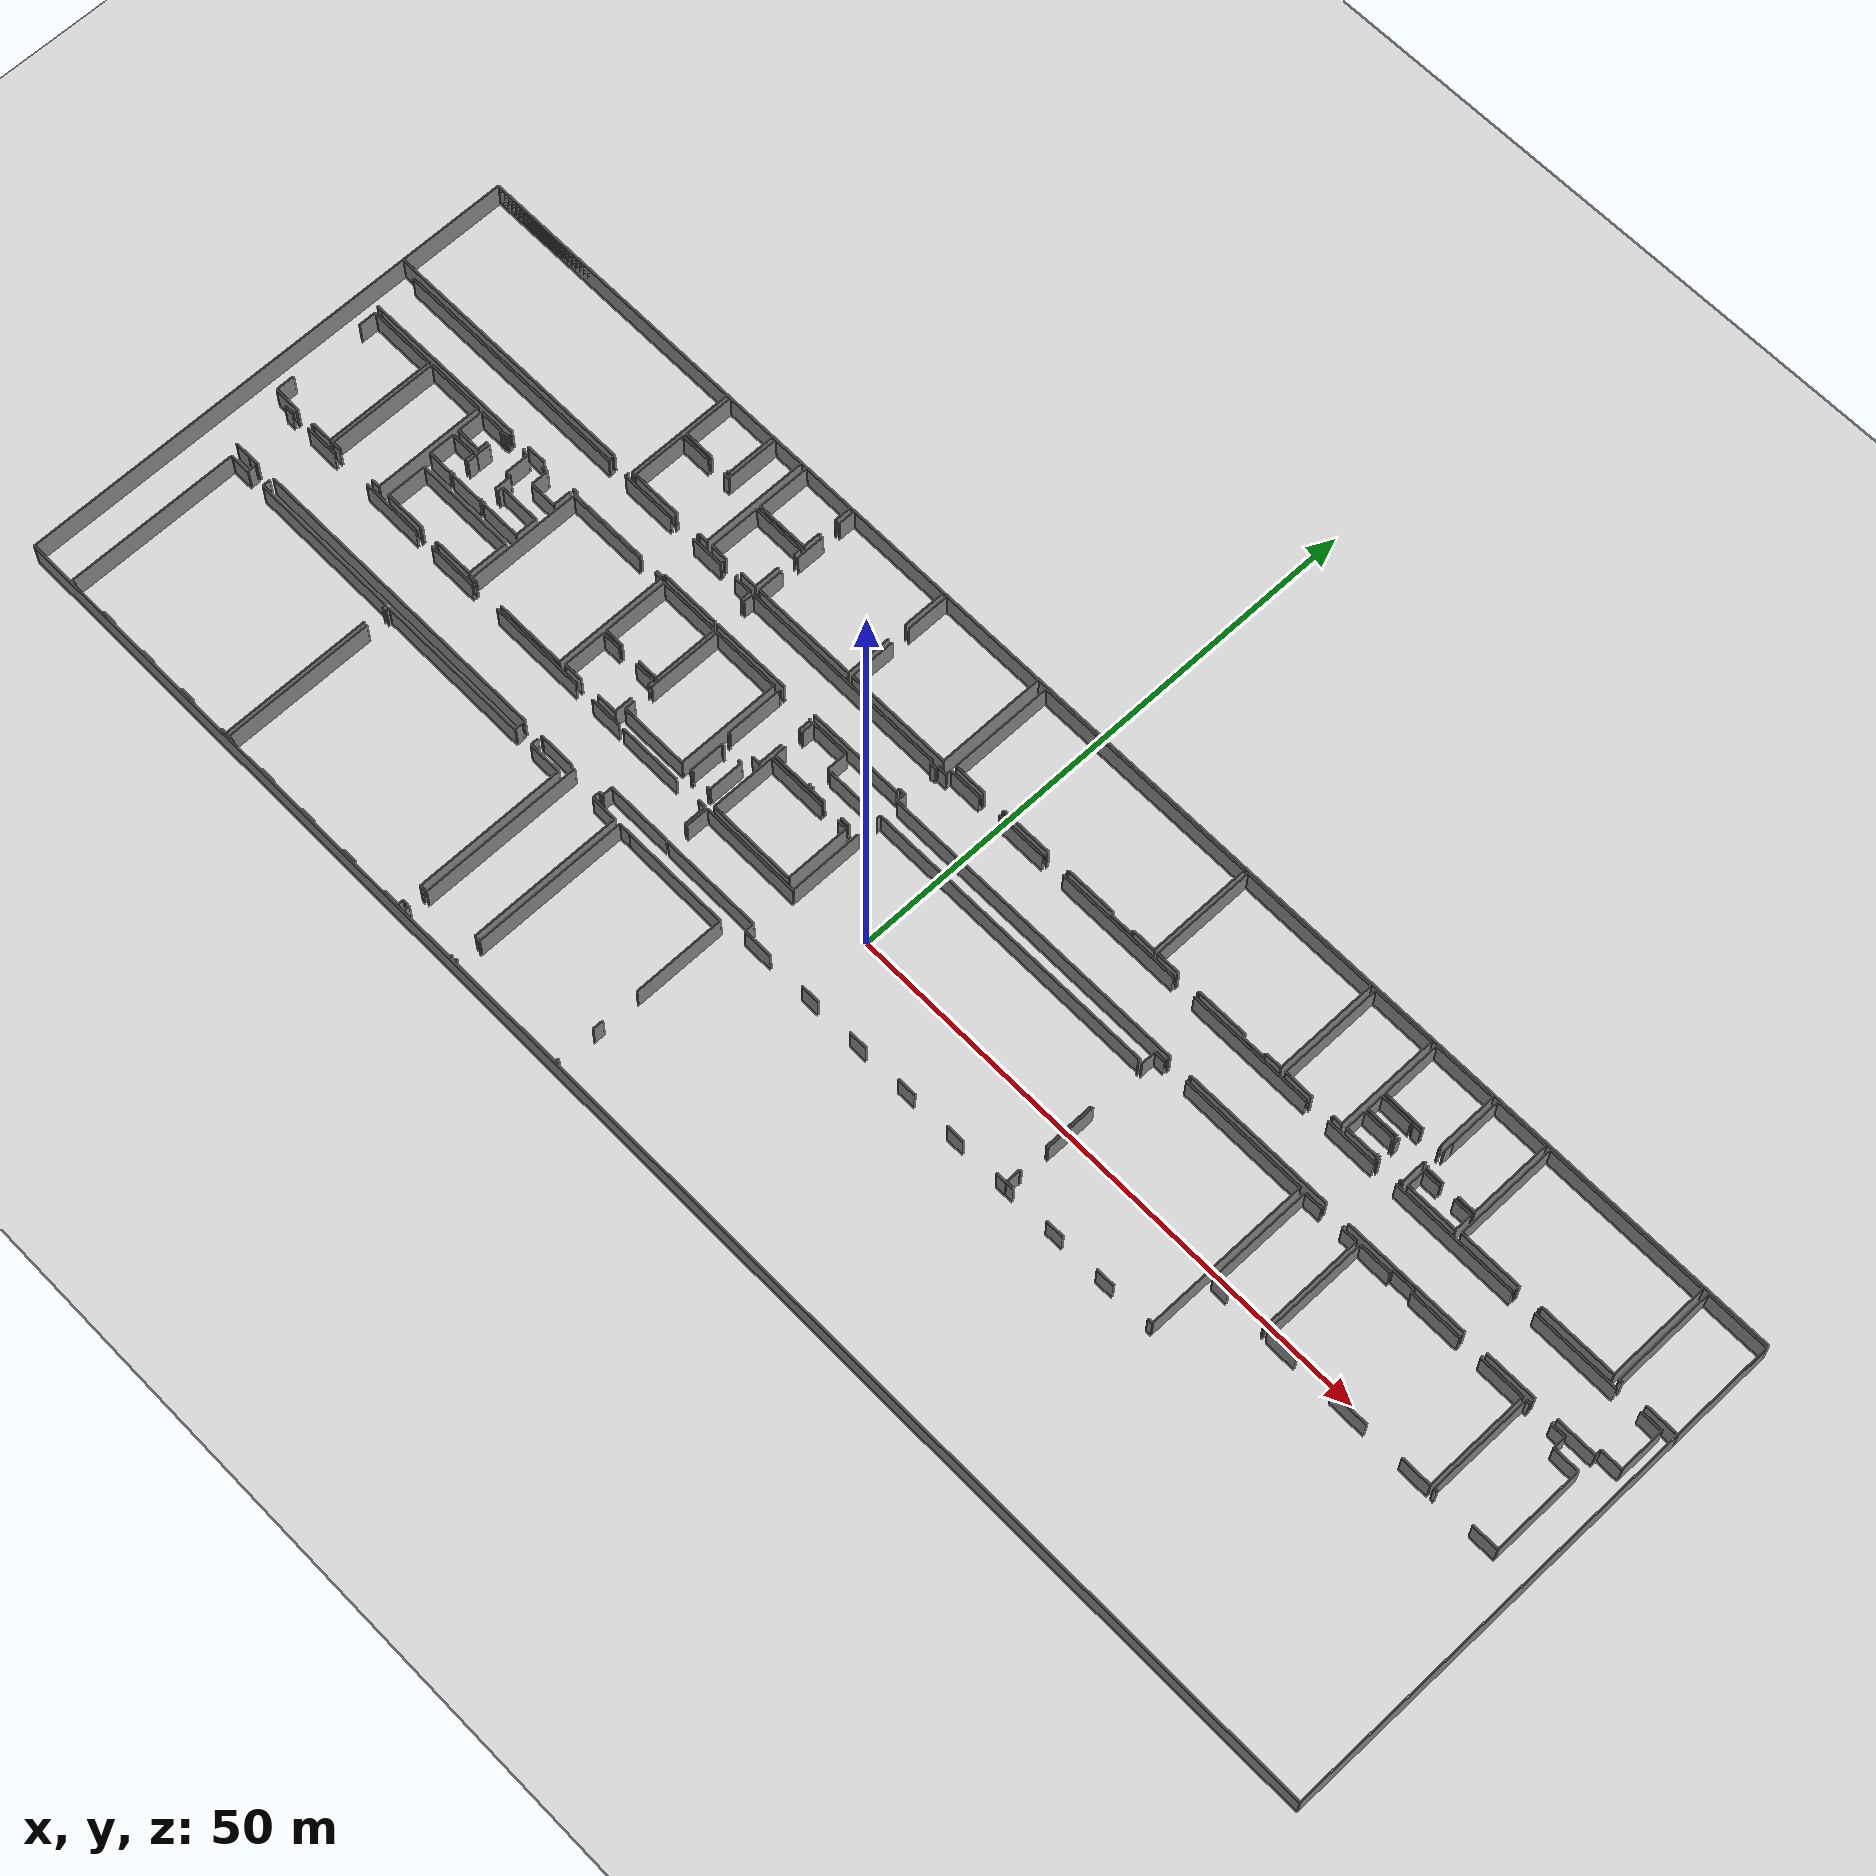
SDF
<sdf version="1.6">
  <world name="default">
    <light name="sun" type="directional">
      <cast_shadows>1</cast_shadows>
      <pose frame="">0 0 10 0 -0 0</pose>
      <diffuse>0.8 0.8 0.8 1</diffuse>
      <specular>0.1 0.1 0.1 1</specular>
      <attenuation>
        <range>1000</range>
        <constant>0.9</constant>
        <linear>0.01</linear>
        <quadratic>0.001</quadratic>
      </attenuation>
      <direction>-0.5 0.5 -1</direction>
    </light>
    <model name="ground_plane">
      <static>1</static>
      <link name="link">
        <collision name="collision">
          <geometry>
            <plane>
              <normal>0 0 1</normal>
              <size>100 100</size>
            </plane>
          </geometry>
          <surface>
            <friction>
              <ode>
                <mu>100</mu>
                <mu2>50</mu2>
              </ode>
              <torsional>
                <ode />
              </torsional>
            </friction>
            <contact>
              <ode />
            </contact>
            <bounce />
          </surface>
          <max_contacts>10</max_contacts>
        </collision>
        <visual name="visual">
          <cast_shadows>0</cast_shadows>
          <geometry>
            <plane>
              <normal>0 0 1</normal>
              <size>100 100</size>
            </plane>
          </geometry>
          <material>
            <script>
              <uri>file://media/materials/scripts/gazebo.material</uri>
              <name>Gazebo/Grey</name>
            </script>
          </material>
        </visual>
        <self_collide>0</self_collide>
        <kinematic>0</kinematic>
        <gravity>1</gravity>
      </link>
    </model>
    <gravity>0 0 -9.8</gravity>
    <magnetic_field>6e-06 2.3e-05 -4.2e-05</magnetic_field>
    <atmosphere type="adiabatic" />
    <physics default="0" name="default_physics" type="ode">
      <max_step_size>0.001</max_step_size>
      <real_time_factor>1</real_time_factor>
      <real_time_update_rate>1000</real_time_update_rate>
    </physics>
    <scene>
      <ambient>0.4 0.4 0.4 1</ambient>
      <background>0.7 0.7 0.7 1</background>
      <shadows>1</shadows>
    </scene>
    <spherical_coordinates>
      <surface_model>EARTH_WGS84</surface_model>
      <latitude_deg>0</latitude_deg>
      <longitude_deg>0</longitude_deg>
      <elevation>0</elevation>
      <heading_deg>0</heading_deg>
    </spherical_coordinates>
  <model name="0510032194_A_40_1_102">
		<static>1</static>
		<link name="Wall_0">
			<collision name="Wall_0_Collision">
				<geometry>
					<box>
						<size>0.49577951795 0.1 2.5</size>
					</box>
				</geometry>
				<pose frame="">0.247889758975 0 1.25 0 0 0</pose>
			</collision>
			<visual name="Wall_0_Visual">
				<pose frame="">0.247889758975 0 1.25 0 0 0</pose>
				<geometry>
					<box>
						<size>0.49577951795 0.1 2.5</size>
					</box>
				</geometry>
				<material>
					<script>
						<uri>file://media/materials/scripts/gazebo.material</uri>
						<name>Gazebo/Grey</name>
					</script>
					<ambient>1 1 1 1</ambient>
				</material>
			</visual>
			<pose frame="">2.34402013628 -14.3805298485 0 0 0 3.14159265359</pose>
		</link>
		<link name="Wall_1">
			<collision name="Wall_1_Collision">
				<geometry>
					<box>
						<size>22.9418793857 0.1 2.5</size>
					</box>
				</geometry>
				<pose frame="">11.4709396929 0 1.25 0 0 0</pose>
			</collision>
			<visual name="Wall_1_Visual">
				<pose frame="">11.4709396929 0 1.25 0 0 0</pose>
				<geometry>
					<box>
						<size>22.9418793857 0.1 2.5</size>
					</box>
				</geometry>
				<material>
					<script>
						<uri>file://media/materials/scripts/gazebo.material</uri>
						<name>Gazebo/Grey</name>
					</script>
					<ambient>1 1 1 1</ambient>
				</material>
			</visual>
			<pose frame="">1.84824061833 -10.6450218651 0 0 0 0.0</pose>
		</link>
		<link name="Wall_2">
			<collision name="Wall_2_Collision">
				<geometry>
					<box>
						<size>0.305095087969 0.1 2.5</size>
					</box>
				</geometry>
				<pose frame="">0.152547543985 0 1.25 0 0 0</pose>
			</collision>
			<visual name="Wall_2_Visual">
				<pose frame="">0.152547543985 0 1.25 0 0 0</pose>
				<geometry>
					<box>
						<size>0.305095087969 0.1 2.5</size>
					</box>
				</geometry>
				<material>
					<script>
						<uri>file://media/materials/scripts/gazebo.material</uri>
						<name>Gazebo/Grey</name>
					</script>
					<ambient>1 1 1 1</ambient>
				</material>
			</visual>
			<pose frame="">24.7901200041 -10.6450218651 0 0 0 1.57079632679</pose>
		</link>
		<link name="Wall_3">
			<collision name="Wall_3_Collision">
				<geometry>
					<box>
						<size>0.296577850097 0.1 2.5</size>
					</box>
				</geometry>
				<pose frame="">0.148288925048 0 1.25 0 0 0</pose>
			</collision>
			<visual name="Wall_3_Visual">
				<pose frame="">0.148288925048 0 1.25 0 0 0</pose>
				<geometry>
					<box>
						<size>0.296577850097 0.1 2.5</size>
					</box>
				</geometry>
				<material>
					<script>
						<uri>file://media/materials/scripts/gazebo.material</uri>
						<name>Gazebo/Grey</name>
					</script>
					<ambient>1 1 1 1</ambient>
				</material>
			</visual>
			<pose frame="">26.7179395912 -10.3399267772 0 0 0 -1.57079632679</pose>
		</link>
		<link name="Wall_4">
			<collision name="Wall_4_Collision">
				<geometry>
					<box>
						<size>5.16246313434 0.1 2.5</size>
					</box>
				</geometry>
				<pose frame="">2.58123156717 0 1.25 0 0 0</pose>
			</collision>
			<visual name="Wall_4_Visual">
				<pose frame="">2.58123156717 0 1.25 0 0 0</pose>
				<geometry>
					<box>
						<size>5.16246313434 0.1 2.5</size>
					</box>
				</geometry>
				<material>
					<script>
						<uri>file://media/materials/scripts/gazebo.material</uri>
						<name>Gazebo/Grey</name>
					</script>
					<ambient>1 1 1 1</ambient>
				</material>
			</visual>
			<pose frame="">26.7179395912 -10.6365046273 0 0 0 0.0</pose>
		</link>
		<link name="Wall_5">
			<collision name="Wall_5_Collision">
				<geometry>
					<box>
						<size>3.06912946202 0.1 2.5</size>
					</box>
				</geometry>
				<pose frame="">1.53456473101 0 1.25 0 0 0</pose>
			</collision>
			<visual name="Wall_5_Visual">
				<pose frame="">1.53456473101 0 1.25 0 0 0</pose>
				<geometry>
					<box>
						<size>3.06912946202 0.1 2.5</size>
					</box>
				</geometry>
				<material>
					<script>
						<uri>file://media/materials/scripts/gazebo.material</uri>
						<name>Gazebo/Grey</name>
					</script>
					<ambient>1 1 1 1</ambient>
				</material>
			</visual>
			<pose frame="">34.4265483576 -10.6365046273 0 0 0 0.0</pose>
		</link>
		<link name="Wall_6">
			<collision name="Wall_6_Collision">
				<geometry>
					<box>
						<size>0.26530560358 0.1 2.5</size>
					</box>
				</geometry>
				<pose frame="">0.13265280179 0 1.25 0 0 0</pose>
			</collision>
			<visual name="Wall_6_Visual">
				<pose frame="">0.13265280179 0 1.25 0 0 0</pose>
				<geometry>
					<box>
						<size>0.26530560358 0.1 2.5</size>
					</box>
				</geometry>
				<material>
					<script>
						<uri>file://media/materials/scripts/gazebo.material</uri>
						<name>Gazebo/Grey</name>
					</script>
					<ambient>1 1 1 1</ambient>
				</material>
			</visual>
			<pose frame="">37.4956778196 -10.6365046273 0 0 0 1.57079632679</pose>
		</link>
		<link name="Wall_7">
			<collision name="Wall_7_Collision">
				<geometry>
					<box>
						<size>0.273822841452 0.1 2.5</size>
					</box>
				</geometry>
				<pose frame="">0.136911420726 0 1.25 0 0 0</pose>
			</collision>
			<visual name="Wall_7_Visual">
				<pose frame="">0.136911420726 0 1.25 0 0 0</pose>
				<geometry>
					<box>
						<size>0.273822841452 0.1 2.5</size>
					</box>
				</geometry>
				<material>
					<script>
						<uri>file://media/materials/scripts/gazebo.material</uri>
						<name>Gazebo/Grey</name>
					</script>
					<ambient>1 1 1 1</ambient>
				</material>
			</visual>
			<pose frame="">39.136580901 -10.3711990237 0 0 0 -1.57079632679</pose>
		</link>
		<link name="Wall_8">
			<collision name="Wall_8_Collision">
				<geometry>
					<box>
						<size>1.70141360724 0.1 2.5</size>
					</box>
				</geometry>
				<pose frame="">0.85070680362 0 1.25 0 0 0</pose>
			</collision>
			<visual name="Wall_8_Visual">
				<pose frame="">0.85070680362 0 1.25 0 0 0</pose>
				<geometry>
					<box>
						<size>1.70141360724 0.1 2.5</size>
					</box>
				</geometry>
				<material>
					<script>
						<uri>file://media/materials/scripts/gazebo.material</uri>
						<name>Gazebo/Grey</name>
					</script>
					<ambient>1 1 1 1</ambient>
				</material>
			</visual>
			<pose frame="">39.136580901 -10.6450218651 0 0 0 0.0</pose>
		</link>
		<link name="Wall_9">
			<collision name="Wall_9_Collision">
				<geometry>
					<box>
						<size>0.956981592596 0.1 2.5</size>
					</box>
				</geometry>
				<pose frame="">0.478490796298 0 1.25 0 0 0</pose>
			</collision>
			<visual name="Wall_9_Visual">
				<pose frame="">0.478490796298 0 1.25 0 0 0</pose>
				<geometry>
					<box>
						<size>0.956981592596 0.1 2.5</size>
					</box>
				</geometry>
				<material>
					<script>
						<uri>file://media/materials/scripts/gazebo.material</uri>
						<name>Gazebo/Grey</name>
					</script>
					<ambient>1 1 1 1</ambient>
				</material>
			</visual>
			<pose frame="">40.8379945083 -10.6450218651 0 0 0 -1.57079632679</pose>
		</link>
		<link name="Wall_10">
			<collision name="Wall_10_Collision">
				<geometry>
					<box>
						<size>0.0672480423065 0.1 2.5</size>
					</box>
				</geometry>
				<pose frame="">0.0336240211533 0 1.25 0 0 0</pose>
			</collision>
			<visual name="Wall_10_Visual">
				<pose frame="">0.0336240211533 0 1.25 0 0 0</pose>
				<geometry>
					<box>
						<size>0.0672480423065 0.1 2.5</size>
					</box>
				</geometry>
				<material>
					<script>
						<uri>file://media/materials/scripts/gazebo.material</uri>
						<name>Gazebo/Grey</name>
					</script>
					<ambient>1 1 1 1</ambient>
				</material>
			</visual>
			<pose frame="">40.8379945083 -14.3127733143 0 0 0 -1.57079632679</pose>
		</link>
		<link name="Wall_11">
			<collision name="Wall_11_Collision">
				<geometry>
					<box>
						<size>5.53099257602 0.1 2.5</size>
					</box>
				</geometry>
				<pose frame="">2.76549628801 0 1.25 0 0 0</pose>
			</collision>
			<visual name="Wall_11_Visual">
				<pose frame="">2.76549628801 0 1.25 0 0 0</pose>
				<geometry>
					<box>
						<size>5.53099257602 0.1 2.5</size>
					</box>
				</geometry>
				<material>
					<script>
						<uri>file://media/materials/scripts/gazebo.material</uri>
						<name>Gazebo/Grey</name>
					</script>
					<ambient>1 1 1 1</ambient>
				</material>
			</visual>
			<pose frame="">40.8379945083 -14.3800213567 0 0 0 3.14159265359</pose>
		</link>
		<link name="Wall_12">
			<collision name="Wall_12_Collision">
				<geometry>
					<box>
						<size>0.224880504424 0.1 2.5</size>
					</box>
				</geometry>
				<pose frame="">0.112440252212 0 1.25 0 0 0</pose>
			</collision>
			<visual name="Wall_12_Visual">
				<pose frame="">0.112440252212 0 1.25 0 0 0</pose>
				<geometry>
					<box>
						<size>0.224880504424 0.1 2.5</size>
					</box>
				</geometry>
				<material>
					<script>
						<uri>file://media/materials/scripts/gazebo.material</uri>
						<name>Gazebo/Grey</name>
					</script>
					<ambient>1 1 1 1</ambient>
				</material>
			</visual>
			<pose frame="">35.3070019323 -14.3800213567 0 0 0 -1.57079632679</pose>
		</link>
		<link name="Wall_13">
			<collision name="Wall_13_Collision">
				<geometry>
					<box>
						<size>0.674260144412 0.1 2.5</size>
					</box>
				</geometry>
				<pose frame="">0.337130072206 0 1.25 0 0 0</pose>
			</collision>
			<visual name="Wall_13_Visual">
				<pose frame="">0.337130072206 0 1.25 0 0 0</pose>
				<geometry>
					<box>
						<size>0.674260144412 0.1 2.5</size>
					</box>
				</geometry>
				<material>
					<script>
						<uri>file://media/materials/scripts/gazebo.material</uri>
						<name>Gazebo/Grey</name>
					</script>
					<ambient>1 1 1 1</ambient>
				</material>
			</visual>
			<pose frame="">35.3070019323 -14.6049018611 0 0 0 3.14159265359</pose>
		</link>
		<link name="Wall_14">
			<collision name="Wall_14_Collision">
				<geometry>
					<box>
						<size>7.59521509204 0.1 2.5</size>
					</box>
				</geometry>
				<pose frame="">3.79760754602 0 1.25 0 0 0</pose>
			</collision>
			<visual name="Wall_14_Visual">
				<pose frame="">3.79760754602 0 1.25 0 0 0</pose>
				<geometry>
					<box>
						<size>7.59521509204 0.1 2.5</size>
					</box>
				</geometry>
				<material>
					<script>
						<uri>file://media/materials/scripts/gazebo.material</uri>
						<name>Gazebo/Grey</name>
					</script>
					<ambient>1 1 1 1</ambient>
				</material>
			</visual>
			<pose frame="">32.859503712 -14.6049018611 0 0 0 3.14159265359</pose>
		</link>
		<link name="Wall_15">
			<collision name="Wall_15_Collision">
				<geometry>
					<box>
						<size>0.237084307943 0.1 2.5</size>
					</box>
				</geometry>
				<pose frame="">0.118542153971 0 1.25 0 0 0</pose>
			</collision>
			<visual name="Wall_15_Visual">
				<pose frame="">0.118542153971 0 1.25 0 0 0</pose>
				<geometry>
					<box>
						<size>0.237084307943 0.1 2.5</size>
					</box>
				</geometry>
				<material>
					<script>
						<uri>file://media/materials/scripts/gazebo.material</uri>
						<name>Gazebo/Grey</name>
					</script>
					<ambient>1 1 1 1</ambient>
				</material>
			</visual>
			<pose frame="">25.26428862 -14.6049018611 0 0 0 1.57079632679</pose>
		</link>
		<link name="Wall_16">
			<collision name="Wall_16_Collision">
				<geometry>
					<box>
						<size>0.444930336622 0.1 2.5</size>
					</box>
				</geometry>
				<pose frame="">0.222465168311 0 1.25 0 0 0</pose>
			</collision>
			<visual name="Wall_16_Visual">
				<pose frame="">0.222465168311 0 1.25 0 0 0</pose>
				<geometry>
					<box>
						<size>0.444930336622 0.1 2.5</size>
					</box>
				</geometry>
				<material>
					<script>
						<uri>file://media/materials/scripts/gazebo.material</uri>
						<name>Gazebo/Grey</name>
					</script>
					<ambient>1 1 1 1</ambient>
				</material>
			</visual>
			<pose frame="">25.26428862 -14.3678175531 0 0 0 3.14159265359</pose>
		</link>
		<link name="Wall_17">
			<collision name="Wall_17_Collision">
				<geometry>
					<box>
						<size>1.86069866775 0.1 2.5</size>
					</box>
				</geometry>
				<pose frame="">0.930349333876 0 1.25 0 0 0</pose>
			</collision>
			<visual name="Wall_17_Visual">
				<pose frame="">0.930349333876 0 1.25 0 0 0</pose>
				<geometry>
					<box>
						<size>1.86069866775 0.1 2.5</size>
					</box>
				</geometry>
				<material>
					<script>
						<uri>file://media/materials/scripts/gazebo.material</uri>
						<name>Gazebo/Grey</name>
					</script>
					<ambient>1 1 1 1</ambient>
				</material>
			</visual>
			<pose frame="">21.4400488152 -14.3678175531 0 0 0 3.14159265359</pose>
		</link>
		<link name="Wall_18">
			<collision name="Wall_18_Collision">
				<geometry>
					<box>
						<size>15.3892557336 0.1 2.5</size>
					</box>
				</geometry>
				<pose frame="">7.69462786678 0 1.25 0 0 0</pose>
			</collision>
			<visual name="Wall_18_Visual">
				<pose frame="">7.69462786678 0 1.25 0 0 0</pose>
				<geometry>
					<box>
						<size>15.3892557336 0.1 2.5</size>
					</box>
				</geometry>
				<material>
					<script>
						<uri>file://media/materials/scripts/gazebo.material</uri>
						<name>Gazebo/Grey</name>
					</script>
					<ambient>1 1 1 1</ambient>
				</material>
			</visual>
			<pose frame="">17.7332706193 -14.3678175531 0 0 0 -3.14076660345</pose>
		</link>
		<link name="Wall_19">
			<collision name="Wall_19_Collision">
				<geometry>
					<box>
						<size>10.0616546324 0.1 2.5</size>
					</box>
				</geometry>
				<pose frame="">5.03082731618 0 1.25 0 0 0</pose>
			</collision>
			<visual name="Wall_19_Visual">
				<pose frame="">5.03082731618 0 1.25 0 0 0</pose>
				<geometry>
					<box>
						<size>10.0616546324 0.1 2.5</size>
					</box>
				</geometry>
				<material>
					<script>
						<uri>file://media/materials/scripts/gazebo.material</uri>
						<name>Gazebo/Grey</name>
					</script>
					<ambient>1 1 1 1</ambient>
				</material>
			</visual>
			<pose frame="">0.0 -10.0616546324 0 0 0 1.57079632679</pose>
		</link>
		<link name="Wall_20">
			<collision name="Wall_20_Collision">
				<geometry>
					<box>
						<size>26.8495118479 0.1 2.5</size>
					</box>
				</geometry>
				<pose frame="">13.4247559239 0 1.25 0 0 0</pose>
			</collision>
			<visual name="Wall_20_Visual">
				<pose frame="">13.4247559239 0 1.25 0 0 0</pose>
				<geometry>
					<box>
						<size>26.8495118479 0.1 2.5</size>
					</box>
				</geometry>
				<material>
					<script>
						<uri>file://media/materials/scripts/gazebo.material</uri>
						<name>Gazebo/Grey</name>
					</script>
					<ambient>1 1 1 1</ambient>
				</material>
			</visual>
			<pose frame="">0.0 -0.0 0 0 0 0.0</pose>
		</link>
		<link name="Wall_21">
			<collision name="Wall_21_Collision">
				<geometry>
					<box>
						<size>10.0469083698 0.1 2.5</size>
					</box>
				</geometry>
				<pose frame="">5.02345418489 0 1.25 0 0 0</pose>
			</collision>
			<visual name="Wall_21_Visual">
				<pose frame="">5.02345418489 0 1.25 0 0 0</pose>
				<geometry>
					<box>
						<size>10.0469083698 0.1 2.5</size>
					</box>
				</geometry>
				<material>
					<script>
						<uri>file://media/materials/scripts/gazebo.material</uri>
						<name>Gazebo/Grey</name>
					</script>
					<ambient>1 1 1 1</ambient>
				</material>
			</visual>
			<pose frame="">26.8495118479 -0.0 0 0 0 -1.57079632679</pose>
		</link>
		<link name="Wall_22">
			<collision name="Wall_22_Collision">
				<geometry>
					<box>
						<size>0.0683921488864 0.1 2.5</size>
					</box>
				</geometry>
				<pose frame="">0.0341960744432 0 1.25 0 0 0</pose>
			</collision>
			<visual name="Wall_22_Visual">
				<pose frame="">0.0341960744432 0 1.25 0 0 0</pose>
				<geometry>
					<box>
						<size>0.0683921488864 0.1 2.5</size>
					</box>
				</geometry>
				<material>
					<script>
						<uri>file://media/materials/scripts/gazebo.material</uri>
						<name>Gazebo/Grey</name>
					</script>
					<ambient>1 1 1 1</ambient>
				</material>
			</visual>
			<pose frame="">26.8495118479 -10.0469083698 0 0 0 3.14159265359</pose>
		</link>
		<link name="Wall_23">
			<collision name="Wall_23_Collision">
				<geometry>
					<box>
						<size>24.7980060116 0.1 2.5</size>
					</box>
				</geometry>
				<pose frame="">12.3990030058 0 1.25 0 0 0</pose>
			</collision>
			<visual name="Wall_23_Visual">
				<pose frame="">12.3990030058 0 1.25 0 0 0</pose>
				<geometry>
					<box>
						<size>24.7980060116 0.1 2.5</size>
					</box>
				</geometry>
				<material>
					<script>
						<uri>file://media/materials/scripts/gazebo.material</uri>
						<name>Gazebo/Grey</name>
					</script>
					<ambient>1 1 1 1</ambient>
				</material>
			</visual>
			<pose frame="">24.7980016272 -10.0469083698 0 0 0 -3.14099799838</pose>
		</link>
		<link name="Wall_24">
			<collision name="Wall_24_Collision">
				<geometry>
					<box>
						<size>4.68295535442 0.1 2.5</size>
					</box>
				</geometry>
				<pose frame="">2.34147767721 0 1.25 0 0 0</pose>
			</collision>
			<visual name="Wall_24_Visual">
				<pose frame="">2.34147767721 0 1.25 0 0 0</pose>
				<geometry>
					<box>
						<size>4.68295535442 0.1 2.5</size>
					</box>
				</geometry>
				<material>
					<script>
						<uri>file://media/materials/scripts/gazebo.material</uri>
						<name>Gazebo/Grey</name>
					</script>
					<ambient>1 1 1 1</ambient>
				</material>
			</visual>
			<pose frame="">27.19223533 -4.68537069053 0 0 0 1.57079632679</pose>
		</link>
		<link name="Wall_25">
			<collision name="Wall_25_Collision">
				<geometry>
					<box>
						<size>4.85228312824 0.1 2.5</size>
					</box>
				</geometry>
				<pose frame="">2.42614156412 0 1.25 0 0 0</pose>
			</collision>
			<visual name="Wall_25_Visual">
				<pose frame="">2.42614156412 0 1.25 0 0 0</pose>
				<geometry>
					<box>
						<size>4.85228312824 0.1 2.5</size>
					</box>
				</geometry>
				<material>
					<script>
						<uri>file://media/materials/scripts/gazebo.material</uri>
						<name>Gazebo/Grey</name>
					</script>
					<ambient>1 1 1 1</ambient>
				</material>
			</visual>
			<pose frame="">27.19223533 -0.00241533611309 0 0 0 0.0</pose>
		</link>
		<link name="Wall_26">
			<collision name="Wall_26_Collision">
				<geometry>
					<box>
						<size>4.68511644463 0.1 2.5</size>
					</box>
				</geometry>
				<pose frame="">2.34255822231 0 1.25 0 0 0</pose>
			</collision>
			<visual name="Wall_26_Visual">
				<pose frame="">2.34255822231 0 1.25 0 0 0</pose>
				<geometry>
					<box>
						<size>4.68511644463 0.1 2.5</size>
					</box>
				</geometry>
				<material>
					<script>
						<uri>file://media/materials/scripts/gazebo.material</uri>
						<name>Gazebo/Grey</name>
					</script>
					<ambient>1 1 1 1</ambient>
				</material>
			</visual>
			<pose frame="">32.0445184583 -0.00241533611309 0 0 0 -1.57079632679</pose>
		</link>
		<link name="Wall_27">
			<collision name="Wall_27_Collision">
				<geometry>
					<box>
						<size>0.218015864945 0.1 2.5</size>
					</box>
				</geometry>
				<pose frame="">0.109007932472 0 1.25 0 0 0</pose>
			</collision>
			<visual name="Wall_27_Visual">
				<pose frame="">0.109007932472 0 1.25 0 0 0</pose>
				<geometry>
					<box>
						<size>0.218015864945 0.1 2.5</size>
					</box>
				</geometry>
				<material>
					<script>
						<uri>file://media/materials/scripts/gazebo.material</uri>
						<name>Gazebo/Grey</name>
					</script>
					<ambient>1 1 1 1</ambient>
				</material>
			</visual>
			<pose frame="">32.0445184583 -4.68753178074 0 0 0 3.14159265359</pose>
		</link>
		<link name="Wall_28">
			<collision name="Wall_28_Collision">
				<geometry>
					<box>
						<size>2.89204799548 0.1 2.5</size>
					</box>
				</geometry>
				<pose frame="">1.44602399774 0 1.25 0 0 0</pose>
			</collision>
			<visual name="Wall_28_Visual">
				<pose frame="">1.44602399774 0 1.25 0 0 0</pose>
				<geometry>
					<box>
						<size>2.89204799548 0.1 2.5</size>
					</box>
				</geometry>
				<material>
					<script>
						<uri>file://media/materials/scripts/gazebo.material</uri>
						<name>Gazebo/Grey</name>
					</script>
					<ambient>1 1 1 1</ambient>
				</material>
			</visual>
			<pose frame="">30.0842825181 -4.68753178074 0 0 0 3.14084540098</pose>
		</link>
		<link name="Wall_29">
			<collision name="Wall_29_Collision">
				<geometry>
					<box>
						<size>5.02046679548 0.1 2.5</size>
					</box>
				</geometry>
				<pose frame="">2.51023339774 0 1.25 0 0 0</pose>
			</collision>
			<visual name="Wall_29_Visual">
				<pose frame="">2.51023339774 0 1.25 0 0 0</pose>
				<geometry>
					<box>
						<size>5.02046679548 0.1 2.5</size>
					</box>
				</geometry>
				<material>
					<script>
						<uri>file://media/materials/scripts/gazebo.material</uri>
						<name>Gazebo/Grey</name>
					</script>
					<ambient>1 1 1 1</ambient>
				</material>
			</visual>
			<pose frame="">27.1711329198 -10.0284755415 0 0 0 1.57079632679</pose>
		</link>
		<link name="Wall_30">
			<collision name="Wall_30_Collision">
				<geometry>
					<box>
						<size>2.89141157327 0.1 2.5</size>
					</box>
				</geometry>
				<pose frame="">1.44570578664 0 1.25 0 0 0</pose>
			</collision>
			<visual name="Wall_30_Visual">
				<pose frame="">1.44570578664 0 1.25 0 0 0</pose>
				<geometry>
					<box>
						<size>2.89141157327 0.1 2.5</size>
					</box>
				</geometry>
				<material>
					<script>
						<uri>file://media/materials/scripts/gazebo.material</uri>
						<name>Gazebo/Grey</name>
					</script>
					<ambient>1 1 1 1</ambient>
				</material>
			</visual>
			<pose frame="">27.1711329198 -5.00800874606 0 0 0 0.0</pose>
		</link>
		<link name="Wall_31">
			<collision name="Wall_31_Collision">
				<geometry>
					<box>
						<size>0.566078511136 0.1 2.5</size>
					</box>
				</geometry>
				<pose frame="">0.283039255568 0 1.25 0 0 0</pose>
			</collision>
			<visual name="Wall_31_Visual">
				<pose frame="">0.283039255568 0 1.25 0 0 0</pose>
				<geometry>
					<box>
						<size>0.566078511136 0.1 2.5</size>
					</box>
				</geometry>
				<material>
					<script>
						<uri>file://media/materials/scripts/gazebo.material</uri>
						<name>Gazebo/Grey</name>
					</script>
					<ambient>1 1 1 1</ambient>
				</material>
			</visual>
			<pose frame="">31.8153157734 -5.00800874606 0 0 0 0.0</pose>
		</link>
		<link name="Wall_32">
			<collision name="Wall_32_Collision">
				<geometry>
					<box>
						<size>4.98550798332 0.1 2.5</size>
					</box>
				</geometry>
				<pose frame="">2.49275399166 0 1.25 0 0 0</pose>
			</collision>
			<visual name="Wall_32_Visual">
				<pose frame="">2.49275399166 0 1.25 0 0 0</pose>
				<geometry>
					<box>
						<size>4.98550798332 0.1 2.5</size>
					</box>
				</geometry>
				<material>
					<script>
						<uri>file://media/materials/scripts/gazebo.material</uri>
						<name>Gazebo/Grey</name>
					</script>
					<ambient>1 1 1 1</ambient>
				</material>
			</visual>
			<pose frame="">32.3813942846 -5.00800874606 0 0 0 1.57079632679</pose>
		</link>
		<link name="Wall_33">
			<collision name="Wall_33_Collision">
				<geometry>
					<box>
						<size>2.93526899217 0.1 2.5</size>
					</box>
				</geometry>
				<pose frame="">1.46763449608 0 1.25 0 0 0</pose>
			</collision>
			<visual name="Wall_33_Visual">
				<pose frame="">1.46763449608 0 1.25 0 0 0</pose>
				<geometry>
					<box>
						<size>2.93526899217 0.1 2.5</size>
					</box>
				</geometry>
				<material>
					<script>
						<uri>file://media/materials/scripts/gazebo.material</uri>
						<name>Gazebo/Grey</name>
					</script>
					<ambient>1 1 1 1</ambient>
				</material>
			</visual>
			<pose frame="">32.3813942846 -0.0225007627377 0 0 0 0.0</pose>
		</link>
		<link name="Wall_34">
			<collision name="Wall_34_Collision">
				<geometry>
					<box>
						<size>10.0123309265 0.1 2.5</size>
					</box>
				</geometry>
				<pose frame="">5.00616546324 0 1.25 0 0 0</pose>
			</collision>
			<visual name="Wall_34_Visual">
				<pose frame="">5.00616546324 0 1.25 0 0 0</pose>
				<geometry>
					<box>
						<size>10.0123309265 0.1 2.5</size>
					</box>
				</geometry>
				<material>
					<script>
						<uri>file://media/materials/scripts/gazebo.material</uri>
						<name>Gazebo/Grey</name>
					</script>
					<ambient>1 1 1 1</ambient>
				</material>
			</visual>
			<pose frame="">35.3166632767 -0.0225007627377 0 0 0 -1.57079632679</pose>
		</link>
		<link name="Wall_35">
			<collision name="Wall_35_Collision">
				<geometry>
					<box>
						<size>0.88591986169 0.1 2.5</size>
					</box>
				</geometry>
				<pose frame="">0.442959930845 0 1.25 0 0 0</pose>
			</collision>
			<visual name="Wall_35_Visual">
				<pose frame="">0.442959930845 0 1.25 0 0 0</pose>
				<geometry>
					<box>
						<size>0.88591986169 0.1 2.5</size>
					</box>
				</geometry>
				<material>
					<script>
						<uri>file://media/materials/scripts/gazebo.material</uri>
						<name>Gazebo/Grey</name>
					</script>
					<ambient>1 1 1 1</ambient>
				</material>
			</visual>
			<pose frame="">35.3166632767 -10.0348316892 0 0 0 3.14159265359</pose>
		</link>
		<link name="Wall_36">
			<collision name="Wall_36_Collision">
				<geometry>
					<box>
						<size>0.242423471982 0.1 2.5</size>
					</box>
				</geometry>
				<pose frame="">0.121211735991 0 1.25 0 0 0</pose>
			</collision>
			<visual name="Wall_36_Visual">
				<pose frame="">0.121211735991 0 1.25 0 0 0</pose>
				<geometry>
					<box>
						<size>0.242423471982 0.1 2.5</size>
					</box>
				</geometry>
				<material>
					<script>
						<uri>file://media/materials/scripts/gazebo.material</uri>
						<name>Gazebo/Grey</name>
					</script>
					<ambient>1 1 1 1</ambient>
				</material>
			</visual>
			<pose frame="">34.430743415 -10.0348316892 0 0 0 -1.57079632679</pose>
		</link>
		<link name="Wall_37">
			<collision name="Wall_37_Collision">
				<geometry>
					<box>
						<size>0.242042103122 0.1 2.5</size>
					</box>
				</geometry>
				<pose frame="">0.121021051561 0 1.25 0 0 0</pose>
			</collision>
			<visual name="Wall_37_Visual">
				<pose frame="">0.121021051561 0 1.25 0 0 0</pose>
				<geometry>
					<box>
						<size>0.242042103122 0.1 2.5</size>
					</box>
				</geometry>
				<material>
					<script>
						<uri>file://media/materials/scripts/gazebo.material</uri>
						<name>Gazebo/Grey</name>
					</script>
					<ambient>1 1 1 1</ambient>
				</material>
			</visual>
			<pose frame="">31.9369724397 -10.2772551612 0 0 0 1.57079632679</pose>
		</link>
		<link name="Wall_38">
			<collision name="Wall_38_Collision">
				<geometry>
					<box>
						<size>4.76584428243 0.1 2.5</size>
					</box>
				</geometry>
				<pose frame="">2.38292214121 0 1.25 0 0 0</pose>
			</collision>
			<visual name="Wall_38_Visual">
				<pose frame="">2.38292214121 0 1.25 0 0 0</pose>
				<geometry>
					<box>
						<size>4.76584428243 0.1 2.5</size>
					</box>
				</geometry>
				<material>
					<script>
						<uri>file://media/materials/scripts/gazebo.material</uri>
						<name>Gazebo/Grey</name>
					</script>
					<ambient>1 1 1 1</ambient>
				</material>
			</visual>
			<pose frame="">31.9369724397 -10.0352130581 0 0 0 3.14017894421</pose>
		</link>
		<link name="Wall_39">
			<collision name="Wall_39_Collision">
				<geometry>
					<box>
						<size>4.69846435472 0.1 2.5</size>
					</box>
				</geometry>
				<pose frame="">2.34923217736 0 1.25 0 0 0</pose>
			</collision>
			<visual name="Wall_39_Visual">
				<pose frame="">2.34923217736 0 1.25 0 0 0</pose>
				<geometry>
					<box>
						<size>4.69846435472 0.1 2.5</size>
					</box>
				</geometry>
				<material>
					<script>
						<uri>file://media/materials/scripts/gazebo.material</uri>
						<name>Gazebo/Grey</name>
					</script>
					<ambient>1 1 1 1</ambient>
				</material>
			</visual>
			<pose frame="">35.9028272145 -10.019068443 0 0 0 1.57079632679</pose>
		</link>
		<link name="Wall_40">
			<collision name="Wall_40_Collision">
				<geometry>
					<box>
						<size>4.8869876945 0.1 2.5</size>
					</box>
				</geometry>
				<pose frame="">2.44349384725 0 1.25 0 0 0</pose>
			</collision>
			<visual name="Wall_40_Visual">
				<pose frame="">2.44349384725 0 1.25 0 0 0</pose>
				<geometry>
					<box>
						<size>4.8869876945 0.1 2.5</size>
					</box>
				</geometry>
				<material>
					<script>
						<uri>file://media/materials/scripts/gazebo.material</uri>
						<name>Gazebo/Grey</name>
					</script>
					<ambient>1 1 1 1</ambient>
				</material>
			</visual>
			<pose frame="">35.9028272145 -5.32060408827 0 0 0 0.0</pose>
		</link>
		<link name="Wall_41">
			<collision name="Wall_41_Collision">
				<geometry>
					<box>
						<size>0.69523543171 0.1 2.5</size>
					</box>
				</geometry>
				<pose frame="">0.347617715855 0 1.25 0 0 0</pose>
			</collision>
			<visual name="Wall_41_Visual">
				<pose frame="">0.347617715855 0 1.25 0 0 0</pose>
				<geometry>
					<box>
						<size>0.69523543171 0.1 2.5</size>
					</box>
				</geometry>
				<material>
					<script>
						<uri>file://media/materials/scripts/gazebo.material</uri>
						<name>Gazebo/Grey</name>
					</script>
					<ambient>1 1 1 1</ambient>
				</material>
			</visual>
			<pose frame="">40.789814909 -5.32060408827 0 0 0 -1.57079632679</pose>
		</link>
		<link name="Wall_42">
			<collision name="Wall_42_Collision">
				<geometry>
					<box>
						<size>2.37427539917 0.1 2.5</size>
					</box>
				</geometry>
				<pose frame="">1.18713769958 0 1.25 0 0 0</pose>
			</collision>
			<visual name="Wall_42_Visual">
				<pose frame="">1.18713769958 0 1.25 0 0 0</pose>
				<geometry>
					<box>
						<size>2.37427539917 0.1 2.5</size>
					</box>
				</geometry>
				<material>
					<script>
						<uri>file://media/materials/scripts/gazebo.material</uri>
						<name>Gazebo/Grey</name>
					</script>
					<ambient>1 1 1 1</ambient>
				</material>
			</visual>
			<pose frame="">40.789814909 -7.6609376589 0 0 0 -1.57079632679</pose>
		</link>
		<link name="Wall_43">
			<collision name="Wall_43_Collision">
				<geometry>
					<box>
						<size>1.59564731008 0.1 2.5</size>
					</box>
				</geometry>
				<pose frame="">0.797823655039 0 1.25 0 0 0</pose>
			</collision>
			<visual name="Wall_43_Visual">
				<pose frame="">0.797823655039 0 1.25 0 0 0</pose>
				<geometry>
					<box>
						<size>1.59564731008 0.1 2.5</size>
					</box>
				</geometry>
				<material>
					<script>
						<uri>file://media/materials/scripts/gazebo.material</uri>
						<name>Gazebo/Grey</name>
					</script>
					<ambient>1 1 1 1</ambient>
				</material>
			</visual>
			<pose frame="">40.789814909 -10.0352130581 0 0 0 3.14159265359</pose>
		</link>
		<link name="Wall_44">
			<collision name="Wall_44_Collision">
				<geometry>
					<box>
						<size>1.56128046466 0.1 2.5</size>
					</box>
				</geometry>
				<pose frame="">0.780640232331 0 1.25 0 0 0</pose>
			</collision>
			<visual name="Wall_44_Visual">
				<pose frame="">0.780640232331 0 1.25 0 0 0</pose>
				<geometry>
					<box>
						<size>1.56128046466 0.1 2.5</size>
					</box>
				</geometry>
				<material>
					<script>
						<uri>file://media/materials/scripts/gazebo.material</uri>
						<name>Gazebo/Grey</name>
					</script>
					<ambient>1 1 1 1</ambient>
				</material>
			</visual>
			<pose frame="">37.4640242042 -10.0352130581 0 0 0 3.13125184477</pose>
		</link>
		<link name="Wall_45">
			<collision name="Wall_45_Collision">
				<geometry>
					<box>
						<size>1.33059595241 0.1 2.5</size>
					</box>
				</geometry>
				<pose frame="">0.665297976203 0 1.25 0 0 0</pose>
			</collision>
			<visual name="Wall_45_Visual">
				<pose frame="">0.665297976203 0 1.25 0 0 0</pose>
				<geometry>
					<box>
						<size>1.33059595241 0.1 2.5</size>
					</box>
				</geometry>
				<material>
					<script>
						<uri>file://media/materials/scripts/gazebo.material</uri>
						<name>Gazebo/Grey</name>
					</script>
					<ambient>1 1 1 1</ambient>
				</material>
			</visual>
			<pose frame="">17.3843181125 -17.7705176447 0 0 0 1.57079632679</pose>
		</link>
		<link name="Wall_46">
			<collision name="Wall_46_Collision">
				<geometry>
					<box>
						<size>0.152674666938 0.1 2.5</size>
					</box>
				</geometry>
				<pose frame="">0.0763373334689 0 1.25 0 0 0</pose>
			</collision>
			<visual name="Wall_46_Visual">
				<pose frame="">0.0763373334689 0 1.25 0 0 0</pose>
				<geometry>
					<box>
						<size>0.152674666938 0.1 2.5</size>
					</box>
				</geometry>
				<material>
					<script>
						<uri>file://media/materials/scripts/gazebo.material</uri>
						<name>Gazebo/Grey</name>
					</script>
					<ambient>1 1 1 1</ambient>
				</material>
			</visual>
			<pose frame="">17.3843181125 -15.0448744025 0 0 0 1.57079632679</pose>
		</link>
		<link name="Wall_47">
			<collision name="Wall_47_Collision">
				<geometry>
					<box>
						<size>0.363444523543 0.1 2.5</size>
					</box>
				</geometry>
				<pose frame="">0.181722261772 0 1.25 0 0 0</pose>
			</collision>
			<visual name="Wall_47_Visual">
				<pose frame="">0.181722261772 0 1.25 0 0 0</pose>
				<geometry>
					<box>
						<size>0.363444523543 0.1 2.5</size>
					</box>
				</geometry>
				<material>
					<script>
						<uri>file://media/materials/scripts/gazebo.material</uri>
						<name>Gazebo/Grey</name>
					</script>
					<ambient>1 1 1 1</ambient>
				</material>
			</visual>
			<pose frame="">17.3843181125 -14.8921997356 0 0 0 0.0</pose>
		</link>
		<link name="Wall_48">
			<collision name="Wall_48_Collision">
				<geometry>
					<box>
						<size>0.196277839927 0.1 2.5</size>
					</box>
				</geometry>
				<pose frame="">0.0981389199634 0 1.25 0 0 0</pose>
			</collision>
			<visual name="Wall_48_Visual">
				<pose frame="">0.0981389199634 0 1.25 0 0 0</pose>
				<geometry>
					<box>
						<size>0.196277839927 0.1 2.5</size>
					</box>
				</geometry>
				<material>
					<script>
						<uri>file://media/materials/scripts/gazebo.material</uri>
						<name>Gazebo/Grey</name>
					</script>
					<ambient>1 1 1 1</ambient>
				</material>
			</visual>
			<pose frame="">17.747762636 -14.8921997356 0 0 0 1.57079632679</pose>
		</link>
		<link name="Wall_49">
			<collision name="Wall_49_Collision">
				<geometry>
					<box>
						<size>0.181912946202 0.1 2.5</size>
					</box>
				</geometry>
				<pose frame="">0.0909564731008 0 1.25 0 0 0</pose>
			</collision>
			<visual name="Wall_49_Visual">
				<pose frame="">0.0909564731008 0 1.25 0 0 0</pose>
				<geometry>
					<box>
						<size>0.181912946202 0.1 2.5</size>
					</box>
				</geometry>
				<material>
					<script>
						<uri>file://media/materials/scripts/gazebo.material</uri>
						<name>Gazebo/Grey</name>
					</script>
					<ambient>1 1 1 1</ambient>
				</material>
			</visual>
			<pose frame="">19.5320604088 -14.6959218957 0 0 0 -1.57079632679</pose>
		</link>
		<link name="Wall_50">
			<collision name="Wall_50_Collision">
				<geometry>
					<box>
						<size>0.610571544798 0.1 2.5</size>
					</box>
				</geometry>
				<pose frame="">0.305285772399 0 1.25 0 0 0</pose>
			</collision>
			<visual name="Wall_50_Visual">
				<pose frame="">0.305285772399 0 1.25 0 0 0</pose>
				<geometry>
					<box>
						<size>0.610571544798 0.1 2.5</size>
					</box>
				</geometry>
				<material>
					<script>
						<uri>file://media/materials/scripts/gazebo.material</uri>
						<name>Gazebo/Grey</name>
					</script>
					<ambient>1 1 1 1</ambient>
				</material>
			</visual>
			<pose frame="">19.5320604088 -14.8778348419 0 0 0 0.0</pose>
		</link>
		<link name="Wall_51">
			<collision name="Wall_51_Collision">
				<geometry>
					<box>
						<size>2.29660327469 0.1 2.5</size>
					</box>
				</geometry>
				<pose frame="">1.14830163734 0 1.25 0 0 0</pose>
			</collision>
			<visual name="Wall_51_Visual">
				<pose frame="">1.14830163734 0 1.25 0 0 0</pose>
				<geometry>
					<box>
						<size>2.29660327469 0.1 2.5</size>
					</box>
				</geometry>
				<material>
					<script>
						<uri>file://media/materials/scripts/gazebo.material</uri>
						<name>Gazebo/Grey</name>
					</script>
					<ambient>1 1 1 1</ambient>
				</material>
			</visual>
			<pose frame="">20.1426319536 -14.8778348419 0 0 0 -1.57079632679</pose>
		</link>
		<link name="Wall_52">
			<collision name="Wall_52_Collision">
				<geometry>
					<box>
						<size>0.483448591478 0.1 2.5</size>
					</box>
				</geometry>
				<pose frame="">0.241724295739 0 1.25 0 0 0</pose>
			</collision>
			<visual name="Wall_52_Visual">
				<pose frame="">0.241724295739 0 1.25 0 0 0</pose>
				<geometry>
					<box>
						<size>0.483448591478 0.1 2.5</size>
					</box>
				</geometry>
				<material>
					<script>
						<uri>file://media/materials/scripts/gazebo.material</uri>
						<name>Gazebo/Grey</name>
					</script>
					<ambient>1 1 1 1</ambient>
				</material>
			</visual>
			<pose frame="">20.1426319536 -17.1744381165 0 0 0 0.0</pose>
		</link>
		<link name="Wall_53">
			<collision name="Wall_53_Collision">
				<geometry>
					<box>
						<size>1.51301739042 0.1 2.5</size>
					</box>
				</geometry>
				<pose frame="">0.75650869521 0 1.25 0 0 0</pose>
			</collision>
			<visual name="Wall_53_Visual">
				<pose frame="">0.75650869521 0 1.25 0 0 0</pose>
				<geometry>
					<box>
						<size>1.51301739042 0.1 2.5</size>
					</box>
				</geometry>
				<material>
					<script>
						<uri>file://media/materials/scripts/gazebo.material</uri>
						<name>Gazebo/Grey</name>
					</script>
					<ambient>1 1 1 1</ambient>
				</material>
			</visual>
			<pose frame="">20.6260805451 -17.1744381165 0 0 0 -1.57079632679</pose>
		</link>
		<link name="Wall_54">
			<collision name="Wall_54_Collision">
				<geometry>
					<box>
						<size>0.159920675277 0.1 2.5</size>
					</box>
				</geometry>
				<pose frame="">0.0799603376386 0 1.25 0 0 0</pose>
			</collision>
			<visual name="Wall_54_Visual">
				<pose frame="">0.0799603376386 0 1.25 0 0 0</pose>
				<geometry>
					<box>
						<size>0.159920675277 0.1 2.5</size>
					</box>
				</geometry>
				<material>
					<script>
						<uri>file://media/materials/scripts/gazebo.material</uri>
						<name>Gazebo/Grey</name>
					</script>
					<ambient>1 1 1 1</ambient>
				</material>
			</visual>
			<pose frame="">20.6260805451 -20.1108512153 0 0 0 -1.57079632679</pose>
		</link>
		<link name="Wall_55">
			<collision name="Wall_55_Collision">
				<geometry>
					<box>
						<size>3.21964303875 0.1 2.5</size>
					</box>
				</geometry>
				<pose frame="">1.60982151937 0 1.25 0 0 0</pose>
			</collision>
			<visual name="Wall_55_Visual">
				<pose frame="">1.60982151937 0 1.25 0 0 0</pose>
				<geometry>
					<box>
						<size>3.21964303875 0.1 2.5</size>
					</box>
				</geometry>
				<material>
					<script>
						<uri>file://media/materials/scripts/gazebo.material</uri>
						<name>Gazebo/Grey</name>
					</script>
					<ambient>1 1 1 1</ambient>
				</material>
			</visual>
			<pose frame="">20.6260805451 -20.2707718906 0 0 0 3.14159265359</pose>
		</link>
		<link name="Wall_56">
			<collision name="Wall_56_Collision">
				<geometry>
					<box>
						<size>0.171234618123 0.1 2.5</size>
					</box>
				</geometry>
				<pose frame="">0.0856173090613 0 1.25 0 0 0</pose>
			</collision>
			<visual name="Wall_56_Visual">
				<pose frame="">0.0856173090613 0 1.25 0 0 0</pose>
				<geometry>
					<box>
						<size>0.171234618123 0.1 2.5</size>
					</box>
				</geometry>
				<material>
					<script>
						<uri>file://media/materials/scripts/gazebo.material</uri>
						<name>Gazebo/Grey</name>
					</script>
					<ambient>1 1 1 1</ambient>
				</material>
			</visual>
			<pose frame="">17.4064375064 -20.2707718906 0 0 0 1.57079632679</pose>
		</link>
		<link name="Wall_57">
			<collision name="Wall_57_Collision">
				<geometry>
					<box>
						<size>0.932455008144 0.1 2.5</size>
					</box>
				</geometry>
				<pose frame="">0.466227504072 0 1.25 0 0 0</pose>
			</collision>
			<visual name="Wall_57_Visual">
				<pose frame="">0.466227504072 0 1.25 0 0 0</pose>
				<geometry>
					<box>
						<size>0.932455008144 0.1 2.5</size>
					</box>
				</geometry>
				<material>
					<script>
						<uri>file://media/materials/scripts/gazebo.material</uri>
						<name>Gazebo/Grey</name>
					</script>
					<ambient>1 1 1 1</ambient>
				</material>
			</visual>
			<pose frame="">17.4064375064 -18.7027102614 0 0 0 1.59452022629</pose>
		</link>
		<link name="Wall_58">
			<collision name="Wall_58_Collision">
				<geometry>
					<box>
						<size>2.39130987491 0.1 2.5</size>
					</box>
				</geometry>
				<pose frame="">1.19565493746 0 1.25 0 0 0</pose>
			</collision>
			<visual name="Wall_58_Visual">
				<pose frame="">1.19565493746 0 1.25 0 0 0</pose>
				<geometry>
					<box>
						<size>2.39130987491 0.1 2.5</size>
					</box>
				</geometry>
				<material>
					<script>
						<uri>file://media/materials/scripts/gazebo.material</uri>
						<name>Gazebo/Grey</name>
					</script>
					<ambient>1 1 1 1</ambient>
				</material>
			</visual>
			<pose frame="">14.7677463643 -17.2907556188 0 0 0 1.57079632679</pose>
		</link>
		<link name="Wall_59">
			<collision name="Wall_59_Collision">
				<geometry>
					<box>
						<size>2.31897691447 0.1 2.5</size>
					</box>
				</geometry>
				<pose frame="">1.15948845724 0 1.25 0 0 0</pose>
			</collision>
			<visual name="Wall_59_Visual">
				<pose frame="">1.15948845724 0 1.25 0 0 0</pose>
				<geometry>
					<box>
						<size>2.31897691447 0.1 2.5</size>
					</box>
				</geometry>
				<material>
					<script>
						<uri>file://media/materials/scripts/gazebo.material</uri>
						<name>Gazebo/Grey</name>
					</script>
					<ambient>1 1 1 1</ambient>
				</material>
			</visual>
			<pose frame="">14.7677463643 -14.8994457439 0 0 0 0.0</pose>
		</link>
		<link name="Wall_60">
			<collision name="Wall_60_Collision">
				<geometry>
					<box>
						<size>0.133733346893 0.1 2.5</size>
					</box>
				</geometry>
				<pose frame="">0.0668666734466 0 1.25 0 0 0</pose>
			</collision>
			<visual name="Wall_60_Visual">
				<pose frame="">0.0668666734466 0 1.25 0 0 0</pose>
				<geometry>
					<box>
						<size>0.133733346893 0.1 2.5</size>
					</box>
				</geometry>
				<material>
					<script>
						<uri>file://media/materials/scripts/gazebo.material</uri>
						<name>Gazebo/Grey</name>
					</script>
					<ambient>1 1 1 1</ambient>
				</material>
			</visual>
			<pose frame="">17.0867232788 -14.8994457439 0 0 0 -1.57079632679</pose>
		</link>
		<link name="Wall_61">
			<collision name="Wall_61_Collision">
				<geometry>
					<box>
						<size>0.893928607749 0.1 2.5</size>
					</box>
				</geometry>
				<pose frame="">0.446964303875 0 1.25 0 0 0</pose>
			</collision>
			<visual name="Wall_61_Visual">
				<pose frame="">0.446964303875 0 1.25 0 0 0</pose>
				<geometry>
					<box>
						<size>0.893928607749 0.1 2.5</size>
					</box>
				</geometry>
				<material>
					<script>
						<uri>file://media/materials/scripts/gazebo.material</uri>
						<name>Gazebo/Grey</name>
					</script>
					<ambient>1 1 1 1</ambient>
				</material>
			</visual>
			<pose frame="">17.0867232788 -16.4178022984 0 0 0 -1.57079632679</pose>
		</link>
		<link name="Wall_62">
			<collision name="Wall_62_Collision">
				<geometry>
					<box>
						<size>2.31907177391 0.1 2.5</size>
					</box>
				</geometry>
				<pose frame="">1.15953588695 0 1.25 0 0 0</pose>
			</collision>
			<visual name="Wall_62_Visual">
				<pose frame="">1.15953588695 0 1.25 0 0 0</pose>
				<geometry>
					<box>
						<size>2.31907177391 0.1 2.5</size>
					</box>
				</geometry>
				<material>
					<script>
						<uri>file://media/materials/scripts/gazebo.material</uri>
						<name>Gazebo/Grey</name>
					</script>
					<ambient>1 1 1 1</ambient>
				</material>
			</visual>
			<pose frame="">17.0867232788 -17.3117309061 0 0 0 3.1325478394</pose>
		</link>
		<link name="Wall_63">
			<collision name="Wall_63_Collision">
				<geometry>
					<box>
						<size>2.38825892403 0.1 2.5</size>
					</box>
				</geometry>
				<pose frame="">1.19412946202 0 1.25 0 0 0</pose>
			</collision>
			<visual name="Wall_63_Visual">
				<pose frame="">1.19412946202 0 1.25 0 0 0</pose>
				<geometry>
					<box>
						<size>2.38825892403 0.1 2.5</size>
					</box>
				</geometry>
				<material>
					<script>
						<uri>file://media/materials/scripts/gazebo.material</uri>
						<name>Gazebo/Grey</name>
					</script>
					<ambient>1 1 1 1</ambient>
				</material>
			</visual>
			<pose frame="">14.7645682905 -20.2448388081 0 0 0 1.57079632679</pose>
		</link>
		<link name="Wall_64">
			<collision name="Wall_64_Collision">
				<geometry>
					<box>
						<size>2.31414624225 0.1 2.5</size>
					</box>
				</geometry>
				<pose frame="">1.15707312112 0 1.25 0 0 0</pose>
			</collision>
			<visual name="Wall_64_Visual">
				<pose frame="">1.15707312112 0 1.25 0 0 0</pose>
				<geometry>
					<box>
						<size>2.31414624225 0.1 2.5</size>
					</box>
				</geometry>
				<material>
					<script>
						<uri>file://media/materials/scripts/gazebo.material</uri>
						<name>Gazebo/Grey</name>
					</script>
					<ambient>1 1 1 1</ambient>
				</material>
			</visual>
			<pose frame="">14.7645682905 -17.8565798841 0 0 0 0.0</pose>
		</link>
		<link name="Wall_65">
			<collision name="Wall_65_Collision">
				<geometry>
					<box>
						<size>0.838375877148 0.1 2.5</size>
					</box>
				</geometry>
				<pose frame="">0.419187938574 0 1.25 0 0 0</pose>
			</collision>
			<visual name="Wall_65_Visual">
				<pose frame="">0.419187938574 0 1.25 0 0 0</pose>
				<geometry>
					<box>
						<size>0.838375877148 0.1 2.5</size>
					</box>
				</geometry>
				<material>
					<script>
						<uri>file://media/materials/scripts/gazebo.material</uri>
						<name>Gazebo/Grey</name>
					</script>
					<ambient>1 1 1 1</ambient>
				</material>
			</visual>
			<pose frame="">17.0787145327 -17.8565798841 0 0 0 -1.57079632679</pose>
		</link>
		<link name="Wall_66">
			<collision name="Wall_66_Collision">
				<geometry>
					<box>
						<size>0.167166683616 0.1 2.5</size>
					</box>
				</geometry>
				<pose frame="">0.0835833418082 0 1.25 0 0 0</pose>
			</collision>
			<visual name="Wall_66_Visual">
				<pose frame="">0.0835833418082 0 1.25 0 0 0</pose>
				<geometry>
					<box>
						<size>0.167166683616 0.1 2.5</size>
					</box>
				</geometry>
				<material>
					<script>
						<uri>file://media/materials/scripts/gazebo.material</uri>
						<name>Gazebo/Grey</name>
					</script>
					<ambient>1 1 1 1</ambient>
				</material>
			</visual>
			<pose frame="">17.0787145327 -20.0901301739 0 0 0 -1.57079632679</pose>
		</link>
		<link name="Wall_67">
			<collision name="Wall_67_Collision">
				<geometry>
					<box>
						<size>2.31417977553 0.1 2.5</size>
					</box>
				</geometry>
				<pose frame="">1.15708988777 0 1.25 0 0 0</pose>
			</collision>
			<visual name="Wall_67_Visual">
				<pose frame="">1.15708988777 0 1.25 0 0 0</pose>
				<geometry>
					<box>
						<size>2.31417977553 0.1 2.5</size>
					</box>
				</geometry>
				<material>
					<script>
						<uri>file://media/materials/scripts/gazebo.material</uri>
						<name>Gazebo/Grey</name>
					</script>
					<ambient>1 1 1 1</ambient>
				</material>
			</visual>
			<pose frame="">17.0787145327 -20.2572968575 0 0 0 3.13620927338</pose>
		</link>
		<link name="Wall_68">
			<collision name="Wall_68_Collision">
				<geometry>
					<box>
						<size>0.16424285569 0.1 2.5</size>
					</box>
				</geometry>
				<pose frame="">0.082121427845 0 1.25 0 0 0</pose>
			</collision>
			<visual name="Wall_68_Visual">
				<pose frame="">0.082121427845 0 1.25 0 0 0</pose>
				<geometry>
					<box>
						<size>0.16424285569 0.1 2.5</size>
					</box>
				</geometry>
				<material>
					<script>
						<uri>file://media/materials/scripts/gazebo.material</uri>
						<name>Gazebo/Grey</name>
					</script>
					<ambient>1 1 1 1</ambient>
				</material>
			</visual>
			<pose frame="">20.958507068 -20.2574239805 0 0 0 1.57079632679</pose>
		</link>
		<link name="Wall_69">
			<collision name="Wall_69_Collision">
				<geometry>
					<box>
						<size>0.451286484288 0.1 2.5</size>
					</box>
				</geometry>
				<pose frame="">0.225643242144 0 1.25 0 0 0</pose>
			</collision>
			<visual name="Wall_69_Visual">
				<pose frame="">0.225643242144 0 1.25 0 0 0</pose>
				<geometry>
					<box>
						<size>0.451286484288 0.1 2.5</size>
					</box>
				</geometry>
				<material>
					<script>
						<uri>file://media/materials/scripts/gazebo.material</uri>
						<name>Gazebo/Grey</name>
					</script>
					<ambient>1 1 1 1</ambient>
				</material>
			</visual>
			<pose frame="">20.958507068 -18.7025831384 0 0 0 1.57079632679</pose>
		</link>
		<link name="Wall_70">
			<collision name="Wall_70_Collision">
				<geometry>
					<box>
						<size>3.85398657582 0.1 2.5</size>
					</box>
				</geometry>
				<pose frame="">1.92699328791 0 1.25 0 0 0</pose>
			</collision>
			<visual name="Wall_70_Visual">
				<pose frame="">1.92699328791 0 1.25 0 0 0</pose>
				<geometry>
					<box>
						<size>3.85398657582 0.1 2.5</size>
					</box>
				</geometry>
				<material>
					<script>
						<uri>file://media/materials/scripts/gazebo.material</uri>
						<name>Gazebo/Grey</name>
					</script>
					<ambient>1 1 1 1</ambient>
				</material>
			</visual>
			<pose frame="">20.958507068 -18.2512966541 0 0 0 0.0</pose>
		</link>
		<link name="Wall_71">
			<collision name="Wall_71_Collision">
				<geometry>
					<box>
						<size>2.01222922811 0.1 2.5</size>
					</box>
				</geometry>
				<pose frame="">1.00611461405 0 1.25 0 0 0</pose>
			</collision>
			<visual name="Wall_71_Visual">
				<pose frame="">1.00611461405 0 1.25 0 0 0</pose>
				<geometry>
					<box>
						<size>2.01222922811 0.1 2.5</size>
					</box>
				</geometry>
				<material>
					<script>
						<uri>file://media/materials/scripts/gazebo.material</uri>
						<name>Gazebo/Grey</name>
					</script>
					<ambient>1 1 1 1</ambient>
				</material>
			</visual>
			<pose frame="">24.8124936439 -18.2512966541 0 0 0 -1.57079632679</pose>
		</link>
		<link name="Wall_72">
			<collision name="Wall_72_Collision">
				<geometry>
					<box>
						<size>3.85399140629 0.1 2.5</size>
					</box>
				</geometry>
				<pose frame="">1.92699570315 0 1.25 0 0 0</pose>
			</collision>
			<visual name="Wall_72_Visual">
				<pose frame="">1.92699570315 0 1.25 0 0 0</pose>
				<geometry>
					<box>
						<size>3.85399140629 0.1 2.5</size>
					</box>
				</geometry>
				<material>
					<script>
						<uri>file://media/materials/scripts/gazebo.material</uri>
						<name>Gazebo/Grey</name>
					</script>
					<ambient>1 1 1 1</ambient>
				</material>
			</visual>
			<pose frame="">24.8124936439 -20.2635258822 0 0 0 3.1400093848</pose>
		</link>
		<link name="Wall_73">
			<collision name="Wall_73_Collision">
				<geometry>
					<box>
						<size>1.60289331842 0.1 2.5</size>
					</box>
				</geometry>
				<pose frame="">0.801446659209 0 1.25 0 0 0</pose>
			</collision>
			<visual name="Wall_73_Visual">
				<pose frame="">0.801446659209 0 1.25 0 0 0</pose>
				<geometry>
					<box>
						<size>1.60289331842 0.1 2.5</size>
					</box>
				</geometry>
				<material>
					<script>
						<uri>file://media/materials/scripts/gazebo.material</uri>
						<name>Gazebo/Grey</name>
					</script>
					<ambient>1 1 1 1</ambient>
				</material>
			</visual>
			<pose frame="">22.2741025119 -16.4067426014 0 0 0 1.57079632679</pose>
		</link>
		<link name="Wall_74">
			<collision name="Wall_74_Collision">
				<geometry>
					<box>
						<size>0.508491813282 0.1 2.5</size>
					</box>
				</geometry>
				<pose frame="">0.254245906641 0 1.25 0 0 0</pose>
			</collision>
			<visual name="Wall_74_Visual">
				<pose frame="">0.254245906641 0 1.25 0 0 0</pose>
				<geometry>
					<box>
						<size>0.508491813282 0.1 2.5</size>
					</box>
				</geometry>
				<material>
					<script>
						<uri>file://media/materials/scripts/gazebo.material</uri>
						<name>Gazebo/Grey</name>
					</script>
					<ambient>1 1 1 1</ambient>
				</material>
			</visual>
			<pose frame="">22.2741025119 -14.803849283 0 0 0 3.14159265359</pose>
		</link>
		<link name="Wall_75">
			<collision name="Wall_75_Collision">
				<geometry>
					<box>
						<size>0.121529543374 0.1 2.5</size>
					</box>
				</geometry>
				<pose frame="">0.0607647716872 0 1.25 0 0 0</pose>
			</collision>
			<visual name="Wall_75_Visual">
				<pose frame="">0.0607647716872 0 1.25 0 0 0</pose>
				<geometry>
					<box>
						<size>0.121529543374 0.1 2.5</size>
					</box>
				</geometry>
				<material>
					<script>
						<uri>file://media/materials/scripts/gazebo.material</uri>
						<name>Gazebo/Grey</name>
					</script>
					<ambient>1 1 1 1</ambient>
				</material>
			</visual>
			<pose frame="">21.7656106987 -14.803849283 0 0 0 1.57079632679</pose>
		</link>
		<link name="Wall_76">
			<collision name="Wall_76_Collision">
				<geometry>
					<box>
						<size>1.73001627174 0.1 2.5</size>
					</box>
				</geometry>
				<pose frame="">0.865008135869 0 1.25 0 0 0</pose>
			</collision>
			<visual name="Wall_76_Visual">
				<pose frame="">0.865008135869 0 1.25 0 0 0</pose>
				<geometry>
					<box>
						<size>1.73001627174 0.1 2.5</size>
					</box>
				</geometry>
				<material>
					<script>
						<uri>file://media/materials/scripts/gazebo.material</uri>
						<name>Gazebo/Grey</name>
					</script>
					<ambient>1 1 1 1</ambient>
				</material>
			</visual>
			<pose frame="">24.8276212753 -14.6823197397 0 0 0 -1.57079632679</pose>
		</link>
		<link name="Wall_77">
			<collision name="Wall_77_Collision">
				<geometry>
					<box>
						<size>2.55352488944 0.1 2.5</size>
					</box>
				</geometry>
				<pose frame="">1.27676244472 0 1.25 0 0 0</pose>
			</collision>
			<visual name="Wall_77_Visual">
				<pose frame="">1.27676244472 0 1.25 0 0 0</pose>
				<geometry>
					<box>
						<size>2.55352488944 0.1 2.5</size>
					</box>
				</geometry>
				<material>
					<script>
						<uri>file://media/materials/scripts/gazebo.material</uri>
						<name>Gazebo/Grey</name>
					</script>
					<ambient>1 1 1 1</ambient>
				</material>
			</visual>
			<pose frame="">24.8276212753 -16.4123360114 0 0 0 3.13940218564</pose>
		</link>
		<link name="Wall_78">
			<collision name="Wall_78_Collision">
				<geometry>
					<box>
						<size>10.5265432727 0.1 2.5</size>
					</box>
				</geometry>
				<pose frame="">5.26327163633 0 1.25 0 0 0</pose>
			</collision>
			<visual name="Wall_78_Visual">
				<pose frame="">5.26327163633 0 1.25 0 0 0</pose>
				<geometry>
					<box>
						<size>10.5265432727 0.1 2.5</size>
					</box>
				</geometry>
				<material>
					<script>
						<uri>file://media/materials/scripts/gazebo.material</uri>
						<name>Gazebo/Grey</name>
					</script>
					<ambient>1 1 1 1</ambient>
				</material>
			</visual>
			<pose frame="">25.2897132106 -25.2622546527 0 0 0 1.57079632679</pose>
		</link>
		<link name="Wall_79">
			<collision name="Wall_79_Collision">
				<geometry>
					<box>
						<size>7.519068443 0.1 2.5</size>
					</box>
				</geometry>
				<pose frame="">3.7595342215 0 1.25 0 0 0</pose>
			</collision>
			<visual name="Wall_79_Visual">
				<pose frame="">3.7595342215 0 1.25 0 0 0</pose>
				<geometry>
					<box>
						<size>7.519068443 0.1 2.5</size>
					</box>
				</geometry>
				<material>
					<script>
						<uri>file://media/materials/scripts/gazebo.material</uri>
						<name>Gazebo/Grey</name>
					</script>
					<ambient>1 1 1 1</ambient>
				</material>
			</visual>
			<pose frame="">25.2897132106 -14.73571138 0 0 0 0.0</pose>
		</link>
		<link name="Wall_80">
			<collision name="Wall_80_Collision">
				<geometry>
					<box>
						<size>0.688879284044 0.1 2.5</size>
					</box>
				</geometry>
				<pose frame="">0.344439642022 0 1.25 0 0 0</pose>
			</collision>
			<visual name="Wall_80_Visual">
				<pose frame="">0.344439642022 0 1.25 0 0 0</pose>
				<geometry>
					<box>
						<size>0.688879284044 0.1 2.5</size>
					</box>
				</geometry>
				<material>
					<script>
						<uri>file://media/materials/scripts/gazebo.material</uri>
						<name>Gazebo/Grey</name>
					</script>
					<ambient>1 1 1 1</ambient>
				</material>
			</visual>
			<pose frame="">34.6165971728 -14.73571138 0 0 0 0.0</pose>
		</link>
		<link name="Wall_81">
			<collision name="Wall_81_Collision">
				<geometry>
					<box>
						<size>10.536458863 0.1 2.5</size>
					</box>
				</geometry>
				<pose frame="">5.26822943151 0 1.25 0 0 0</pose>
			</collision>
			<visual name="Wall_81_Visual">
				<pose frame="">5.26822943151 0 1.25 0 0 0</pose>
				<geometry>
					<box>
						<size>10.536458863 0.1 2.5</size>
					</box>
				</geometry>
				<material>
					<script>
						<uri>file://media/materials/scripts/gazebo.material</uri>
						<name>Gazebo/Grey</name>
					</script>
					<ambient>1 1 1 1</ambient>
				</material>
			</visual>
			<pose frame="">35.3054764568 -14.73571138 0 0 0 -1.57079632679</pose>
		</link>
		<link name="Wall_82">
			<collision name="Wall_82_Collision">
				<geometry>
					<box>
						<size>6.66416658192 0.1 2.5</size>
					</box>
				</geometry>
				<pose frame="">3.33208329096 0 1.25 0 0 0</pose>
			</collision>
			<visual name="Wall_82_Visual">
				<pose frame="">3.33208329096 0 1.25 0 0 0</pose>
				<geometry>
					<box>
						<size>6.66416658192 0.1 2.5</size>
					</box>
				</geometry>
				<material>
					<script>
						<uri>file://media/materials/scripts/gazebo.material</uri>
						<name>Gazebo/Grey</name>
					</script>
					<ambient>1 1 1 1</ambient>
				</material>
			</visual>
			<pose frame="">35.3054764568 -25.2721702431 0 0 0 3.14159265359</pose>
		</link>
		<link name="Wall_83">
			<collision name="Wall_83_Collision">
				<geometry>
					<box>
						<size>0.506682000599 0.1 2.5</size>
					</box>
				</geometry>
				<pose frame="">0.253341000299 0 1.25 0 0 0</pose>
			</collision>
			<visual name="Wall_83_Visual">
				<pose frame="">0.253341000299 0 1.25 0 0 0</pose>
				<geometry>
					<box>
						<size>0.506682000599 0.1 2.5</size>
					</box>
				</geometry>
				<material>
					<script>
						<uri>file://media/materials/scripts/gazebo.material</uri>
						<name>Gazebo/Grey</name>
					</script>
					<ambient>1 1 1 1</ambient>
				</material>
			</visual>
			<pose frame="">25.7962981796 -25.2721702431 0 0 0 3.12202175241</pose>
		</link>
		<link name="Wall_84">
			<collision name="Wall_84_Collision">
				<geometry>
					<box>
						<size>0.0288569104037 0.1 2.5</size>
					</box>
				</geometry>
				<pose frame="">0.0144284552019 0 1.25 0 0 0</pose>
			</collision>
			<visual name="Wall_84_Visual">
				<pose frame="">0.0144284552019 0 1.25 0 0 0</pose>
				<geometry>
					<box>
						<size>0.0288569104037 0.1 2.5</size>
					</box>
				</geometry>
				<material>
					<script>
						<uri>file://media/materials/scripts/gazebo.material</uri>
						<name>Gazebo/Grey</name>
					</script>
					<ambient>1 1 1 1</ambient>
				</material>
			</visual>
			<pose frame="">41.2366520899 -10.0329248449 0 0 0 3.14159265359</pose>
		</link>
		<link name="Wall_85">
			<collision name="Wall_85_Collision">
				<geometry>
					<box>
						<size>2.35902064477 0.1 2.5</size>
					</box>
				</geometry>
				<pose frame="">1.17951032238 0 1.25 0 0 0</pose>
			</collision>
			<visual name="Wall_85_Visual">
				<pose frame="">1.17951032238 0 1.25 0 0 0</pose>
				<geometry>
					<box>
						<size>2.35902064477 0.1 2.5</size>
					</box>
				</geometry>
				<material>
					<script>
						<uri>file://media/materials/scripts/gazebo.material</uri>
						<name>Gazebo/Grey</name>
					</script>
					<ambient>1 1 1 1</ambient>
				</material>
			</visual>
			<pose frame="">41.2077951795 -10.0329248449 0 0 0 1.57079632679</pose>
		</link>
		<link name="Wall_86">
			<collision name="Wall_86_Collision">
				<geometry>
					<box>
						<size>2.6492423472 0.1 2.5</size>
					</box>
				</geometry>
				<pose frame="">1.3246211736 0 1.25 0 0 0</pose>
			</collision>
			<visual name="Wall_86_Visual">
				<pose frame="">1.3246211736 0 1.25 0 0 0</pose>
				<geometry>
					<box>
						<size>2.6492423472 0.1 2.5</size>
					</box>
				</geometry>
				<material>
					<script>
						<uri>file://media/materials/scripts/gazebo.material</uri>
						<name>Gazebo/Grey</name>
					</script>
					<ambient>1 1 1 1</ambient>
				</material>
			</visual>
			<pose frame="">41.2077951795 -6.01583951998 0 0 0 1.57079632679</pose>
		</link>
		<link name="Wall_87">
			<collision name="Wall_87_Collision">
				<geometry>
					<box>
						<size>1.60480016272 0.1 2.5</size>
					</box>
				</geometry>
				<pose frame="">0.802400081359 0 1.25 0 0 0</pose>
			</collision>
			<visual name="Wall_87_Visual">
				<pose frame="">0.802400081359 0 1.25 0 0 0</pose>
				<geometry>
					<box>
						<size>1.60480016272 0.1 2.5</size>
					</box>
				</geometry>
				<material>
					<script>
						<uri>file://media/materials/scripts/gazebo.material</uri>
						<name>Gazebo/Grey</name>
					</script>
					<ambient>1 1 1 1</ambient>
				</material>
			</visual>
			<pose frame="">41.2077951795 -1.60937658904 0 0 0 1.57079632679</pose>
		</link>
		<link name="Wall_88">
			<collision name="Wall_88_Collision">
				<geometry>
					<box>
						<size>9.91533611309 0.1 2.5</size>
					</box>
				</geometry>
				<pose frame="">4.95766805654 0 1.25 0 0 0</pose>
			</collision>
			<visual name="Wall_88_Visual">
				<pose frame="">4.95766805654 0 1.25 0 0 0</pose>
				<geometry>
					<box>
						<size>9.91533611309 0.1 2.5</size>
					</box>
				</geometry>
				<material>
					<script>
						<uri>file://media/materials/scripts/gazebo.material</uri>
						<name>Gazebo/Grey</name>
					</script>
					<ambient>1 1 1 1</ambient>
				</material>
			</visual>
			<pose frame="">41.2077951795 -0.00457642631954 0 0 0 0.0</pose>
		</link>
		<link name="Wall_89">
			<collision name="Wall_89_Collision">
				<geometry>
					<box>
						<size>4.08725719516 0.1 2.5</size>
					</box>
				</geometry>
				<pose frame="">2.04362859758 0 1.25 0 0 0</pose>
			</collision>
			<visual name="Wall_89_Visual">
				<pose frame="">2.04362859758 0 1.25 0 0 0</pose>
				<geometry>
					<box>
						<size>4.08725719516 0.1 2.5</size>
					</box>
				</geometry>
				<material>
					<script>
						<uri>file://media/materials/scripts/gazebo.material</uri>
						<name>Gazebo/Grey</name>
					</script>
					<ambient>1 1 1 1</ambient>
				</material>
			</visual>
			<pose frame="">51.1231312926 -0.00457642631954 0 0 0 -1.57079632679</pose>
		</link>
		<link name="Wall_90">
			<collision name="Wall_90_Collision">
				<geometry>
					<box>
						<size>4.16683616394 0.1 2.5</size>
					</box>
				</geometry>
				<pose frame="">2.08341808197 0 1.25 0 0 0</pose>
			</collision>
			<visual name="Wall_90_Visual">
				<pose frame="">2.08341808197 0 1.25 0 0 0</pose>
				<geometry>
					<box>
						<size>4.16683616394 0.1 2.5</size>
					</box>
				</geometry>
				<material>
					<script>
						<uri>file://media/materials/scripts/gazebo.material</uri>
						<name>Gazebo/Grey</name>
					</script>
					<ambient>1 1 1 1</ambient>
				</material>
			</visual>
			<pose frame="">51.1231312926 -5.85057968067 0 0 0 -1.57079632679</pose>
		</link>
		<link name="Wall_91">
			<collision name="Wall_91_Collision">
				<geometry>
					<box>
						<size>9.88649136722 0.1 2.5</size>
					</box>
				</geometry>
				<pose frame="">4.94324568361 0 1.25 0 0 0</pose>
			</collision>
			<visual name="Wall_91_Visual">
				<pose frame="">4.94324568361 0 1.25 0 0 0</pose>
				<geometry>
					<box>
						<size>9.88649136722 0.1 2.5</size>
					</box>
				</geometry>
				<material>
					<script>
						<uri>file://media/materials/scripts/gazebo.material</uri>
						<name>Gazebo/Grey</name>
					</script>
					<ambient>1 1 1 1</ambient>
				</material>
			</visual>
			<pose frame="">51.1231312926 -10.0174158446 0 0 0 -3.14002394675</pose>
		</link>
		<link name="Wall_92">
			<collision name="Wall_92_Collision">
				<geometry>
					<box>
						<size>4.95982914675 0.1 2.5</size>
					</box>
				</geometry>
				<pose frame="">2.47991457338 0 1.25 0 0 0</pose>
			</collision>
			<visual name="Wall_92_Visual">
				<pose frame="">2.47991457338 0 1.25 0 0 0</pose>
				<geometry>
					<box>
						<size>4.95982914675 0.1 2.5</size>
					</box>
				</geometry>
				<material>
					<script>
						<uri>file://media/materials/scripts/gazebo.material</uri>
						<name>Gazebo/Grey</name>
					</script>
					<ambient>1 1 1 1</ambient>
				</material>
			</visual>
			<pose frame="">35.9028272145 -4.97546527001 0 0 0 1.57079632679</pose>
		</link>
		<link name="Wall_93">
			<collision name="Wall_93_Collision">
				<geometry>
					<box>
						<size>4.88876741584 0.1 2.5</size>
					</box>
				</geometry>
				<pose frame="">2.44438370792 0 1.25 0 0 0</pose>
			</collision>
			<visual name="Wall_93_Visual">
				<pose frame="">2.44438370792 0 1.25 0 0 0</pose>
				<geometry>
					<box>
						<size>4.88876741584 0.1 2.5</size>
					</box>
				</geometry>
				<material>
					<script>
						<uri>file://media/materials/scripts/gazebo.material</uri>
						<name>Gazebo/Grey</name>
					</script>
					<ambient>1 1 1 1</ambient>
				</material>
			</visual>
			<pose frame="">35.9028272145 -0.0156361232584 0 0 0 0.0</pose>
		</link>
		<link name="Wall_94">
			<collision name="Wall_94_Collision">
				<geometry>
					<box>
						<size>1.60340181023 0.1 2.5</size>
					</box>
				</geometry>
				<pose frame="">0.801700905115 0 1.25 0 0 0</pose>
			</collision>
			<visual name="Wall_94_Visual">
				<pose frame="">0.801700905115 0 1.25 0 0 0</pose>
				<geometry>
					<box>
						<size>1.60340181023 0.1 2.5</size>
					</box>
				</geometry>
				<material>
					<script>
						<uri>file://media/materials/scripts/gazebo.material</uri>
						<name>Gazebo/Grey</name>
					</script>
					<ambient>1 1 1 1</ambient>
				</material>
			</visual>
			<pose frame="">40.7915946303 -0.0156361232584 0 0 0 -1.57079632679</pose>
		</link>
		<link name="Wall_95">
			<collision name="Wall_95_Collision">
				<geometry>
					<box>
						<size>0.138945387979 0.1 2.5</size>
					</box>
				</geometry>
				<pose frame="">0.0694726939896 0 1.25 0 0 0</pose>
			</collision>
			<visual name="Wall_95_Visual">
				<pose frame="">0.0694726939896 0 1.25 0 0 0</pose>
				<geometry>
					<box>
						<size>0.138945387979 0.1 2.5</size>
					</box>
				</geometry>
				<material>
					<script>
						<uri>file://media/materials/scripts/gazebo.material</uri>
						<name>Gazebo/Grey</name>
					</script>
					<ambient>1 1 1 1</ambient>
				</material>
			</visual>
			<pose frame="">40.7915946303 -1.61903793349 0 0 0 0.0</pose>
		</link>
		<link name="Wall_96">
			<collision name="Wall_96_Collision">
				<geometry>
					<box>
						<size>0.13284348622 0.1 2.5</size>
					</box>
				</geometry>
				<pose frame="">0.0664217431099 0 1.25 0 0 0</pose>
			</collision>
			<visual name="Wall_96_Visual">
				<pose frame="">0.0664217431099 0 1.25 0 0 0</pose>
				<geometry>
					<box>
						<size>0.13284348622 0.1 2.5</size>
					</box>
				</geometry>
				<material>
					<script>
						<uri>file://media/materials/scripts/gazebo.material</uri>
						<name>Gazebo/Grey</name>
					</script>
					<ambient>1 1 1 1</ambient>
				</material>
			</visual>
			<pose frame="">40.9305400183 -3.32553645886 0 0 0 3.14159265359</pose>
		</link>
		<link name="Wall_97">
			<collision name="Wall_97_Collision">
				<geometry>
					<box>
						<size>1.63441981084 0.1 2.5</size>
					</box>
				</geometry>
				<pose frame="">0.817209905421 0 1.25 0 0 0</pose>
			</collision>
			<visual name="Wall_97_Visual">
				<pose frame="">0.817209905421 0 1.25 0 0 0</pose>
				<geometry>
					<box>
						<size>1.63441981084 0.1 2.5</size>
					</box>
				</geometry>
				<material>
					<script>
						<uri>file://media/materials/scripts/gazebo.material</uri>
						<name>Gazebo/Grey</name>
					</script>
					<ambient>1 1 1 1</ambient>
				</material>
			</visual>
			<pose frame="">40.7976965321 -3.32553645886 0 0 0 -1.57079632679</pose>
		</link>
		<link name="Wall_98">
			<collision name="Wall_98_Collision">
				<geometry>
					<box>
						<size>4.89489388705 0.1 2.5</size>
					</box>
				</geometry>
				<pose frame="">2.44744694353 0 1.25 0 0 0</pose>
			</collision>
			<visual name="Wall_98_Visual">
				<pose frame="">2.44744694353 0 1.25 0 0 0</pose>
				<geometry>
					<box>
						<size>4.89489388705 0.1 2.5</size>
					</box>
				</geometry>
				<material>
					<script>
						<uri>file://media/materials/scripts/gazebo.material</uri>
						<name>Gazebo/Grey</name>
					</script>
					<ambient>1 1 1 1</ambient>
				</material>
			</visual>
			<pose frame="">40.7976965321 -4.9599562697 0 0 0 -3.13842424451</pose>
		</link>
		<link name="Wall_99">
			<collision name="Wall_99_Collision">
				<geometry>
					<box>
						<size>4.18234516424 0.1 2.5</size>
					</box>
				</geometry>
				<pose frame="">2.09117258212 0 1.25 0 0 0</pose>
			</collision>
			<visual name="Wall_99_Visual">
				<pose frame="">2.09117258212 0 1.25 0 0 0</pose>
				<geometry>
					<box>
						<size>4.18234516424 0.1 2.5</size>
					</box>
				</geometry>
				<material>
					<script>
						<uri>file://media/materials/scripts/gazebo.material</uri>
						<name>Gazebo/Grey</name>
					</script>
					<ambient>1 1 1 1</ambient>
				</material>
			</visual>
			<pose frame="">51.527890776 -10.0075002542 0 0 0 1.57079632679</pose>
		</link>
		<link name="Wall_100">
			<collision name="Wall_100_Collision">
				<geometry>
					<box>
						<size>4.07556188345 0.1 2.5</size>
					</box>
				</geometry>
				<pose frame="">2.03778094173 0 1.25 0 0 0</pose>
			</collision>
			<visual name="Wall_100_Visual">
				<pose frame="">2.03778094173 0 1.25 0 0 0</pose>
				<geometry>
					<box>
						<size>4.07556188345 0.1 2.5</size>
					</box>
				</geometry>
				<material>
					<script>
						<uri>file://media/materials/scripts/gazebo.material</uri>
						<name>Gazebo/Grey</name>
					</script>
					<ambient>1 1 1 1</ambient>
				</material>
			</visual>
			<pose frame="">51.527890776 -4.09475744941 0 0 0 1.57079632679</pose>
		</link>
		<link name="Wall_101">
			<collision name="Wall_101_Collision">
				<geometry>
					<box>
						<size>9.96643954032 0.1 2.5</size>
					</box>
				</geometry>
				<pose frame="">4.98321977016 0 1.25 0 0 0</pose>
			</collision>
			<visual name="Wall_101_Visual">
				<pose frame="">4.98321977016 0 1.25 0 0 0</pose>
				<geometry>
					<box>
						<size>9.96643954032 0.1 2.5</size>
					</box>
				</geometry>
				<material>
					<script>
						<uri>file://media/materials/scripts/gazebo.material</uri>
						<name>Gazebo/Grey</name>
					</script>
					<ambient>1 1 1 1</ambient>
				</material>
			</visual>
			<pose frame="">51.527890776 -0.0191955659514 0 0 0 0.0</pose>
		</link>
		<link name="Wall_102">
			<collision name="Wall_102_Collision">
				<geometry>
					<box>
						<size>10.013729279 0.1 2.5</size>
					</box>
				</geometry>
				<pose frame="">5.00686463948 0 1.25 0 0 0</pose>
			</collision>
			<visual name="Wall_102_Visual">
				<pose frame="">5.00686463948 0 1.25 0 0 0</pose>
				<geometry>
					<box>
						<size>10.013729279 0.1 2.5</size>
					</box>
				</geometry>
				<material>
					<script>
						<uri>file://media/materials/scripts/gazebo.material</uri>
						<name>Gazebo/Grey</name>
					</script>
					<ambient>1 1 1 1</ambient>
				</material>
			</visual>
			<pose frame="">61.4943303163 -0.0191955659514 0 0 0 -1.57079632679</pose>
		</link>
		<link name="Wall_103">
			<collision name="Wall_103_Collision">
				<geometry>
					<box>
						<size>9.9664719696 0.1 2.5</size>
					</box>
				</geometry>
				<pose frame="">4.9832359848 0 1.25 0 0 0</pose>
			</collision>
			<visual name="Wall_103_Visual">
				<pose frame="">4.9832359848 0 1.25 0 0 0</pose>
				<geometry>
					<box>
						<size>9.9664719696 0.1 2.5</size>
					</box>
				</geometry>
				<material>
					<script>
						<uri>file://media/materials/scripts/gazebo.material</uri>
						<name>Gazebo/Grey</name>
					</script>
					<ambient>1 1 1 1</ambient>
				</material>
			</visual>
			<pose frame="">61.4943303163 -10.0329248449 0 0 0 3.13904163872</pose>
		</link>
		<link name="Wall_104">
			<collision name="Wall_104_Collision">
				<geometry>
					<box>
						<size>9.50676294112 0.1 2.5</size>
					</box>
				</geometry>
				<pose frame="">4.75338147056 0 1.25 0 0 0</pose>
			</collision>
			<visual name="Wall_104_Visual">
				<pose frame="">4.75338147056 0 1.25 0 0 0</pose>
				<geometry>
					<box>
						<size>9.50676294112 0.1 2.5</size>
					</box>
				</geometry>
				<material>
					<script>
						<uri>file://media/materials/scripts/gazebo.material</uri>
						<name>Gazebo/Grey</name>
					</script>
					<ambient>1 1 1 1</ambient>
				</material>
			</visual>
			<pose frame="">62.4490236957 -9.65282721448 0 0 0 1.57079632679</pose>
		</link>
		<link name="Wall_105">
			<collision name="Wall_105_Collision">
				<geometry>
					<box>
						<size>21.0210515611 0.1 2.5</size>
					</box>
				</geometry>
				<pose frame="">10.5105257805 0 1.25 0 0 0</pose>
			</collision>
			<visual name="Wall_105_Visual">
				<pose frame="">10.5105257805 0 1.25 0 0 0</pose>
				<geometry>
					<box>
						<size>21.0210515611 0.1 2.5</size>
					</box>
				</geometry>
				<material>
					<script>
						<uri>file://media/materials/scripts/gazebo.material</uri>
						<name>Gazebo/Grey</name>
					</script>
					<ambient>1 1 1 1</ambient>
				</material>
			</visual>
			<pose frame="">62.4490236957 -0.146064273365 0 0 0 0.0</pose>
		</link>
		<link name="Wall_106">
			<collision name="Wall_106_Collision">
				<geometry>
					<box>
						<size>9.50472897386 0.1 2.5</size>
					</box>
				</geometry>
				<pose frame="">4.75236448693 0 1.25 0 0 0</pose>
			</collision>
			<visual name="Wall_106_Visual">
				<pose frame="">4.75236448693 0 1.25 0 0 0</pose>
				<geometry>
					<box>
						<size>9.50472897386 0.1 2.5</size>
					</box>
				</geometry>
				<material>
					<script>
						<uri>file://media/materials/scripts/gazebo.material</uri>
						<name>Gazebo/Grey</name>
					</script>
					<ambient>1 1 1 1</ambient>
				</material>
			</visual>
			<pose frame="">83.4700752568 -0.146064273365 0 0 0 -1.57079632679</pose>
		</link>
		<link name="Wall_107">
			<collision name="Wall_107_Collision">
				<geometry>
					<box>
						<size>2.18346384623 0.1 2.5</size>
					</box>
				</geometry>
				<pose frame="">1.09173192312 0 1.25 0 0 0</pose>
			</collision>
			<visual name="Wall_107_Visual">
				<pose frame="">1.09173192312 0 1.25 0 0 0</pose>
				<geometry>
					<box>
						<size>2.18346384623 0.1 2.5</size>
					</box>
				</geometry>
				<material>
					<script>
						<uri>file://media/materials/scripts/gazebo.material</uri>
						<name>Gazebo/Grey</name>
					</script>
					<ambient>1 1 1 1</ambient>
				</material>
			</visual>
			<pose frame="">83.4700752568 -9.65079324723 0 0 0 3.14159265359</pose>
		</link>
		<link name="Wall_108">
			<collision name="Wall_108_Collision">
				<geometry>
					<box>
						<size>0.278653513678 0.1 2.5</size>
					</box>
				</geometry>
				<pose frame="">0.139326756839 0 1.25 0 0 0</pose>
			</collision>
			<visual name="Wall_108_Visual">
				<pose frame="">0.139326756839 0 1.25 0 0 0</pose>
				<geometry>
					<box>
						<size>0.278653513678 0.1 2.5</size>
					</box>
				</geometry>
				<material>
					<script>
						<uri>file://media/materials/scripts/gazebo.material</uri>
						<name>Gazebo/Grey</name>
					</script>
					<ambient>1 1 1 1</ambient>
				</material>
			</visual>
			<pose frame="">81.2866114106 -9.65079324723 0 0 0 -1.57079632679</pose>
		</link>
		<link name="Wall_109">
			<collision name="Wall_109_Collision">
				<geometry>
					<box>
						<size>2.06663785213 0.1 2.5</size>
					</box>
				</geometry>
				<pose frame="">1.03331892607 0 1.25 0 0 0</pose>
			</collision>
			<visual name="Wall_109_Visual">
				<pose frame="">1.03331892607 0 1.25 0 0 0</pose>
				<geometry>
					<box>
						<size>2.06663785213 0.1 2.5</size>
					</box>
				</geometry>
				<material>
					<script>
						<uri>file://media/materials/scripts/gazebo.material</uri>
						<name>Gazebo/Grey</name>
					</script>
					<ambient>1 1 1 1</ambient>
				</material>
			</visual>
			<pose frame="">81.2866114106 -9.92944676091 0 0 0 3.14159265359</pose>
		</link>
		<link name="Wall_110">
			<collision name="Wall_110_Collision">
				<geometry>
					<box>
						<size>0.269119292179 0.1 2.5</size>
					</box>
				</geometry>
				<pose frame="">0.13455964609 0 1.25 0 0 0</pose>
			</collision>
			<visual name="Wall_110_Visual">
				<pose frame="">0.13455964609 0 1.25 0 0 0</pose>
				<geometry>
					<box>
						<size>0.269119292179 0.1 2.5</size>
					</box>
				</geometry>
				<material>
					<script>
						<uri>file://media/materials/scripts/gazebo.material</uri>
						<name>Gazebo/Grey</name>
					</script>
					<ambient>1 1 1 1</ambient>
				</material>
			</visual>
			<pose frame="">79.2199735584 -9.92944676091 0 0 0 1.57079632679</pose>
		</link>
		<link name="Wall_111">
			<collision name="Wall_111_Collision">
				<geometry>
					<box>
						<size>4.73888945388 0.1 2.5</size>
					</box>
				</geometry>
				<pose frame="">2.36944472694 0 1.25 0 0 0</pose>
			</collision>
			<visual name="Wall_111_Visual">
				<pose frame="">2.36944472694 0 1.25 0 0 0</pose>
				<geometry>
					<box>
						<size>4.73888945388 0.1 2.5</size>
					</box>
				</geometry>
				<material>
					<script>
						<uri>file://media/materials/scripts/gazebo.material</uri>
						<name>Gazebo/Grey</name>
					</script>
					<ambient>1 1 1 1</ambient>
				</material>
			</visual>
			<pose frame="">79.2199735584 -9.66032746873 0 0 0 3.14159265359</pose>
		</link>
		<link name="Wall_112">
			<collision name="Wall_112_Collision">
				<geometry>
					<box>
						<size>0.182675683921 0.1 2.5</size>
					</box>
				</geometry>
				<pose frame="">0.0913378419607 0 1.25 0 0 0</pose>
			</collision>
			<visual name="Wall_112_Visual">
				<pose frame="">0.0913378419607 0 1.25 0 0 0</pose>
				<geometry>
					<box>
						<size>0.182675683921 0.1 2.5</size>
					</box>
				</geometry>
				<material>
					<script>
						<uri>file://media/materials/scripts/gazebo.material</uri>
						<name>Gazebo/Grey</name>
					</script>
					<ambient>1 1 1 1</ambient>
				</material>
			</visual>
			<pose frame="">74.4810841045 -9.66032746873 0 0 0 -1.57079632679</pose>
		</link>
		<link name="Wall_113">
			<collision name="Wall_113_Collision">
				<geometry>
					<box>
						<size>0.173014339469 0.1 2.5</size>
					</box>
				</geometry>
				<pose frame="">0.0865071697346 0 1.25 0 0 0</pose>
			</collision>
			<visual name="Wall_113_Visual">
				<pose frame="">0.0865071697346 0 1.25 0 0 0</pose>
				<geometry>
					<box>
						<size>0.173014339469 0.1 2.5</size>
					</box>
				</geometry>
				<material>
					<script>
						<uri>file://media/materials/scripts/gazebo.material</uri>
						<name>Gazebo/Grey</name>
					</script>
					<ambient>1 1 1 1</ambient>
				</material>
			</visual>
			<pose frame="">72.3759279976 -9.84300315265 0 0 0 1.57079632679</pose>
		</link>
		<link name="Wall_114">
			<collision name="Wall_114_Collision">
				<geometry>
					<box>
						<size>4.72401606834 0.1 2.5</size>
					</box>
				</geometry>
				<pose frame="">2.36200803417 0 1.25 0 0 0</pose>
			</collision>
			<visual name="Wall_114_Visual">
				<pose frame="">2.36200803417 0 1.25 0 0 0</pose>
				<geometry>
					<box>
						<size>4.72401606834 0.1 2.5</size>
					</box>
				</geometry>
				<material>
					<script>
						<uri>file://media/materials/scripts/gazebo.material</uri>
						<name>Gazebo/Grey</name>
					</script>
					<ambient>1 1 1 1</ambient>
				</material>
			</visual>
			<pose frame="">72.3759279976 -9.66998881318 0 0 0 3.14159265359</pose>
		</link>
		<link name="Wall_115">
			<collision name="Wall_115_Collision">
				<geometry>
					<box>
						<size>0.177972134649 0.1 2.5</size>
					</box>
				</geometry>
				<pose frame="">0.0889860673243 0 1.25 0 0 0</pose>
			</collision>
			<visual name="Wall_115_Visual">
				<pose frame="">0.0889860673243 0 1.25 0 0 0</pose>
				<geometry>
					<box>
						<size>0.177972134649 0.1 2.5</size>
					</box>
				</geometry>
				<material>
					<script>
						<uri>file://media/materials/scripts/gazebo.material</uri>
						<name>Gazebo/Grey</name>
					</script>
					<ambient>1 1 1 1</ambient>
				</material>
			</visual>
			<pose frame="">67.6519119292 -9.66998881318 0 0 0 -1.57079632679</pose>
		</link>
		<link name="Wall_116">
			<collision name="Wall_116_Collision">
				<geometry>
					<box>
						<size>0.163734363877 0.1 2.5</size>
					</box>
				</geometry>
				<pose frame="">0.0818671819384 0 1.25 0 0 0</pose>
			</collision>
			<visual name="Wall_116_Visual">
				<pose frame="">0.0818671819384 0 1.25 0 0 0</pose>
				<geometry>
					<box>
						<size>0.163734363877 0.1 2.5</size>
					</box>
				</geometry>
				<material>
					<script>
						<uri>file://media/materials/scripts/gazebo.material</uri>
						<name>Gazebo/Grey</name>
					</script>
					<ambient>1 1 1 1</ambient>
				</material>
			</visual>
			<pose frame="">65.5434506254 -9.84796094783 0 0 0 1.57079632679</pose>
		</link>
		<link name="Wall_117">
			<collision name="Wall_117_Collision">
				<geometry>
					<box>
						<size>3.09458623144 0.1 2.5</size>
					</box>
				</geometry>
				<pose frame="">1.54729311572 0 1.25 0 0 0</pose>
			</collision>
			<visual name="Wall_117_Visual">
				<pose frame="">1.54729311572 0 1.25 0 0 0</pose>
				<geometry>
					<box>
						<size>3.09458623144 0.1 2.5</size>
					</box>
				</geometry>
				<material>
					<script>
						<uri>file://media/materials/scripts/gazebo.material</uri>
						<name>Gazebo/Grey</name>
					</script>
					<ambient>1 1 1 1</ambient>
				</material>
			</visual>
			<pose frame="">65.5434506254 -9.68422658395 0 0 0 3.13144593092</pose>
		</link>
		<link name="Wall_118">
			<collision name="Wall_118_Collision">
				<geometry>
					<box>
						<size>9.49888131801 0.1 2.5</size>
					</box>
				</geometry>
				<pose frame="">4.74944065901 0 1.25 0 0 0</pose>
			</collision>
			<visual name="Wall_118_Visual">
				<pose frame="">4.74944065901 0 1.25 0 0 0</pose>
				<geometry>
					<box>
						<size>9.49888131801 0.1 2.5</size>
					</box>
				</geometry>
				<material>
					<script>
						<uri>file://media/materials/scripts/gazebo.material</uri>
						<name>Gazebo/Grey</name>
					</script>
					<ambient>1 1 1 1</ambient>
				</material>
			</visual>
			<pose frame="">83.8347910099 -9.65270009153 0 0 0 1.57079632679</pose>
		</link>
		<link name="Wall_119">
			<collision name="Wall_119_Collision">
				<geometry>
					<box>
						<size>12.6585223228 0.1 2.5</size>
					</box>
				</geometry>
				<pose frame="">6.3292611614 0 1.25 0 0 0</pose>
			</collision>
			<visual name="Wall_119_Visual">
				<pose frame="">6.3292611614 0 1.25 0 0 0</pose>
				<geometry>
					<box>
						<size>12.6585223228 0.1 2.5</size>
					</box>
				</geometry>
				<material>
					<script>
						<uri>file://media/materials/scripts/gazebo.material</uri>
						<name>Gazebo/Grey</name>
					</script>
					<ambient>1 1 1 1</ambient>
				</material>
			</visual>
			<pose frame="">83.8347910099 -0.153818773518 0 0 0 0.0</pose>
		</link>
		<link name="Wall_120">
			<collision name="Wall_120_Collision">
				<geometry>
					<box>
						<size>9.48782162107 0.1 2.5</size>
					</box>
				</geometry>
				<pose frame="">4.74391081054 0 1.25 0 0 0</pose>
			</collision>
			<visual name="Wall_120_Visual">
				<pose frame="">4.74391081054 0 1.25 0 0 0</pose>
				<geometry>
					<box>
						<size>9.48782162107 0.1 2.5</size>
					</box>
				</geometry>
				<material>
					<script>
						<uri>file://media/materials/scripts/gazebo.material</uri>
						<name>Gazebo/Grey</name>
					</script>
					<ambient>1 1 1 1</ambient>
				</material>
			</visual>
			<pose frame="">96.4933133327 -0.153818773518 0 0 0 -1.57079632679</pose>
		</link>
		<link name="Wall_121">
			<collision name="Wall_121_Collision">
				<geometry>
					<box>
						<size>1.53806061222 0.1 2.5</size>
					</box>
				</geometry>
				<pose frame="">0.769030306112 0 1.25 0 0 0</pose>
			</collision>
			<visual name="Wall_121_Visual">
				<pose frame="">0.769030306112 0 1.25 0 0 0</pose>
				<geometry>
					<box>
						<size>1.53806061222 0.1 2.5</size>
					</box>
				</geometry>
				<material>
					<script>
						<uri>file://media/materials/scripts/gazebo.material</uri>
						<name>Gazebo/Grey</name>
					</script>
					<ambient>1 1 1 1</ambient>
				</material>
			</visual>
			<pose frame="">96.4933133327 -9.64164039459 0 0 0 3.14159265359</pose>
		</link>
		<link name="Wall_122">
			<collision name="Wall_122_Collision">
				<geometry>
					<box>
						<size>0.298484694396 0.1 2.5</size>
					</box>
				</geometry>
				<pose frame="">0.149242347198 0 1.25 0 0 0</pose>
			</collision>
			<visual name="Wall_122_Visual">
				<pose frame="">0.149242347198 0 1.25 0 0 0</pose>
				<geometry>
					<box>
						<size>0.298484694396 0.1 2.5</size>
					</box>
				</geometry>
				<material>
					<script>
						<uri>file://media/materials/scripts/gazebo.material</uri>
						<name>Gazebo/Grey</name>
					</script>
					<ambient>1 1 1 1</ambient>
				</material>
			</visual>
			<pose frame="">94.9552527204 -9.64164039459 0 0 0 -1.57079632679</pose>
		</link>
		<link name="Wall_123">
			<collision name="Wall_123_Collision">
				<geometry>
					<box>
						<size>2.10502898403 0.1 2.5</size>
					</box>
				</geometry>
				<pose frame="">1.05251449202 0 1.25 0 0 0</pose>
			</collision>
			<visual name="Wall_123_Visual">
				<pose frame="">1.05251449202 0 1.25 0 0 0</pose>
				<geometry>
					<box>
						<size>2.10502898403 0.1 2.5</size>
					</box>
				</geometry>
				<material>
					<script>
						<uri>file://media/materials/scripts/gazebo.material</uri>
						<name>Gazebo/Grey</name>
					</script>
					<ambient>1 1 1 1</ambient>
				</material>
			</visual>
			<pose frame="">94.9552527204 -9.94012508899 0 0 0 3.14159265359</pose>
		</link>
		<link name="Wall_124">
			<collision name="Wall_124_Collision">
				<geometry>
					<box>
						<size>0.289331841757 0.1 2.5</size>
					</box>
				</geometry>
				<pose frame="">0.144665920879 0 1.25 0 0 0</pose>
			</collision>
			<visual name="Wall_124_Visual">
				<pose frame="">0.144665920879 0 1.25 0 0 0</pose>
				<geometry>
					<box>
						<size>0.289331841757 0.1 2.5</size>
					</box>
				</geometry>
				<material>
					<script>
						<uri>file://media/materials/scripts/gazebo.material</uri>
						<name>Gazebo/Grey</name>
					</script>
					<ambient>1 1 1 1</ambient>
				</material>
			</visual>
			<pose frame="">92.8502237364 -9.94012508899 0 0 0 1.57079632679</pose>
		</link>
		<link name="Wall_125">
			<collision name="Wall_125_Collision">
				<geometry>
					<box>
						<size>4.72007525679 0.1 2.5</size>
					</box>
				</geometry>
				<pose frame="">2.36003762839 0 1.25 0 0 0</pose>
			</collision>
			<visual name="Wall_125_Visual">
				<pose frame="">2.36003762839 0 1.25 0 0 0</pose>
				<geometry>
					<box>
						<size>4.72007525679 0.1 2.5</size>
					</box>
				</geometry>
				<material>
					<script>
						<uri>file://media/materials/scripts/gazebo.material</uri>
						<name>Gazebo/Grey</name>
					</script>
					<ambient>1 1 1 1</ambient>
				</material>
			</visual>
			<pose frame="">92.8502237364 -9.65079324723 0 0 0 3.14159265359</pose>
		</link>
		<link name="Wall_126">
			<collision name="Wall_126_Collision">
				<geometry>
					<box>
						<size>0.190938675887 0.1 2.5</size>
					</box>
				</geometry>
				<pose frame="">0.0954693379437 0 1.25 0 0 0</pose>
			</collision>
			<visual name="Wall_126_Visual">
				<pose frame="">0.0954693379437 0 1.25 0 0 0</pose>
				<geometry>
					<box>
						<size>0.190938675887 0.1 2.5</size>
					</box>
				</geometry>
				<material>
					<script>
						<uri>file://media/materials/scripts/gazebo.material</uri>
						<name>Gazebo/Grey</name>
					</script>
					<ambient>1 1 1 1</ambient>
				</material>
			</visual>
			<pose frame="">88.1301484796 -9.65079324723 0 0 0 -1.57079632679</pose>
		</link>
		<link name="Wall_127">
			<collision name="Wall_127_Collision">
				<geometry>
					<box>
						<size>0.160937658904 0.1 2.5</size>
					</box>
				</geometry>
				<pose frame="">0.0804688294518 0 1.25 0 0 0</pose>
			</collision>
			<visual name="Wall_127_Visual">
				<pose frame="">0.0804688294518 0 1.25 0 0 0</pose>
				<geometry>
					<box>
						<size>0.160937658904 0.1 2.5</size>
					</box>
				</geometry>
				<material>
					<script>
						<uri>file://media/materials/scripts/gazebo.material</uri>
						<name>Gazebo/Grey</name>
					</script>
					<ambient>1 1 1 1</ambient>
				</material>
			</visual>
			<pose frame="">86.0333824875 -9.84173192312 0 0 0 1.57079632679</pose>
		</link>
		<link name="Wall_128">
			<collision name="Wall_128_Collision">
				<geometry>
					<box>
						<size>2.19877096767 0.1 2.5</size>
					</box>
				</geometry>
				<pose frame="">1.09938548383 0 1.25 0 0 0</pose>
			</collision>
			<visual name="Wall_128_Visual">
				<pose frame="">1.09938548383 0 1.25 0 0 0</pose>
				<geometry>
					<box>
						<size>2.19877096767 0.1 2.5</size>
					</box>
				</geometry>
				<material>
					<script>
						<uri>file://media/materials/scripts/gazebo.material</uri>
						<name>Gazebo/Grey</name>
					</script>
					<ambient>1 1 1 1</ambient>
				</material>
			</visual>
			<pose frame="">86.0333824875 -9.68079426421 0 0 0 3.1288150894</pose>
		</link>
		<link name="Wall_129">
			<collision name="Wall_129_Collision">
				<geometry>
					<box>
						<size>9.48515203905 0.1 2.5</size>
					</box>
				</geometry>
				<pose frame="">4.74257601953 0 1.25 0 0 0</pose>
			</collision>
			<visual name="Wall_129_Visual">
				<pose frame="">4.74257601953 0 1.25 0 0 0</pose>
				<geometry>
					<box>
						<size>9.48515203905 0.1 2.5</size>
					</box>
				</geometry>
				<material>
					<script>
						<uri>file://media/materials/scripts/gazebo.material</uri>
						<name>Gazebo/Grey</name>
					</script>
					<ambient>1 1 1 1</ambient>
				</material>
			</visual>
			<pose frame="">96.9794315062 -9.64456422252 0 0 0 1.57079632679</pose>
		</link>
		<link name="Wall_130">
			<collision name="Wall_130_Collision">
				<geometry>
					<box>
						<size>5.65570019323 0.1 2.5</size>
					</box>
				</geometry>
				<pose frame="">2.82785009661 0 1.25 0 0 0</pose>
			</collision>
			<visual name="Wall_130_Visual">
				<pose frame="">2.82785009661 0 1.25 0 0 0</pose>
				<geometry>
					<box>
						<size>5.65570019323 0.1 2.5</size>
					</box>
				</geometry>
				<material>
					<script>
						<uri>file://media/materials/scripts/gazebo.material</uri>
						<name>Gazebo/Grey</name>
					</script>
					<ambient>1 1 1 1</ambient>
				</material>
			</visual>
			<pose frame="">96.9794315062 -0.159412183464 0 0 0 0.0</pose>
		</link>
		<link name="Wall_131">
			<collision name="Wall_131_Collision">
				<geometry>
					<box>
						<size>9.49023695718 0.1 2.5</size>
					</box>
				</geometry>
				<pose frame="">4.74511847859 0 1.25 0 0 0</pose>
			</collision>
			<visual name="Wall_131_Visual">
				<pose frame="">4.74511847859 0 1.25 0 0 0</pose>
				<geometry>
					<box>
						<size>9.49023695718 0.1 2.5</size>
					</box>
				</geometry>
				<material>
					<script>
						<uri>file://media/materials/scripts/gazebo.material</uri>
						<name>Gazebo/Grey</name>
					</script>
					<ambient>1 1 1 1</ambient>
				</material>
			</visual>
			<pose frame="">102.635131699 -0.159412183464 0 0 0 -1.57079632679</pose>
		</link>
		<link name="Wall_132">
			<collision name="Wall_132_Collision">
				<geometry>
					<box>
						<size>0.840791213261 0.1 2.5</size>
					</box>
				</geometry>
				<pose frame="">0.420395606631 0 1.25 0 0 0</pose>
			</collision>
			<visual name="Wall_132_Visual">
				<pose frame="">0.420395606631 0 1.25 0 0 0</pose>
				<geometry>
					<box>
						<size>0.840791213261 0.1 2.5</size>
					</box>
				</geometry>
				<material>
					<script>
						<uri>file://media/materials/scripts/gazebo.material</uri>
						<name>Gazebo/Grey</name>
					</script>
					<ambient>1 1 1 1</ambient>
				</material>
			</visual>
			<pose frame="">102.635131699 -9.64964914065 0 0 0 3.14159265359</pose>
		</link>
		<link name="Wall_133">
			<collision name="Wall_133_Collision">
				<geometry>
					<box>
						<size>0.171997355843 0.1 2.5</size>
					</box>
				</geometry>
				<pose frame="">0.0859986779213 0 1.25 0 0 0</pose>
			</collision>
			<visual name="Wall_133_Visual">
				<pose frame="">0.0859986779213 0 1.25 0 0 0</pose>
				<geometry>
					<box>
						<size>0.171997355843 0.1 2.5</size>
					</box>
				</geometry>
				<material>
					<script>
						<uri>file://media/materials/scripts/gazebo.material</uri>
						<name>Gazebo/Grey</name>
					</script>
					<ambient>1 1 1 1</ambient>
				</material>
			</visual>
			<pose frame="">101.794340486 -9.64964914065 0 0 0 -1.57079632679</pose>
		</link>
		<link name="Wall_134">
			<collision name="Wall_134_Collision">
				<geometry>
					<box>
						<size>0.148098240618 0.1 2.5</size>
					</box>
				</geometry>
				<pose frame="">0.0740491203092 0 1.25 0 0 0</pose>
			</collision>
			<visual name="Wall_134_Visual">
				<pose frame="">0.0740491203092 0 1.25 0 0 0</pose>
				<geometry>
					<box>
						<size>0.148098240618 0.1 2.5</size>
					</box>
				</geometry>
				<material>
					<script>
						<uri>file://media/materials/scripts/gazebo.material</uri>
						<name>Gazebo/Grey</name>
					</script>
					<ambient>1 1 1 1</ambient>
				</material>
			</visual>
			<pose frame="">99.6833367233 -9.82164649649 0 0 0 1.57079632679</pose>
		</link>
		<link name="Wall_135">
			<collision name="Wall_135_Collision">
				<geometry>
					<box>
						<size>2.70406055727 0.1 2.5</size>
					</box>
				</geometry>
				<pose frame="">1.35203027864 0 1.25 0 0 0</pose>
			</collision>
			<visual name="Wall_135_Visual">
				<pose frame="">1.35203027864 0 1.25 0 0 0</pose>
				<geometry>
					<box>
						<size>2.70406055727 0.1 2.5</size>
					</box>
				</geometry>
				<material>
					<script>
						<uri>file://media/materials/scripts/gazebo.material</uri>
						<name>Gazebo/Grey</name>
					</script>
					<ambient>1 1 1 1</ambient>
				</material>
			</visual>
			<pose frame="">99.6833367233 -9.67354825587 0 0 0 3.13087374114</pose>
		</link>
		<link name="Wall_136">
			<collision name="Wall_136_Collision">
				<geometry>
					<box>
						<size>0.216109020645 0.1 2.5</size>
					</box>
				</geometry>
				<pose frame="">0.108054510322 0 1.25 0 0 0</pose>
			</collision>
			<visual name="Wall_136_Visual">
				<pose frame="">0.108054510322 0 1.25 0 0 0</pose>
				<geometry>
					<box>
						<size>0.216109020645 0.1 2.5</size>
					</box>
				</geometry>
				<material>
					<script>
						<uri>file://media/materials/scripts/gazebo.material</uri>
						<name>Gazebo/Grey</name>
					</script>
					<ambient>1 1 1 1</ambient>
				</material>
			</visual>
			<pose frame="">106.305171362 -9.68969287094 0 0 0 1.57079632679</pose>
		</link>
		<link name="Wall_137">
			<collision name="Wall_137_Collision">
				<geometry>
					<box>
						<size>0.534933387572 0.1 2.5</size>
					</box>
				</geometry>
				<pose frame="">0.267466693786 0 1.25 0 0 0</pose>
			</collision>
			<visual name="Wall_137_Visual">
				<pose frame="">0.267466693786 0 1.25 0 0 0</pose>
				<geometry>
					<box>
						<size>0.534933387572 0.1 2.5</size>
					</box>
				</geometry>
				<material>
					<script>
						<uri>file://media/materials/scripts/gazebo.material</uri>
						<name>Gazebo/Grey</name>
					</script>
					<ambient>1 1 1 1</ambient>
				</material>
			</visual>
			<pose frame="">106.305171362 -7.97022780433 0 0 0 1.57079632679</pose>
		</link>
		<link name="Wall_138">
			<collision name="Wall_138_Collision">
				<geometry>
					<box>
						<size>0.0480524763551 0.1 2.5</size>
					</box>
				</geometry>
				<pose frame="">0.0240262381776 0 1.25 0 0 0</pose>
			</collision>
			<visual name="Wall_138_Visual">
				<pose frame="">0.0240262381776 0 1.25 0 0 0</pose>
				<geometry>
					<box>
						<size>0.0480524763551 0.1 2.5</size>
					</box>
				</geometry>
				<material>
					<script>
						<uri>file://media/materials/scripts/gazebo.material</uri>
						<name>Gazebo/Grey</name>
					</script>
					<ambient>1 1 1 1</ambient>
				</material>
			</visual>
			<pose frame="">106.305171362 -5.95965117462 0 0 0 1.57079632679</pose>
		</link>
		<link name="Wall_139">
			<collision name="Wall_139_Collision">
				<geometry>
					<box>
						<size>0.704006915489 0.1 2.5</size>
					</box>
				</geometry>
				<pose frame="">0.352003457744 0 1.25 0 0 0</pose>
			</collision>
			<visual name="Wall_139_Visual">
				<pose frame="">0.352003457744 0 1.25 0 0 0</pose>
				<geometry>
					<box>
						<size>0.704006915489 0.1 2.5</size>
					</box>
				</geometry>
				<material>
					<script>
						<uri>file://media/materials/scripts/gazebo.material</uri>
						<name>Gazebo/Grey</name>
					</script>
					<ambient>1 1 1 1</ambient>
				</material>
			</visual>
			<pose frame="">106.305171362 -5.91159869826 0 0 0 0.0</pose>
		</link>
		<link name="Wall_140">
			<collision name="Wall_140_Collision">
				<geometry>
					<box>
						<size>0.159793552324 0.1 2.5</size>
					</box>
				</geometry>
				<pose frame="">0.0798967761619 0 1.25 0 0 0</pose>
			</collision>
			<visual name="Wall_140_Visual">
				<pose frame="">0.0798967761619 0 1.25 0 0 0</pose>
				<geometry>
					<box>
						<size>0.159793552324 0.1 2.5</size>
					</box>
				</geometry>
				<material>
					<script>
						<uri>file://media/materials/scripts/gazebo.material</uri>
						<name>Gazebo/Grey</name>
					</script>
					<ambient>1 1 1 1</ambient>
				</material>
			</visual>
			<pose frame="">108.805044239 -5.91159869826 0 0 0 0.0</pose>
		</link>
		<link name="Wall_141">
			<collision name="Wall_141_Collision">
				<geometry>
					<box>
						<size>0.168183667243 0.1 2.5</size>
					</box>
				</geometry>
				<pose frame="">0.0840918336215 0 1.25 0 0 0</pose>
			</collision>
			<visual name="Wall_141_Visual">
				<pose frame="">0.0840918336215 0 1.25 0 0 0</pose>
				<geometry>
					<box>
						<size>0.168183667243 0.1 2.5</size>
					</box>
				</geometry>
				<material>
					<script>
						<uri>file://media/materials/scripts/gazebo.material</uri>
						<name>Gazebo/Grey</name>
					</script>
					<ambient>1 1 1 1</ambient>
				</material>
			</visual>
			<pose frame="">108.964837791 -7.4520746466 0 0 0 3.14159265359</pose>
		</link>
		<link name="Wall_142">
			<collision name="Wall_142_Collision">
				<geometry>
					<box>
						<size>2.20825282213 0.1 2.5</size>
					</box>
				</geometry>
				<pose frame="">1.10412641106 0 1.25 0 0 0</pose>
			</collision>
			<visual name="Wall_142_Visual">
				<pose frame="">1.10412641106 0 1.25 0 0 0</pose>
				<geometry>
					<box>
						<size>2.20825282213 0.1 2.5</size>
					</box>
				</geometry>
				<material>
					<script>
						<uri>file://media/materials/scripts/gazebo.material</uri>
						<name>Gazebo/Grey</name>
					</script>
					<ambient>1 1 1 1</ambient>
				</material>
			</visual>
			<pose frame="">108.796654124 -7.4520746466 0 0 0 -1.57079632679</pose>
		</link>
		<link name="Wall_143">
			<collision name="Wall_143_Collision">
				<geometry>
					<box>
						<size>0.172632970609 0.1 2.5</size>
					</box>
				</geometry>
				<pose frame="">0.0863164853046 0 1.25 0 0 0</pose>
			</collision>
			<visual name="Wall_143_Visual">
				<pose frame="">0.0863164853046 0 1.25 0 0 0</pose>
				<geometry>
					<box>
						<size>0.172632970609 0.1 2.5</size>
					</box>
				</geometry>
				<material>
					<script>
						<uri>file://media/materials/scripts/gazebo.material</uri>
						<name>Gazebo/Grey</name>
					</script>
					<ambient>1 1 1 1</ambient>
				</material>
			</visual>
			<pose frame="">108.796654124 -9.66032746873 0 0 0 3.14159265359</pose>
		</link>
		<link name="Wall_144">
			<collision name="Wall_144_Collision">
				<geometry>
					<box>
						<size>0.192209905421 0.1 2.5</size>
					</box>
				</geometry>
				<pose frame="">0.0961049527103 0 1.25 0 0 0</pose>
			</collision>
			<visual name="Wall_144_Visual">
				<pose frame="">0.0961049527103 0 1.25 0 0 0</pose>
				<geometry>
					<box>
						<size>0.192209905421 0.1 2.5</size>
					</box>
				</geometry>
				<material>
					<script>
						<uri>file://media/materials/scripts/gazebo.material</uri>
						<name>Gazebo/Grey</name>
					</script>
					<ambient>1 1 1 1</ambient>
				</material>
			</visual>
			<pose frame="">108.624021153 -9.66032746873 0 0 0 -1.57079632679</pose>
		</link>
		<link name="Wall_145">
			<collision name="Wall_145_Collision">
				<geometry>
					<box>
						<size>0.140852232279 0.1 2.5</size>
					</box>
				</geometry>
				<pose frame="">0.0704261161395 0 1.25 0 0 0</pose>
			</collision>
			<visual name="Wall_145_Visual">
				<pose frame="">0.0704261161395 0 1.25 0 0 0</pose>
				<geometry>
					<box>
						<size>0.140852232279 0.1 2.5</size>
					</box>
				</geometry>
				<material>
					<script>
						<uri>file://media/materials/scripts/gazebo.material</uri>
						<name>Gazebo/Grey</name>
					</script>
					<ambient>1 1 1 1</ambient>
				</material>
			</visual>
			<pose frame="">106.518865046 -9.85253737415 0 0 0 1.57079632679</pose>
		</link>
		<link name="Wall_146">
			<collision name="Wall_146_Collision">
				<geometry>
					<box>
						<size>0.214822370318 0.1 2.5</size>
					</box>
				</geometry>
				<pose frame="">0.107411185159 0 1.25 0 0 0</pose>
			</collision>
			<visual name="Wall_146_Visual">
				<pose frame="">0.107411185159 0 1.25 0 0 0</pose>
				<geometry>
					<box>
						<size>0.214822370318 0.1 2.5</size>
					</box>
				</geometry>
				<material>
					<script>
						<uri>file://media/materials/scripts/gazebo.material</uri>
						<name>Gazebo/Grey</name>
					</script>
					<ambient>1 1 1 1</ambient>
				</material>
			</visual>
			<pose frame="">106.518865046 -9.71168514187 0 0 0 3.03903877093</pose>
		</link>
		<link name="Wall_147">
			<collision name="Wall_147_Collision">
				<geometry>
					<box>
						<size>9.33692667548 0.1 2.5</size>
					</box>
				</geometry>
				<pose frame="">4.66846333774 0 1.25 0 0 0</pose>
			</collision>
			<visual name="Wall_147_Visual">
				<pose frame="">4.66846333774 0 1.25 0 0 0</pose>
				<geometry>
					<box>
						<size>9.33692667548 0.1 2.5</size>
					</box>
				</geometry>
				<material>
					<script>
						<uri>file://media/materials/scripts/gazebo.material</uri>
						<name>Gazebo/Grey</name>
					</script>
					<ambient>1 1 1 1</ambient>
				</material>
			</visual>
			<pose frame="">114.472821113 -9.49405064578 0 0 0 1.57079632679</pose>
		</link>
		<link name="Wall_148">
			<collision name="Wall_148_Collision">
				<geometry>
					<box>
						<size>14.798382996 0.1 2.5</size>
					</box>
				</geometry>
				<pose frame="">7.39919149802 0 1.25 0 0 0</pose>
			</collision>
			<visual name="Wall_148_Visual">
				<pose frame="">7.39919149802 0 1.25 0 0 0</pose>
				<geometry>
					<box>
						<size>14.798382996 0.1 2.5</size>
					</box>
				</geometry>
				<material>
					<script>
						<uri>file://media/materials/scripts/gazebo.material</uri>
						<name>Gazebo/Grey</name>
					</script>
					<ambient>1 1 1 1</ambient>
				</material>
			</visual>
			<pose frame="">114.472821113 -0.157123970304 0 0 0 0.0</pose>
		</link>
		<link name="Wall_149">
			<collision name="Wall_149_Collision">
				<geometry>
					<box>
						<size>9.33476558527 0.1 2.5</size>
					</box>
				</geometry>
				<pose frame="">4.66738279264 0 1.25 0 0 0</pose>
			</collision>
			<visual name="Wall_149_Visual">
				<pose frame="">4.66738279264 0 1.25 0 0 0</pose>
				<geometry>
					<box>
						<size>9.33476558527 0.1 2.5</size>
					</box>
				</geometry>
				<material>
					<script>
						<uri>file://media/materials/scripts/gazebo.material</uri>
						<name>Gazebo/Grey</name>
					</script>
					<ambient>1 1 1 1</ambient>
				</material>
			</visual>
			<pose frame="">129.271204109 -0.157123970304 0 0 0 -1.57079632679</pose>
		</link>
		<link name="Wall_150">
			<collision name="Wall_150_Collision">
				<geometry>
					<box>
						<size>7.00828841656 0.1 2.5</size>
					</box>
				</geometry>
				<pose frame="">3.50414420828 0 1.25 0 0 0</pose>
			</collision>
			<visual name="Wall_150_Visual">
				<pose frame="">3.50414420828 0 1.25 0 0 0</pose>
				<geometry>
					<box>
						<size>7.00828841656 0.1 2.5</size>
					</box>
				</geometry>
				<material>
					<script>
						<uri>file://media/materials/scripts/gazebo.material</uri>
						<name>Gazebo/Grey</name>
					</script>
					<ambient>1 1 1 1</ambient>
				</material>
			</visual>
			<pose frame="">129.271204109 -9.49188955558 0 0 0 3.14159265359</pose>
		</link>
		<link name="Wall_151">
			<collision name="Wall_151_Collision">
				<geometry>
					<box>
						<size>0.339291162412 0.1 2.5</size>
					</box>
				</geometry>
				<pose frame="">0.169645581206 0 1.25 0 0 0</pose>
			</collision>
			<visual name="Wall_151_Visual">
				<pose frame="">0.169645581206 0 1.25 0 0 0</pose>
				<geometry>
					<box>
						<size>0.339291162412 0.1 2.5</size>
					</box>
				</geometry>
				<material>
					<script>
						<uri>file://media/materials/scripts/gazebo.material</uri>
						<name>Gazebo/Grey</name>
					</script>
					<ambient>1 1 1 1</ambient>
				</material>
			</visual>
			<pose frame="">122.262915692 -9.49188955558 0 0 0 -1.57079632679</pose>
		</link>
		<link name="Wall_152">
			<collision name="Wall_152_Collision">
				<geometry>
					<box>
						<size>0.324417776874 0.1 2.5</size>
					</box>
				</geometry>
				<pose frame="">0.162208888437 0 1.25 0 0 0</pose>
			</collision>
			<visual name="Wall_152_Visual">
				<pose frame="">0.162208888437 0 1.25 0 0 0</pose>
				<geometry>
					<box>
						<size>0.324417776874 0.1 2.5</size>
					</box>
				</geometry>
				<material>
					<script>
						<uri>file://media/materials/scripts/gazebo.material</uri>
						<name>Gazebo/Grey</name>
					</script>
					<ambient>1 1 1 1</ambient>
				</material>
			</visual>
			<pose frame="">120.142504831 -9.83118071799 0 0 0 1.57079632679</pose>
		</link>
		<link name="Wall_153">
			<collision name="Wall_153_Collision">
				<geometry>
					<box>
						<size>5.66969796953 0.1 2.5</size>
					</box>
				</geometry>
				<pose frame="">2.83484898476 0 1.25 0 0 0</pose>
			</collision>
			<visual name="Wall_153_Visual">
				<pose frame="">2.83484898476 0 1.25 0 0 0</pose>
				<geometry>
					<box>
						<size>5.66969796953 0.1 2.5</size>
					</box>
				</geometry>
				<material>
					<script>
						<uri>file://media/materials/scripts/gazebo.material</uri>
						<name>Gazebo/Grey</name>
					</script>
					<ambient>1 1 1 1</ambient>
				</material>
			</visual>
			<pose frame="">120.142504831 -9.50676294112 0 0 0 3.13935050488</pose>
		</link>
		<link name="Wall_154">
			<collision name="Wall_154_Collision">
				<geometry>
					<box>
						<size>9.40506457846 0.1 2.5</size>
					</box>
				</geometry>
				<pose frame="">4.70253228923 0 1.25 0 0 0</pose>
			</collision>
			<visual name="Wall_154_Visual">
				<pose frame="">4.70253228923 0 1.25 0 0 0</pose>
				<geometry>
					<box>
						<size>9.40506457846 0.1 2.5</size>
					</box>
				</geometry>
				<material>
					<script>
						<uri>file://media/materials/scripts/gazebo.material</uri>
						<name>Gazebo/Grey</name>
					</script>
					<ambient>1 1 1 1</ambient>
				</material>
			</visual>
			<pose frame="">129.810205431 -9.55723075358 0 0 0 1.57079632679</pose>
		</link>
		<link name="Wall_155">
			<collision name="Wall_155_Collision">
				<geometry>
					<box>
						<size>5.59213871657 0.1 2.5</size>
					</box>
				</geometry>
				<pose frame="">2.79606935828 0 1.25 0 0 0</pose>
			</collision>
			<visual name="Wall_155_Visual">
				<pose frame="">2.79606935828 0 1.25 0 0 0</pose>
				<geometry>
					<box>
						<size>5.59213871657 0.1 2.5</size>
					</box>
				</geometry>
				<material>
					<script>
						<uri>file://media/materials/scripts/gazebo.material</uri>
						<name>Gazebo/Grey</name>
					</script>
					<ambient>1 1 1 1</ambient>
				</material>
			</visual>
			<pose frame="">129.810205431 -0.152166175125 0 0 0 0.0</pose>
		</link>
		<link name="Wall_156">
			<collision name="Wall_156_Collision">
				<geometry>
					<box>
						<size>9.4275653412 0.1 2.5</size>
					</box>
				</geometry>
				<pose frame="">4.7137826706 0 1.25 0 0 0</pose>
			</collision>
			<visual name="Wall_156_Visual">
				<pose frame="">4.7137826706 0 1.25 0 0 0</pose>
				<geometry>
					<box>
						<size>9.4275653412 0.1 2.5</size>
					</box>
				</geometry>
				<material>
					<script>
						<uri>file://media/materials/scripts/gazebo.material</uri>
						<name>Gazebo/Grey</name>
					</script>
					<ambient>1 1 1 1</ambient>
				</material>
			</visual>
			<pose frame="">135.402344147 -0.152166175125 0 0 0 -1.57079632679</pose>
		</link>
		<link name="Wall_157">
			<collision name="Wall_157_Collision">
				<geometry>
					<box>
						<size>2.9861181735 0.1 2.5</size>
					</box>
				</geometry>
				<pose frame="">1.49305908675 0 1.25 0 0 0</pose>
			</collision>
			<visual name="Wall_157_Visual">
				<pose frame="">1.49305908675 0 1.25 0 0 0</pose>
				<geometry>
					<box>
						<size>2.9861181735 0.1 2.5</size>
					</box>
				</geometry>
				<material>
					<script>
						<uri>file://media/materials/scripts/gazebo.material</uri>
						<name>Gazebo/Grey</name>
					</script>
					<ambient>1 1 1 1</ambient>
				</material>
			</visual>
			<pose frame="">135.402344147 -9.57973151632 0 0 0 3.14159265359</pose>
		</link>
		<link name="Wall_158">
			<collision name="Wall_158_Collision">
				<geometry>
					<box>
						<size>0.346505761658 0.1 2.5</size>
					</box>
				</geometry>
				<pose frame="">0.173252880829 0 1.25 0 0 0</pose>
			</collision>
			<visual name="Wall_158_Visual">
				<pose frame="">0.173252880829 0 1.25 0 0 0</pose>
				<geometry>
					<box>
						<size>0.346505761658 0.1 2.5</size>
					</box>
				</geometry>
				<material>
					<script>
						<uri>file://media/materials/scripts/gazebo.material</uri>
						<name>Gazebo/Grey</name>
					</script>
					<ambient>1 1 1 1</ambient>
				</material>
			</visual>
			<pose frame="">130.155979864 -9.57973151632 0 0 0 3.07661074419</pose>
		</link>
		<link name="Wall_159">
			<collision name="Wall_159_Collision">
				<geometry>
					<box>
						<size>9.41599715245 0.1 2.5</size>
					</box>
				</geometry>
				<pose frame="">4.70799857622 0 1.25 0 0 0</pose>
			</collision>
			<visual name="Wall_159_Visual">
				<pose frame="">4.70799857622 0 1.25 0 0 0</pose>
				<geometry>
					<box>
						<size>9.41599715245 0.1 2.5</size>
					</box>
				</geometry>
				<material>
					<script>
						<uri>file://media/materials/scripts/gazebo.material</uri>
						<name>Gazebo/Grey</name>
					</script>
					<ambient>1 1 1 1</ambient>
				</material>
			</visual>
			<pose frame="">126.290170853 -24.842113292 0 0 0 1.57079632679</pose>
		</link>
		<link name="Wall_160">
			<collision name="Wall_160_Collision">
				<geometry>
					<box>
						<size>0.385182548561 0.1 2.5</size>
					</box>
				</geometry>
				<pose frame="">0.19259127428 0 1.25 0 0 0</pose>
			</collision>
			<visual name="Wall_160_Visual">
				<pose frame="">0.19259127428 0 1.25 0 0 0</pose>
				<geometry>
					<box>
						<size>0.385182548561 0.1 2.5</size>
					</box>
				</geometry>
				<material>
					<script>
						<uri>file://media/materials/scripts/gazebo.material</uri>
						<name>Gazebo/Grey</name>
					</script>
					<ambient>1 1 1 1</ambient>
				</material>
			</visual>
			<pose frame="">126.290170853 -15.4261161395 0 0 0 0.0</pose>
		</link>
		<link name="Wall_161">
			<collision name="Wall_161_Collision">
				<geometry>
					<box>
						<size>0.192337028374 0.1 2.5</size>
					</box>
				</geometry>
				<pose frame="">0.0961685141869 0 1.25 0 0 0</pose>
			</collision>
			<visual name="Wall_161_Visual">
				<pose frame="">0.0961685141869 0 1.25 0 0 0</pose>
				<geometry>
					<box>
						<size>0.192337028374 0.1 2.5</size>
					</box>
				</geometry>
				<material>
					<script>
						<uri>file://media/materials/scripts/gazebo.material</uri>
						<name>Gazebo/Grey</name>
					</script>
					<ambient>1 1 1 1</ambient>
				</material>
			</visual>
			<pose frame="">126.675353402 -15.4261161395 0 0 0 1.57079632679</pose>
		</link>
		<link name="Wall_162">
			<collision name="Wall_162_Collision">
				<geometry>
					<box>
						<size>0.196277839927 0.1 2.5</size>
					</box>
				</geometry>
				<pose frame="">0.0981389199634 0 1.25 0 0 0</pose>
			</collision>
			<visual name="Wall_162_Visual">
				<pose frame="">0.0981389199634 0 1.25 0 0 0</pose>
				<geometry>
					<box>
						<size>0.196277839927 0.1 2.5</size>
					</box>
				</geometry>
				<material>
					<script>
						<uri>file://media/materials/scripts/gazebo.material</uri>
						<name>Gazebo/Grey</name>
					</script>
					<ambient>1 1 1 1</ambient>
				</material>
			</visual>
			<pose frame="">128.763983525 -15.2337791112 0 0 0 -1.57079632679</pose>
		</link>
		<link name="Wall_163">
			<collision name="Wall_163_Collision">
				<geometry>
					<box>
						<size>1.28902674667 0.1 2.5</size>
					</box>
				</geometry>
				<pose frame="">0.644513373335 0 1.25 0 0 0</pose>
			</collision>
			<visual name="Wall_163_Visual">
				<pose frame="">0.644513373335 0 1.25 0 0 0</pose>
				<geometry>
					<box>
						<size>1.28902674667 0.1 2.5</size>
					</box>
				</geometry>
				<material>
					<script>
						<uri>file://media/materials/scripts/gazebo.material</uri>
						<name>Gazebo/Grey</name>
					</script>
					<ambient>1 1 1 1</ambient>
				</material>
			</visual>
			<pose frame="">128.763983525 -15.4300569511 0 0 0 0.0</pose>
		</link>
		<link name="Wall_164">
			<collision name="Wall_164_Collision">
				<geometry>
					<box>
						<size>1.17779416251 0.1 2.5</size>
					</box>
				</geometry>
				<pose frame="">0.588897081257 0 1.25 0 0 0</pose>
			</collision>
			<visual name="Wall_164_Visual">
				<pose frame="">0.588897081257 0 1.25 0 0 0</pose>
				<geometry>
					<box>
						<size>1.17779416251 0.1 2.5</size>
					</box>
				</geometry>
				<material>
					<script>
						<uri>file://media/materials/scripts/gazebo.material</uri>
						<name>Gazebo/Grey</name>
					</script>
					<ambient>1 1 1 1</ambient>
				</material>
			</visual>
			<pose frame="">130.053010272 -15.4300569511 0 0 0 -1.57079632679</pose>
		</link>
		<link name="Wall_165">
			<collision name="Wall_165_Collision">
				<geometry>
					<box>
						<size>2.36957184989 0.1 2.5</size>
					</box>
				</geometry>
				<pose frame="">1.18478592495 0 1.25 0 0 0</pose>
			</collision>
			<visual name="Wall_165_Visual">
				<pose frame="">1.18478592495 0 1.25 0 0 0</pose>
				<geometry>
					<box>
						<size>2.36957184989 0.1 2.5</size>
					</box>
				</geometry>
				<material>
					<script>
						<uri>file://media/materials/scripts/gazebo.material</uri>
						<name>Gazebo/Grey</name>
					</script>
					<ambient>1 1 1 1</ambient>
				</material>
			</visual>
			<pose frame="">130.053010272 -16.6078511136 0 0 0 0.0</pose>
		</link>
		<link name="Wall_166">
			<collision name="Wall_166_Collision">
				<geometry>
					<box>
						<size>8.25917827723 0.1 2.5</size>
					</box>
				</geometry>
				<pose frame="">4.12958913861 0 1.25 0 0 0</pose>
			</collision>
			<visual name="Wall_166_Visual">
				<pose frame="">4.12958913861 0 1.25 0 0 0</pose>
				<geometry>
					<box>
						<size>8.25917827723 0.1 2.5</size>
					</box>
				</geometry>
				<material>
					<script>
						<uri>file://media/materials/scripts/gazebo.material</uri>
						<name>Gazebo/Grey</name>
					</script>
					<ambient>1 1 1 1</ambient>
				</material>
			</visual>
			<pose frame="">132.422582121 -16.6078511136 0 0 0 -1.57079632679</pose>
		</link>
		<link name="Wall_167">
			<collision name="Wall_167_Collision">
				<geometry>
					<box>
						<size>2.41152242449 0.1 2.5</size>
					</box>
				</geometry>
				<pose frame="">1.20576121224 0 1.25 0 0 0</pose>
			</collision>
			<visual name="Wall_167_Visual">
				<pose frame="">1.20576121224 0 1.25 0 0 0</pose>
				<geometry>
					<box>
						<size>2.41152242449 0.1 2.5</size>
					</box>
				</geometry>
				<material>
					<script>
						<uri>file://media/materials/scripts/gazebo.material</uri>
						<name>Gazebo/Grey</name>
					</script>
					<ambient>1 1 1 1</ambient>
				</material>
			</visual>
			<pose frame="">132.422582121 -24.8670293908 0 0 0 3.14159265359</pose>
		</link>
		<link name="Wall_168">
			<collision name="Wall_168_Collision">
				<geometry>
					<box>
						<size>0.32892228343 0.1 2.5</size>
					</box>
				</geometry>
				<pose frame="">0.164461141715 0 1.25 0 0 0</pose>
			</collision>
			<visual name="Wall_168_Visual">
				<pose frame="">0.164461141715 0 1.25 0 0 0</pose>
				<geometry>
					<box>
						<size>0.32892228343 0.1 2.5</size>
					</box>
				</geometry>
				<material>
					<script>
						<uri>file://media/materials/scripts/gazebo.material</uri>
						<name>Gazebo/Grey</name>
					</script>
					<ambient>1 1 1 1</ambient>
				</material>
			</visual>
			<pose frame="">126.618148073 -24.8670293908 0 0 0 3.06576930365</pose>
		</link>
		<link name="Wall_169">
			<collision name="Wall_169_Collision">
				<geometry>
					<box>
						<size>9.43201464456 0.1 2.5</size>
					</box>
				</geometry>
				<pose frame="">4.71600732228 0 1.25 0 0 0</pose>
			</collision>
			<visual name="Wall_169_Visual">
				<pose frame="">4.71600732228 0 1.25 0 0 0</pose>
				<geometry>
					<box>
						<size>9.43201464456 0.1 2.5</size>
					</box>
				</geometry>
				<material>
					<script>
						<uri>file://media/materials/scripts/gazebo.material</uri>
						<name>Gazebo/Grey</name>
					</script>
					<ambient>1 1 1 1</ambient>
				</material>
			</visual>
			<pose frame="">110.06673955 -24.8544442184 0 0 0 1.57079632679</pose>
		</link>
		<link name="Wall_170">
			<collision name="Wall_170_Collision">
				<geometry>
					<box>
						<size>2.9594223533 0.1 2.5</size>
					</box>
				</geometry>
				<pose frame="">1.47971117665 0 1.25 0 0 0</pose>
			</collision>
			<visual name="Wall_170_Visual">
				<pose frame="">1.47971117665 0 1.25 0 0 0</pose>
				<geometry>
					<box>
						<size>2.9594223533 0.1 2.5</size>
					</box>
				</geometry>
				<material>
					<script>
						<uri>file://media/materials/scripts/gazebo.material</uri>
						<name>Gazebo/Grey</name>
					</script>
					<ambient>1 1 1 1</ambient>
				</material>
			</visual>
			<pose frame="">110.06673955 -15.4224295739 0 0 0 0.0</pose>
		</link>
		<link name="Wall_171">
			<collision name="Wall_171_Collision">
				<geometry>
					<box>
						<size>0.296959218957 0.1 2.5</size>
					</box>
				</geometry>
				<pose frame="">0.148479609478 0 1.25 0 0 0</pose>
			</collision>
			<visual name="Wall_171_Visual">
				<pose frame="">0.148479609478 0 1.25 0 0 0</pose>
				<geometry>
					<box>
						<size>0.296959218957 0.1 2.5</size>
					</box>
				</geometry>
				<material>
					<script>
						<uri>file://media/materials/scripts/gazebo.material</uri>
						<name>Gazebo/Grey</name>
					</script>
					<ambient>1 1 1 1</ambient>
				</material>
			</visual>
			<pose frame="">113.026161904 -15.4224295739 0 0 0 1.57079632679</pose>
		</link>
		<link name="Wall_172">
			<collision name="Wall_172_Collision">
				<geometry>
					<box>
						<size>2.09498627072 0.1 2.5</size>
					</box>
				</geometry>
				<pose frame="">1.04749313536 0 1.25 0 0 0</pose>
			</collision>
			<visual name="Wall_172_Visual">
				<pose frame="">1.04749313536 0 1.25 0 0 0</pose>
				<geometry>
					<box>
						<size>2.09498627072 0.1 2.5</size>
					</box>
				</geometry>
				<material>
					<script>
						<uri>file://media/materials/scripts/gazebo.material</uri>
						<name>Gazebo/Grey</name>
					</script>
					<ambient>1 1 1 1</ambient>
				</material>
			</visual>
			<pose frame="">113.026161904 -15.1254703549 0 0 0 0.0</pose>
		</link>
		<link name="Wall_173">
			<collision name="Wall_173_Collision">
				<geometry>
					<box>
						<size>0.290094579477 0.1 2.5</size>
					</box>
				</geometry>
				<pose frame="">0.145047289739 0 1.25 0 0 0</pose>
			</collision>
			<visual name="Wall_173_Visual">
				<pose frame="">0.145047289739 0 1.25 0 0 0</pose>
				<geometry>
					<box>
						<size>0.290094579477 0.1 2.5</size>
					</box>
				</geometry>
				<material>
					<script>
						<uri>file://media/materials/scripts/gazebo.material</uri>
						<name>Gazebo/Grey</name>
					</script>
					<ambient>1 1 1 1</ambient>
				</material>
			</visual>
			<pose frame="">115.121148175 -15.1254703549 0 0 0 -1.57079632679</pose>
		</link>
		<link name="Wall_174">
			<collision name="Wall_174_Collision">
				<geometry>
					<box>
						<size>4.72770263399 0.1 2.5</size>
					</box>
				</geometry>
				<pose frame="">2.36385131699 0 1.25 0 0 0</pose>
			</collision>
			<visual name="Wall_174_Visual">
				<pose frame="">2.36385131699 0 1.25 0 0 0</pose>
				<geometry>
					<box>
						<size>4.72770263399 0.1 2.5</size>
					</box>
				</geometry>
				<material>
					<script>
						<uri>file://media/materials/scripts/gazebo.material</uri>
						<name>Gazebo/Grey</name>
					</script>
					<ambient>1 1 1 1</ambient>
				</material>
			</visual>
			<pose frame="">115.121148175 -15.4155649344 0 0 0 0.0</pose>
		</link>
		<link name="Wall_175">
			<collision name="Wall_175_Collision">
				<geometry>
					<box>
						<size>0.180514593715 0.1 2.5</size>
					</box>
				</geometry>
				<pose frame="">0.0902572968575 0 1.25 0 0 0</pose>
			</collision>
			<visual name="Wall_175_Visual">
				<pose frame="">0.0902572968575 0 1.25 0 0 0</pose>
				<geometry>
					<box>
						<size>0.180514593715 0.1 2.5</size>
					</box>
				</geometry>
				<material>
					<script>
						<uri>file://media/materials/scripts/gazebo.material</uri>
						<name>Gazebo/Grey</name>
					</script>
					<ambient>1 1 1 1</ambient>
				</material>
			</visual>
			<pose frame="">119.848850809 -15.4155649344 0 0 0 1.57079632679</pose>
		</link>
		<link name="Wall_176">
			<collision name="Wall_176_Collision">
				<geometry>
					<box>
						<size>0.182802806875 0.1 2.5</size>
					</box>
				</geometry>
				<pose frame="">0.0914014034374 0 1.25 0 0 0</pose>
			</collision>
			<visual name="Wall_176_Visual">
				<pose frame="">0.0914014034374 0 1.25 0 0 0</pose>
				<geometry>
					<box>
						<size>0.182802806875 0.1 2.5</size>
					</box>
				</geometry>
				<material>
					<script>
						<uri>file://media/materials/scripts/gazebo.material</uri>
						<name>Gazebo/Grey</name>
					</script>
					<ambient>1 1 1 1</ambient>
				</material>
			</visual>
			<pose frame="">121.928582325 -15.2350503407 0 0 0 -1.57079632679</pose>
		</link>
		<link name="Wall_177">
			<collision name="Wall_177_Collision">
				<geometry>
					<box>
						<size>4.01962778399 0.1 2.5</size>
					</box>
				</geometry>
				<pose frame="">2.009813892 0 1.25 0 0 0</pose>
			</collision>
			<visual name="Wall_177_Visual">
				<pose frame="">2.009813892 0 1.25 0 0 0</pose>
				<geometry>
					<box>
						<size>4.01962778399 0.1 2.5</size>
					</box>
				</geometry>
				<material>
					<script>
						<uri>file://media/materials/scripts/gazebo.material</uri>
						<name>Gazebo/Grey</name>
					</script>
					<ambient>1 1 1 1</ambient>
				</material>
			</visual>
			<pose frame="">121.928582325 -15.4178531476 0 0 0 0.0</pose>
		</link>
		<link name="Wall_178">
			<collision name="Wall_178_Collision">
				<geometry>
					<box>
						<size>9.45883758771 0.1 2.5</size>
					</box>
				</geometry>
				<pose frame="">4.72941879386 0 1.25 0 0 0</pose>
			</collision>
			<visual name="Wall_178_Visual">
				<pose frame="">4.72941879386 0 1.25 0 0 0</pose>
				<geometry>
					<box>
						<size>9.45883758771 0.1 2.5</size>
					</box>
				</geometry>
				<material>
					<script>
						<uri>file://media/materials/scripts/gazebo.material</uri>
						<name>Gazebo/Grey</name>
					</script>
					<ambient>1 1 1 1</ambient>
				</material>
			</visual>
			<pose frame="">125.948210109 -15.4178531476 0 0 0 -1.57079632679</pose>
		</link>
		<link name="Wall_179">
			<collision name="Wall_179_Collision">
				<geometry>
					<box>
						<size>2.74204210312 0.1 2.5</size>
					</box>
				</geometry>
				<pose frame="">1.37102105156 0 1.25 0 0 0</pose>
			</collision>
			<visual name="Wall_179_Visual">
				<pose frame="">1.37102105156 0 1.25 0 0 0</pose>
				<geometry>
					<box>
						<size>2.74204210312 0.1 2.5</size>
					</box>
				</geometry>
				<material>
					<script>
						<uri>file://media/materials/scripts/gazebo.material</uri>
						<name>Gazebo/Grey</name>
					</script>
					<ambient>1 1 1 1</ambient>
				</material>
			</visual>
			<pose frame="">125.948210109 -24.8766907353 0 0 0 3.14159265359</pose>
		</link>
		<link name="Wall_180">
			<collision name="Wall_180_Collision">
				<geometry>
					<box>
						<size>3.42723482152 0.1 2.5</size>
					</box>
				</geometry>
				<pose frame="">1.71361741076 0 1.25 0 0 0</pose>
			</collision>
			<visual name="Wall_180_Visual">
				<pose frame="">1.71361741076 0 1.25 0 0 0</pose>
				<geometry>
					<box>
						<size>3.42723482152 0.1 2.5</size>
					</box>
				</geometry>
				<material>
					<script>
						<uri>file://media/materials/scripts/gazebo.material</uri>
						<name>Gazebo/Grey</name>
					</script>
					<ambient>1 1 1 1</ambient>
				</material>
			</visual>
			<pose frame="">119.794187939 -24.8766907353 0 0 0 3.14159265359</pose>
		</link>
		<link name="Wall_181">
			<collision name="Wall_181_Collision">
				<geometry>
					<box>
						<size>2.85145462588 0.1 2.5</size>
					</box>
				</geometry>
				<pose frame="">1.42572731294 0 1.25 0 0 0</pose>
			</collision>
			<visual name="Wall_181_Visual">
				<pose frame="">1.42572731294 0 1.25 0 0 0</pose>
				<geometry>
					<box>
						<size>2.85145462588 0.1 2.5</size>
					</box>
				</geometry>
				<material>
					<script>
						<uri>file://media/materials/scripts/gazebo.material</uri>
						<name>Gazebo/Grey</name>
					</script>
					<ambient>1 1 1 1</ambient>
				</material>
			</visual>
			<pose frame="">112.918107393 -24.8766907353 0 0 0 3.13379076107</pose>
		</link>
		<link name="Wall_182">
			<collision name="Wall_182_Collision">
				<geometry>
					<box>
						<size>9.42324316079 0.1 2.5</size>
					</box>
				</geometry>
				<pose frame="">4.71162158039 0 1.25 0 0 0</pose>
			</collision>
			<visual name="Wall_182_Visual">
				<pose frame="">4.71162158039 0 1.25 0 0 0</pose>
				<geometry>
					<box>
						<size>9.42324316079 0.1 2.5</size>
					</box>
				</geometry>
				<material>
					<script>
						<uri>file://media/materials/scripts/gazebo.material</uri>
						<name>Gazebo/Grey</name>
					</script>
					<ambient>1 1 1 1</ambient>
				</material>
			</visual>
			<pose frame="">104.569180311 -24.8459269806 0 0 0 1.57079632679</pose>
		</link>
		<link name="Wall_183">
			<collision name="Wall_183_Collision">
				<geometry>
					<box>
						<size>1.63136885996 0.1 2.5</size>
					</box>
				</geometry>
				<pose frame="">0.815684429981 0 1.25 0 0 0</pose>
			</collision>
			<visual name="Wall_183_Visual">
				<pose frame="">0.815684429981 0 1.25 0 0 0</pose>
				<geometry>
					<box>
						<size>1.63136885996 0.1 2.5</size>
					</box>
				</geometry>
				<material>
					<script>
						<uri>file://media/materials/scripts/gazebo.material</uri>
						<name>Gazebo/Grey</name>
					</script>
					<ambient>1 1 1 1</ambient>
				</material>
			</visual>
			<pose frame="">104.569180311 -15.4226838198 0 0 0 0.0</pose>
		</link>
		<link name="Wall_184">
			<collision name="Wall_184_Collision">
				<geometry>
					<box>
						<size>0.181658700295 0.1 2.5</size>
					</box>
				</geometry>
				<pose frame="">0.0908293501475 0 1.25 0 0 0</pose>
			</collision>
			<visual name="Wall_184_Visual">
				<pose frame="">0.0908293501475 0 1.25 0 0 0</pose>
				<geometry>
					<box>
						<size>0.181658700295 0.1 2.5</size>
					</box>
				</geometry>
				<material>
					<script>
						<uri>file://media/materials/scripts/gazebo.material</uri>
						<name>Gazebo/Grey</name>
					</script>
					<ambient>1 1 1 1</ambient>
				</material>
			</visual>
			<pose frame="">106.200549171 -15.4226838198 0 0 0 1.57079632679</pose>
		</link>
		<link name="Wall_185">
			<collision name="Wall_185_Collision">
				<geometry>
					<box>
						<size>0.185091020035 0.1 2.5</size>
					</box>
				</geometry>
				<pose frame="">0.0925455100173 0 1.25 0 0 0</pose>
			</collision>
			<visual name="Wall_185_Visual">
				<pose frame="">0.0925455100173 0 1.25 0 0 0</pose>
				<geometry>
					<box>
						<size>0.185091020035 0.1 2.5</size>
					</box>
				</geometry>
				<material>
					<script>
						<uri>file://media/materials/scripts/gazebo.material</uri>
						<name>Gazebo/Grey</name>
					</script>
					<ambient>1 1 1 1</ambient>
				</material>
			</visual>
			<pose frame="">108.286763958 -15.2410251195 0 0 0 -1.57079632679</pose>
		</link>
		<link name="Wall_186">
			<collision name="Wall_186_Collision">
				<geometry>
					<box>
						<size>1.42148886403 0.1 2.5</size>
					</box>
				</geometry>
				<pose frame="">0.710744432015 0 1.25 0 0 0</pose>
			</collision>
			<visual name="Wall_186_Visual">
				<pose frame="">0.710744432015 0 1.25 0 0 0</pose>
				<geometry>
					<box>
						<size>1.42148886403 0.1 2.5</size>
					</box>
				</geometry>
				<material>
					<script>
						<uri>file://media/materials/scripts/gazebo.material</uri>
						<name>Gazebo/Grey</name>
					</script>
					<ambient>1 1 1 1</ambient>
				</material>
			</visual>
			<pose frame="">108.286763958 -15.4261161395 0 0 0 0.0</pose>
		</link>
		<link name="Wall_187">
			<collision name="Wall_187_Collision">
				<geometry>
					<box>
						<size>9.43824366928 0.1 2.5</size>
					</box>
				</geometry>
				<pose frame="">4.71912183464 0 1.25 0 0 0</pose>
			</collision>
			<visual name="Wall_187_Visual">
				<pose frame="">4.71912183464 0 1.25 0 0 0</pose>
				<geometry>
					<box>
						<size>9.43824366928 0.1 2.5</size>
					</box>
				</geometry>
				<material>
					<script>
						<uri>file://media/materials/scripts/gazebo.material</uri>
						<name>Gazebo/Grey</name>
					</script>
					<ambient>1 1 1 1</ambient>
				</material>
			</visual>
			<pose frame="">109.708252822 -15.4261161395 0 0 0 -1.57079632679</pose>
		</link>
		<link name="Wall_188">
			<collision name="Wall_188_Collision">
				<geometry>
					<box>
						<size>0.139835248653 0.1 2.5</size>
					</box>
				</geometry>
				<pose frame="">0.0699176243263 0 1.25 0 0 0</pose>
			</collision>
			<visual name="Wall_188_Visual">
				<pose frame="">0.0699176243263 0 1.25 0 0 0</pose>
				<geometry>
					<box>
						<size>0.139835248653 0.1 2.5</size>
					</box>
				</geometry>
				<material>
					<script>
						<uri>file://media/materials/scripts/gazebo.material</uri>
						<name>Gazebo/Grey</name>
					</script>
					<ambient>1 1 1 1</ambient>
				</material>
			</visual>
			<pose frame="">109.708252822 -24.8643598088 0 0 0 3.14159265359</pose>
		</link>
		<link name="Wall_189">
			<collision name="Wall_189_Collision">
				<geometry>
					<box>
						<size>1.55278916179 0.1 2.5</size>
					</box>
				</geometry>
				<pose frame="">0.776394580896 0 1.25 0 0 0</pose>
			</collision>
			<visual name="Wall_189_Visual">
				<pose frame="">0.776394580896 0 1.25 0 0 0</pose>
				<geometry>
					<box>
						<size>1.55278916179 0.1 2.5</size>
					</box>
				</geometry>
				<material>
					<script>
						<uri>file://media/materials/scripts/gazebo.material</uri>
						<name>Gazebo/Grey</name>
					</script>
					<ambient>1 1 1 1</ambient>
				</material>
			</visual>
			<pose frame="">106.121860063 -24.8643598088 0 0 0 3.12972158853</pose>
		</link>
		<link name="Wall_190">
			<collision name="Wall_190_Collision">
				<geometry>
					<box>
						<size>0.762737719923 0.1 2.5</size>
					</box>
				</geometry>
				<pose frame="">0.381368859961 0 1.25 0 0 0</pose>
			</collision>
			<visual name="Wall_190_Visual">
				<pose frame="">0.381368859961 0 1.25 0 0 0</pose>
				<geometry>
					<box>
						<size>0.762737719923 0.1 2.5</size>
					</box>
				</geometry>
				<material>
					<script>
						<uri>file://media/materials/scripts/gazebo.material</uri>
						<name>Gazebo/Grey</name>
					</script>
					<ambient>1 1 1 1</ambient>
				</material>
			</visual>
			<pose frame="">89.1075968677 -30.4234465575 0 0 0 0.0</pose>
		</link>
		<link name="Wall_191">
			<collision name="Wall_191_Collision">
				<geometry>
					<box>
						<size>1.68209091834 0.1 2.5</size>
					</box>
				</geometry>
				<pose frame="">0.841045459168 0 1.25 0 0 0</pose>
			</collision>
			<visual name="Wall_191_Visual">
				<pose frame="">0.841045459168 0 1.25 0 0 0</pose>
				<geometry>
					<box>
						<size>1.68209091834 0.1 2.5</size>
					</box>
				</geometry>
				<material>
					<script>
						<uri>file://media/materials/scripts/gazebo.material</uri>
						<name>Gazebo/Grey</name>
					</script>
					<ambient>1 1 1 1</ambient>
				</material>
			</visual>
			<pose frame="">93.2731618021 -30.4234465575 0 0 0 0.0</pose>
		</link>
		<link name="Wall_192">
			<collision name="Wall_192_Collision">
				<geometry>
					<box>
						<size>1.71336316485 0.1 2.5</size>
					</box>
				</geometry>
				<pose frame="">0.856681582427 0 1.25 0 0 0</pose>
			</collision>
			<visual name="Wall_192_Visual">
				<pose frame="">0.856681582427 0 1.25 0 0 0</pose>
				<geometry>
					<box>
						<size>1.71336316485 0.1 2.5</size>
					</box>
				</geometry>
				<material>
					<script>
						<uri>file://media/materials/scripts/gazebo.material</uri>
						<name>Gazebo/Grey</name>
					</script>
					<ambient>1 1 1 1</ambient>
				</material>
			</visual>
			<pose frame="">98.39316587 -30.4234465575 0 0 0 0.0</pose>
		</link>
		<link name="Wall_193">
			<collision name="Wall_193_Collision">
				<geometry>
					<box>
						<size>0.475312722465 0.1 2.5</size>
					</box>
				</geometry>
				<pose frame="">0.237656361233 0 1.25 0 0 0</pose>
			</collision>
			<visual name="Wall_193_Visual">
				<pose frame="">0.237656361233 0 1.25 0 0 0</pose>
				<geometry>
					<box>
						<size>0.475312722465 0.1 2.5</size>
					</box>
				</geometry>
				<material>
					<script>
						<uri>file://media/materials/scripts/gazebo.material</uri>
						<name>Gazebo/Grey</name>
					</script>
					<ambient>1 1 1 1</ambient>
				</material>
			</visual>
			<pose frame="">103.544442184 -30.4234465575 0 0 0 0.0</pose>
		</link>
		<link name="Wall_194">
			<collision name="Wall_194_Collision">
				<geometry>
					<box>
						<size>15.0226278857 0.1 2.5</size>
					</box>
				</geometry>
				<pose frame="">7.51131394285 0 1.25 0 0 0</pose>
			</collision>
			<visual name="Wall_194_Visual">
				<pose frame="">7.51131394285 0 1.25 0 0 0</pose>
				<geometry>
					<box>
						<size>15.0226278857 0.1 2.5</size>
					</box>
				</geometry>
				<material>
					<script>
						<uri>file://media/materials/scripts/gazebo.material</uri>
						<name>Gazebo/Grey</name>
					</script>
					<ambient>1 1 1 1</ambient>
				</material>
			</visual>
			<pose frame="">104.019754907 -30.4234465575 0 0 0 1.57079632679</pose>
		</link>
		<link name="Wall_195">
			<collision name="Wall_195_Collision">
				<geometry>
					<box>
						<size>11.5328485711 0.1 2.5</size>
					</box>
				</geometry>
				<pose frame="">5.76642428557 0 1.25 0 0 0</pose>
			</collision>
			<visual name="Wall_195_Visual">
				<pose frame="">5.76642428557 0 1.25 0 0 0</pose>
				<geometry>
					<box>
						<size>11.5328485711 0.1 2.5</size>
					</box>
				</geometry>
				<material>
					<script>
						<uri>file://media/materials/scripts/gazebo.material</uri>
						<name>Gazebo/Grey</name>
					</script>
					<ambient>1 1 1 1</ambient>
				</material>
			</visual>
			<pose frame="">104.019754907 -15.4008186718 0 0 0 3.14159265359</pose>
		</link>
		<link name="Wall_196">
			<collision name="Wall_196_Collision">
				<geometry>
					<box>
						<size>1.01698362656 0.1 2.5</size>
					</box>
				</geometry>
				<pose frame="">0.508491813282 0 1.25 0 0 0</pose>
			</collision>
			<visual name="Wall_196_Visual">
				<pose frame="">0.508491813282 0 1.25 0 0 0</pose>
				<geometry>
					<box>
						<size>1.01698362656 0.1 2.5</size>
					</box>
				</geometry>
				<material>
					<script>
						<uri>file://media/materials/scripts/gazebo.material</uri>
						<name>Gazebo/Grey</name>
					</script>
					<ambient>1 1 1 1</ambient>
				</material>
			</visual>
			<pose frame="">90.3125953422 -15.4008186718 0 0 0 3.14159265359</pose>
		</link>
		<link name="Wall_197">
			<collision name="Wall_197_Collision">
				<geometry>
					<box>
						<size>1.40445438828 0.1 2.5</size>
					</box>
				</geometry>
				<pose frame="">0.702227194142 0 1.25 0 0 0</pose>
			</collision>
			<visual name="Wall_197_Visual">
				<pose frame="">0.702227194142 0 1.25 0 0 0</pose>
				<geometry>
					<box>
						<size>1.40445438828 0.1 2.5</size>
					</box>
				</geometry>
				<material>
					<script>
						<uri>file://media/materials/scripts/gazebo.material</uri>
						<name>Gazebo/Grey</name>
					</script>
					<ambient>1 1 1 1</ambient>
				</material>
			</visual>
			<pose frame="">89.2956117157 -15.4008186718 0 0 0 -1.57079632679</pose>
		</link>
		<link name="Wall_198">
			<collision name="Wall_198_Collision">
				<geometry>
					<box>
						<size>4.57375673752 0.1 2.5</size>
					</box>
				</geometry>
				<pose frame="">2.28687836876 0 1.25 0 0 0</pose>
			</collision>
			<visual name="Wall_198_Visual">
				<pose frame="">2.28687836876 0 1.25 0 0 0</pose>
				<geometry>
					<box>
						<size>4.57375673752 0.1 2.5</size>
					</box>
				</geometry>
				<material>
					<script>
						<uri>file://media/materials/scripts/gazebo.material</uri>
						<name>Gazebo/Grey</name>
					</script>
					<ambient>1 1 1 1</ambient>
				</material>
			</visual>
			<pose frame="">89.2956117157 -21.8103579782 0 0 0 -1.57079632679</pose>
		</link>
		<link name="Wall_199">
			<collision name="Wall_199_Collision">
				<geometry>
					<box>
						<size>0.202888233499 0.1 2.5</size>
					</box>
				</geometry>
				<pose frame="">0.10144411675 0 1.25 0 0 0</pose>
			</collision>
			<visual name="Wall_199_Visual">
				<pose frame="">0.10144411675 0 1.25 0 0 0</pose>
				<geometry>
					<box>
						<size>0.202888233499 0.1 2.5</size>
					</box>
				</geometry>
				<material>
					<script>
						<uri>file://media/materials/scripts/gazebo.material</uri>
						<name>Gazebo/Grey</name>
					</script>
					<ambient>1 1 1 1</ambient>
				</material>
			</visual>
			<pose frame="">89.2956117157 -29.0886555476 0 0 0 3.14159265359</pose>
		</link>
		<link name="Wall_200">
			<collision name="Wall_200_Collision">
				<geometry>
					<box>
						<size>1.3348738733 0.1 2.5</size>
					</box>
				</geometry>
				<pose frame="">0.667436936649 0 1.25 0 0 0</pose>
			</collision>
			<visual name="Wall_200_Visual">
				<pose frame="">0.667436936649 0 1.25 0 0 0</pose>
				<geometry>
					<box>
						<size>1.3348738733 0.1 2.5</size>
					</box>
				</geometry>
				<material>
					<script>
						<uri>file://media/materials/scripts/gazebo.material</uri>
						<name>Gazebo/Grey</name>
					</script>
					<ambient>1 1 1 1</ambient>
				</material>
			</visual>
			<pose frame="">89.0927234822 -29.0886555476 0 0 0 -1.5596539308</pose>
		</link>
		<link name="Wall_201">
			<collision name="Wall_201_Collision">
				<geometry>
					<box>
						<size>5.30878165362 0.1 2.5</size>
					</box>
				</geometry>
				<pose frame="">2.65439082681 0 1.25 0 0 0</pose>
			</collision>
			<visual name="Wall_201_Visual">
				<pose frame="">2.65439082681 0 1.25 0 0 0</pose>
				<geometry>
					<box>
						<size>5.30878165362 0.1 2.5</size>
					</box>
				</geometry>
				<material>
					<script>
						<uri>file://media/materials/scripts/gazebo.material</uri>
						<name>Gazebo/Grey</name>
					</script>
					<ambient>1 1 1 1</ambient>
				</material>
			</visual>
			<pose frame="">48.6040628496 -20.1900488152 0 0 0 1.57079632679</pose>
		</link>
		<link name="Wall_202">
			<collision name="Wall_202_Collision">
				<geometry>
					<box>
						<size>0.0784348621987 0.1 2.5</size>
					</box>
				</geometry>
				<pose frame="">0.0392174310994 0 1.25 0 0 0</pose>
			</collision>
			<visual name="Wall_202_Visual">
				<pose frame="">0.0392174310994 0 1.25 0 0 0</pose>
				<geometry>
					<box>
						<size>0.0784348621987 0.1 2.5</size>
					</box>
				</geometry>
				<material>
					<script>
						<uri>file://media/materials/scripts/gazebo.material</uri>
						<name>Gazebo/Grey</name>
					</script>
					<ambient>1 1 1 1</ambient>
				</material>
			</visual>
			<pose frame="">48.6040628496 -14.8812671616 0 0 0 0.0</pose>
		</link>
		<link name="Wall_203">
			<collision name="Wall_203_Collision">
				<geometry>
					<box>
						<size>0.154708634191 0.1 2.5</size>
					</box>
				</geometry>
				<pose frame="">0.0773543170955 0 1.25 0 0 0</pose>
			</collision>
			<visual name="Wall_203_Visual">
				<pose frame="">0.0773543170955 0 1.25 0 0 0</pose>
				<geometry>
					<box>
						<size>0.154708634191 0.1 2.5</size>
					</box>
				</geometry>
				<material>
					<script>
						<uri>file://media/materials/scripts/gazebo.material</uri>
						<name>Gazebo/Grey</name>
					</script>
					<ambient>1 1 1 1</ambient>
				</material>
			</visual>
			<pose frame="">51.9325231364 -14.8812671616 0 0 0 0.0</pose>
		</link>
		<link name="Wall_204">
			<collision name="Wall_204_Collision">
				<geometry>
					<box>
						<size>1.18275195769 0.1 2.5</size>
					</box>
				</geometry>
				<pose frame="">0.591375978847 0 1.25 0 0 0</pose>
			</collision>
			<visual name="Wall_204_Visual">
				<pose frame="">0.591375978847 0 1.25 0 0 0</pose>
				<geometry>
					<box>
						<size>1.18275195769 0.1 2.5</size>
					</box>
				</geometry>
				<material>
					<script>
						<uri>file://media/materials/scripts/gazebo.material</uri>
						<name>Gazebo/Grey</name>
					</script>
					<ambient>1 1 1 1</ambient>
				</material>
			</visual>
			<pose frame="">52.0872317706 -14.8812671616 0 0 0 -1.57079632679</pose>
		</link>
		<link name="Wall_205">
			<collision name="Wall_205_Collision">
				<geometry>
					<box>
						<size>2.27817044646 0.1 2.5</size>
					</box>
				</geometry>
				<pose frame="">1.13908522323 0 1.25 0 0 0</pose>
			</collision>
			<visual name="Wall_205_Visual">
				<pose frame="">1.13908522323 0 1.25 0 0 0</pose>
				<geometry>
					<box>
						<size>2.27817044646 0.1 2.5</size>
					</box>
				</geometry>
				<material>
					<script>
						<uri>file://media/materials/scripts/gazebo.material</uri>
						<name>Gazebo/Grey</name>
					</script>
					<ambient>1 1 1 1</ambient>
				</material>
			</visual>
			<pose frame="">52.0872317706 -17.8981490898 0 0 0 -1.57079632679</pose>
		</link>
		<link name="Wall_206">
			<collision name="Wall_206_Collision">
				<geometry>
					<box>
						<size>0.78905217126 0.1 2.5</size>
					</box>
				</geometry>
				<pose frame="">0.39452608563 0 1.25 0 0 0</pose>
			</collision>
			<visual name="Wall_206_Visual">
				<pose frame="">0.39452608563 0 1.25 0 0 0</pose>
				<geometry>
					<box>
						<size>0.78905217126 0.1 2.5</size>
					</box>
				</geometry>
				<material>
					<script>
						<uri>file://media/materials/scripts/gazebo.material</uri>
						<name>Gazebo/Grey</name>
					</script>
					<ambient>1 1 1 1</ambient>
				</material>
			</visual>
			<pose frame="">52.0872317706 -20.1763195363 0 0 0 3.14159265359</pose>
		</link>
		<link name="Wall_207">
			<collision name="Wall_207_Collision">
				<geometry>
					<box>
						<size>0.212104523806 0.1 2.5</size>
					</box>
				</geometry>
				<pose frame="">0.106052261903 0 1.25 0 0 0</pose>
			</collision>
			<visual name="Wall_207_Visual">
				<pose frame="">0.106052261903 0 1.25 0 0 0</pose>
				<geometry>
					<box>
						<size>0.212104523806 0.1 2.5</size>
					</box>
				</geometry>
				<material>
					<script>
						<uri>file://media/materials/scripts/gazebo.material</uri>
						<name>Gazebo/Grey</name>
					</script>
					<ambient>1 1 1 1</ambient>
				</material>
			</visual>
			<pose frame="">48.8157225669 -20.1763195363 0 0 0 -3.07681853166</pose>
		</link>
		<link name="Wall_208">
			<collision name="Wall_208_Collision">
				<geometry>
					<box>
						<size>19.7555425608 0.1 2.5</size>
					</box>
				</geometry>
				<pose frame="">9.87777128038 0 1.25 0 0 0</pose>
			</collision>
			<visual name="Wall_208_Visual">
				<pose frame="">9.87777128038 0 1.25 0 0 0</pose>
				<geometry>
					<box>
						<size>19.7555425608 0.1 2.5</size>
					</box>
				</geometry>
				<material>
					<script>
						<uri>file://media/materials/scripts/gazebo.material</uri>
						<name>Gazebo/Grey</name>
					</script>
					<ambient>1 1 1 1</ambient>
				</material>
			</visual>
			<pose frame="">41.1800823757 -10.6431150208 0 0 0 0.0</pose>
		</link>
		<link name="Wall_209">
			<collision name="Wall_209_Collision">
				<geometry>
					<box>
						<size>0.235940201363 0.1 2.5</size>
					</box>
				</geometry>
				<pose frame="">0.117970100681 0 1.25 0 0 0</pose>
			</collision>
			<visual name="Wall_209_Visual">
				<pose frame="">0.117970100681 0 1.25 0 0 0</pose>
				<geometry>
					<box>
						<size>0.235940201363 0.1 2.5</size>
					</box>
				</geometry>
				<material>
					<script>
						<uri>file://media/materials/scripts/gazebo.material</uri>
						<name>Gazebo/Grey</name>
					</script>
					<ambient>1 1 1 1</ambient>
				</material>
			</visual>
			<pose frame="">60.9356249364 -10.6431150208 0 0 0 -1.57079632679</pose>
		</link>
		<link name="Wall_210">
			<collision name="Wall_210_Collision">
				<geometry>
					<box>
						<size>0.576756839215 0.1 2.5</size>
					</box>
				</geometry>
				<pose frame="">0.288378419607 0 1.25 0 0 0</pose>
			</collision>
			<visual name="Wall_210_Visual">
				<pose frame="">0.288378419607 0 1.25 0 0 0</pose>
				<geometry>
					<box>
						<size>0.576756839215 0.1 2.5</size>
					</box>
				</geometry>
				<material>
					<script>
						<uri>file://media/materials/scripts/gazebo.material</uri>
						<name>Gazebo/Grey</name>
					</script>
					<ambient>1 1 1 1</ambient>
				</material>
			</visual>
			<pose frame="">60.9356249364 -10.8790552222 0 0 0 0.0</pose>
		</link>
		<link name="Wall_211">
			<collision name="Wall_211_Collision">
				<geometry>
					<box>
						<size>0.208990135259 0.1 2.5</size>
					</box>
				</geometry>
				<pose frame="">0.104495067629 0 1.25 0 0 0</pose>
			</collision>
			<visual name="Wall_211_Visual">
				<pose frame="">0.104495067629 0 1.25 0 0 0</pose>
				<geometry>
					<box>
						<size>0.208990135259 0.1 2.5</size>
					</box>
				</geometry>
				<material>
					<script>
						<uri>file://media/materials/scripts/gazebo.material</uri>
						<name>Gazebo/Grey</name>
					</script>
					<ambient>1 1 1 1</ambient>
				</material>
			</visual>
			<pose frame="">61.5123817757 -10.8790552222 0 0 0 1.57079632679</pose>
		</link>
		<link name="Wall_212">
			<collision name="Wall_212_Collision">
				<geometry>
					<box>
						<size>0.919480321367 0.1 2.5</size>
					</box>
				</geometry>
				<pose frame="">0.459740160683 0 1.25 0 0 0</pose>
			</collision>
			<visual name="Wall_212_Visual">
				<pose frame="">0.459740160683 0 1.25 0 0 0</pose>
				<geometry>
					<box>
						<size>0.919480321367 0.1 2.5</size>
					</box>
				</geometry>
				<material>
					<script>
						<uri>file://media/materials/scripts/gazebo.material</uri>
						<name>Gazebo/Grey</name>
					</script>
					<ambient>1 1 1 1</ambient>
				</material>
			</visual>
			<pose frame="">61.5123817757 -10.670065087 0 0 0 0.0</pose>
		</link>
		<link name="Wall_213">
			<collision name="Wall_213_Collision">
				<geometry>
					<box>
						<size>0.49310993593 0.1 2.5</size>
					</box>
				</geometry>
				<pose frame="">0.246554967965 0 1.25 0 0 0</pose>
			</collision>
			<visual name="Wall_213_Visual">
				<pose frame="">0.246554967965 0 1.25 0 0 0</pose>
				<geometry>
					<box>
						<size>0.49310993593 0.1 2.5</size>
					</box>
				</geometry>
				<material>
					<script>
						<uri>file://media/materials/scripts/gazebo.material</uri>
						<name>Gazebo/Grey</name>
					</script>
					<ambient>1 1 1 1</ambient>
				</material>
			</visual>
			<pose frame="">62.431862097 -10.670065087 0 0 0 1.57079632679</pose>
		</link>
		<link name="Wall_214">
			<collision name="Wall_214_Collision">
				<geometry>
					<box>
						<size>3.10014746263 0.1 2.5</size>
					</box>
				</geometry>
				<pose frame="">1.55007373131 0 1.25 0 0 0</pose>
			</collision>
			<visual name="Wall_214_Visual">
				<pose frame="">1.55007373131 0 1.25 0 0 0</pose>
				<geometry>
					<box>
						<size>3.10014746263 0.1 2.5</size>
					</box>
				</geometry>
				<material>
					<script>
						<uri>file://media/materials/scripts/gazebo.material</uri>
						<name>Gazebo/Grey</name>
					</script>
					<ambient>1 1 1 1</ambient>
				</material>
			</visual>
			<pose frame="">62.431862097 -10.176955151 0 0 0 0.0</pose>
		</link>
		<link name="Wall_215">
			<collision name="Wall_215_Collision">
				<geometry>
					<box>
						<size>4.66286992779 0.1 2.5</size>
					</box>
				</geometry>
				<pose frame="">2.3314349639 0 1.25 0 0 0</pose>
			</collision>
			<visual name="Wall_215_Visual">
				<pose frame="">2.3314349639 0 1.25 0 0 0</pose>
				<geometry>
					<box>
						<size>4.66286992779 0.1 2.5</size>
					</box>
				</geometry>
				<material>
					<script>
						<uri>file://media/materials/scripts/gazebo.material</uri>
						<name>Gazebo/Grey</name>
					</script>
					<ambient>1 1 1 1</ambient>
				</material>
			</visual>
			<pose frame="">67.6539458965 -10.176955151 0 0 0 0.0</pose>
		</link>
		<link name="Wall_216">
			<collision name="Wall_216_Collision">
				<geometry>
					<box>
						<size>11.5478490796 0.1 2.5</size>
					</box>
				</geometry>
				<pose frame="">5.77392453981 0 1.25 0 0 0</pose>
			</collision>
			<visual name="Wall_216_Visual">
				<pose frame="">5.77392453981 0 1.25 0 0 0</pose>
				<geometry>
					<box>
						<size>11.5478490796 0.1 2.5</size>
					</box>
				</geometry>
				<material>
					<script>
						<uri>file://media/materials/scripts/gazebo.material</uri>
						<name>Gazebo/Grey</name>
					</script>
					<ambient>1 1 1 1</ambient>
				</material>
			</visual>
			<pose frame="">74.4550238991 -10.176955151 0 0 0 0.0</pose>
		</link>
		<link name="Wall_217">
			<collision name="Wall_217_Collision">
				<geometry>
					<box>
						<size>11.4867029391 0.1 2.5</size>
					</box>
				</geometry>
				<pose frame="">5.74335146954 0 1.25 0 0 0</pose>
			</collision>
			<visual name="Wall_217_Visual">
				<pose frame="">5.74335146954 0 1.25 0 0 0</pose>
				<geometry>
					<box>
						<size>11.4867029391 0.1 2.5</size>
					</box>
				</geometry>
				<material>
					<script>
						<uri>file://media/materials/scripts/gazebo.material</uri>
						<name>Gazebo/Grey</name>
					</script>
					<ambient>1 1 1 1</ambient>
				</material>
			</visual>
			<pose frame="">88.1305298485 -10.176955151 0 0 0 0.0</pose>
		</link>
		<link name="Wall_218">
			<collision name="Wall_218_Collision">
				<geometry>
					<box>
						<size>4.63464863216 0.1 2.5</size>
					</box>
				</geometry>
				<pose frame="">2.31732431608 0 1.25 0 0 0</pose>
			</collision>
			<visual name="Wall_218_Visual">
				<pose frame="">2.31732431608 0 1.25 0 0 0</pose>
				<geometry>
					<box>
						<size>4.63464863216 0.1 2.5</size>
					</box>
				</geometry>
				<material>
					<script>
						<uri>file://media/materials/scripts/gazebo.material</uri>
						<name>Gazebo/Grey</name>
					</script>
					<ambient>1 1 1 1</ambient>
				</material>
			</visual>
			<pose frame="">101.800823757 -10.176955151 0 0 0 0.0</pose>
		</link>
		<link name="Wall_219">
			<collision name="Wall_219_Collision">
				<geometry>
					<box>
						<size>11.5015763246 0.1 2.5</size>
					</box>
				</geometry>
				<pose frame="">5.75078816231 0 1.25 0 0 0</pose>
			</collision>
			<visual name="Wall_219_Visual">
				<pose frame="">5.75078816231 0 1.25 0 0 0</pose>
				<geometry>
					<box>
						<size>11.5015763246 0.1 2.5</size>
					</box>
				</geometry>
				<material>
					<script>
						<uri>file://media/materials/scripts/gazebo.material</uri>
						<name>Gazebo/Grey</name>
					</script>
					<ambient>1 1 1 1</ambient>
				</material>
			</visual>
			<pose frame="">108.609147768 -10.176955151 0 0 0 0.0</pose>
		</link>
		<link name="Wall_220">
			<collision name="Wall_220_Collision">
				<geometry>
					<box>
						<size>7.8790806468 0.1 2.5</size>
					</box>
				</geometry>
				<pose frame="">3.9395403234 0 1.25 0 0 0</pose>
			</collision>
			<visual name="Wall_220_Visual">
				<pose frame="">3.9395403234 0 1.25 0 0 0</pose>
				<geometry>
					<box>
						<size>7.8790806468 0.1 2.5</size>
					</box>
				</geometry>
				<material>
					<script>
						<uri>file://media/materials/scripts/gazebo.material</uri>
						<name>Gazebo/Grey</name>
					</script>
					<ambient>1 1 1 1</ambient>
				</material>
			</visual>
			<pose frame="">122.271814299 -10.176955151 0 0 0 0.0</pose>
		</link>
		<link name="Wall_221">
			<collision name="Wall_221_Collision">
				<geometry>
					<box>
						<size>1.9983728262 0.1 2.5</size>
					</box>
				</geometry>
				<pose frame="">0.999186413099 0 1.25 0 0 0</pose>
			</collision>
			<visual name="Wall_221_Visual">
				<pose frame="">0.999186413099 0 1.25 0 0 0</pose>
				<geometry>
					<box>
						<size>1.9983728262 0.1 2.5</size>
					</box>
				</geometry>
				<material>
					<script>
						<uri>file://media/materials/scripts/gazebo.material</uri>
						<name>Gazebo/Grey</name>
					</script>
					<ambient>1 1 1 1</ambient>
				</material>
			</visual>
			<pose frame="">132.449277942 -10.176955151 0 0 0 0.0</pose>
		</link>
		<link name="Wall_222">
			<collision name="Wall_222_Collision">
				<geometry>
					<box>
						<size>4.13378419607 0.1 2.5</size>
					</box>
				</geometry>
				<pose frame="">2.06689209804 0 1.25 0 0 0</pose>
			</collision>
			<visual name="Wall_222_Visual">
				<pose frame="">2.06689209804 0 1.25 0 0 0</pose>
				<geometry>
					<box>
						<size>4.13378419607 0.1 2.5</size>
					</box>
				</geometry>
				<material>
					<script>
						<uri>file://media/materials/scripts/gazebo.material</uri>
						<name>Gazebo/Grey</name>
					</script>
					<ambient>1 1 1 1</ambient>
				</material>
			</visual>
			<pose frame="">134.447650768 -10.176955151 0 0 0 -1.57079632679</pose>
		</link>
		<link name="Wall_223">
			<collision name="Wall_223_Collision">
				<geometry>
					<box>
						<size>2.0060002034 0.1 2.5</size>
					</box>
				</geometry>
				<pose frame="">1.0030001017 0 1.25 0 0 0</pose>
			</collision>
			<visual name="Wall_223_Visual">
				<pose frame="">1.0030001017 0 1.25 0 0 0</pose>
				<geometry>
					<box>
						<size>2.0060002034 0.1 2.5</size>
					</box>
				</geometry>
				<material>
					<script>
						<uri>file://media/materials/scripts/gazebo.material</uri>
						<name>Gazebo/Grey</name>
					</script>
					<ambient>1 1 1 1</ambient>
				</material>
			</visual>
			<pose frame="">134.447650768 -14.3107393471 0 0 0 3.14159265359</pose>
		</link>
		<link name="Wall_224">
			<collision name="Wall_224_Collision">
				<geometry>
					<box>
						<size>0.566968371809 0.1 2.5</size>
					</box>
				</geometry>
				<pose frame="">0.283484185905 0 1.25 0 0 0</pose>
			</collision>
			<visual name="Wall_224_Visual">
				<pose frame="">0.283484185905 0 1.25 0 0 0</pose>
				<geometry>
					<box>
						<size>0.566968371809 0.1 2.5</size>
					</box>
				</geometry>
				<material>
					<script>
						<uri>file://media/materials/scripts/gazebo.material</uri>
						<name>Gazebo/Grey</name>
					</script>
					<ambient>1 1 1 1</ambient>
				</material>
			</visual>
			<pose frame="">132.441650564 -14.3107393471 0 0 0 -1.57079632679</pose>
		</link>
		<link name="Wall_225">
			<collision name="Wall_225_Collision">
				<geometry>
					<box>
						<size>3.65097121936 0.1 2.5</size>
					</box>
				</geometry>
				<pose frame="">1.82548560968 0 1.25 0 0 0</pose>
			</collision>
			<visual name="Wall_225_Visual">
				<pose frame="">1.82548560968 0 1.25 0 0 0</pose>
				<geometry>
					<box>
						<size>3.65097121936 0.1 2.5</size>
					</box>
				</geometry>
				<material>
					<script>
						<uri>file://media/materials/scripts/gazebo.material</uri>
						<name>Gazebo/Grey</name>
					</script>
					<ambient>1 1 1 1</ambient>
				</material>
			</visual>
			<pose frame="">132.441650564 -14.8777077189 0 0 0 3.14159265359</pose>
		</link>
		<link name="Wall_226">
			<collision name="Wall_226_Collision">
				<geometry>
					<box>
						<size>4.67812468219 0.1 2.5</size>
					</box>
				</geometry>
				<pose frame="">2.3390623411 0 1.25 0 0 0</pose>
			</collision>
			<visual name="Wall_226_Visual">
				<pose frame="">2.3390623411 0 1.25 0 0 0</pose>
				<geometry>
					<box>
						<size>4.67812468219 0.1 2.5</size>
					</box>
				</geometry>
				<material>
					<script>
						<uri>file://media/materials/scripts/gazebo.material</uri>
						<name>Gazebo/Grey</name>
					</script>
					<ambient>1 1 1 1</ambient>
				</material>
			</visual>
			<pose frame="">126.656284959 -14.8777077189 0 0 0 3.14159265359</pose>
		</link>
		<link name="Wall_227">
			<collision name="Wall_227_Collision">
				<geometry>
					<box>
						<size>11.4744991356 0.1 2.5</size>
					</box>
				</geometry>
				<pose frame="">5.73724956778 0 1.25 0 0 0</pose>
			</collision>
			<visual name="Wall_227_Visual">
				<pose frame="">5.73724956778 0 1.25 0 0 0</pose>
				<geometry>
					<box>
						<size>11.4744991356 0.1 2.5</size>
					</box>
				</geometry>
				<material>
					<script>
						<uri>file://media/materials/scripts/gazebo.material</uri>
						<name>Gazebo/Grey</name>
					</script>
					<ambient>1 1 1 1</ambient>
				</material>
			</visual>
			<pose frame="">119.831053595 -14.8777077189 0 0 0 3.14159265359</pose>
		</link>
		<link name="Wall_228">
			<collision name="Wall_228_Collision">
				<geometry>
					<box>
						<size>13.7248296552 0.1 2.5</size>
					</box>
				</geometry>
				<pose frame="">6.86241482762 0 1.25 0 0 0</pose>
			</collision>
			<visual name="Wall_228_Visual">
				<pose frame="">6.86241482762 0 1.25 0 0 0</pose>
				<geometry>
					<box>
						<size>13.7248296552 0.1 2.5</size>
					</box>
				</geometry>
				<material>
					<script>
						<uri>file://media/materials/scripts/gazebo.material</uri>
						<name>Gazebo/Grey</name>
					</script>
					<ambient>1 1 1 1</ambient>
				</material>
			</visual>
			<pose frame="">106.180463745 -14.8777077189 0 0 0 3.14159265359</pose>
		</link>
		<link name="Wall_229">
			<collision name="Wall_229_Collision">
				<geometry>
					<box>
						<size>0.214075053392 0.1 2.5</size>
					</box>
				</geometry>
				<pose frame="">0.107037526696 0 1.25 0 0 0</pose>
			</collision>
			<visual name="Wall_229_Visual">
				<pose frame="">0.107037526696 0 1.25 0 0 0</pose>
				<geometry>
					<box>
						<size>0.214075053392 0.1 2.5</size>
					</box>
				</geometry>
				<material>
					<script>
						<uri>file://media/materials/scripts/gazebo.material</uri>
						<name>Gazebo/Grey</name>
					</script>
					<ambient>1 1 1 1</ambient>
				</material>
			</visual>
			<pose frame="">92.4556340893 -14.8777077189 0 0 0 -1.57079632679</pose>
		</link>
		<link name="Wall_230">
			<collision name="Wall_230_Collision">
				<geometry>
					<box>
						<size>0.202888233499 0.1 2.5</size>
					</box>
				</geometry>
				<pose frame="">0.10144411675 0 1.25 0 0 0</pose>
			</collision>
			<visual name="Wall_230_Visual">
				<pose frame="">0.10144411675 0 1.25 0 0 0</pose>
				<geometry>
					<box>
						<size>0.202888233499 0.1 2.5</size>
					</box>
				</geometry>
				<material>
					<script>
						<uri>file://media/materials/scripts/gazebo.material</uri>
						<name>Gazebo/Grey</name>
					</script>
					<ambient>1 1 1 1</ambient>
				</material>
			</visual>
			<pose frame="">90.3464100478 -15.0917827723 0 0 0 1.57079632679</pose>
		</link>
		<link name="Wall_231">
			<collision name="Wall_231_Collision">
				<geometry>
					<box>
						<size>28.8420370182 0.1 2.5</size>
					</box>
				</geometry>
				<pose frame="">14.4210185091 0 1.25 0 0 0</pose>
			</collision>
			<visual name="Wall_231_Visual">
				<pose frame="">14.4210185091 0 1.25 0 0 0</pose>
				<geometry>
					<box>
						<size>28.8420370182 0.1 2.5</size>
					</box>
				</geometry>
				<material>
					<script>
						<uri>file://media/materials/scripts/gazebo.material</uri>
						<name>Gazebo/Grey</name>
					</script>
					<ambient>1 1 1 1</ambient>
				</material>
			</visual>
			<pose frame="">90.3464100478 -14.8888945388 0 0 0 3.14159265359</pose>
		</link>
		<link name="Wall_232">
			<collision name="Wall_232_Collision">
				<geometry>
					<box>
						<size>0.835706295129 0.1 2.5</size>
					</box>
				</geometry>
				<pose frame="">0.417853147564 0 1.25 0 0 0</pose>
			</collision>
			<visual name="Wall_232_Visual">
				<pose frame="">0.417853147564 0 1.25 0 0 0</pose>
				<geometry>
					<box>
						<size>0.835706295129 0.1 2.5</size>
					</box>
				</geometry>
				<material>
					<script>
						<uri>file://media/materials/scripts/gazebo.material</uri>
						<name>Gazebo/Grey</name>
					</script>
					<ambient>1 1 1 1</ambient>
				</material>
			</visual>
			<pose frame="">61.5043730296 -14.8888945388 0 0 0 1.57079632679</pose>
		</link>
		<link name="Wall_233">
			<collision name="Wall_233_Collision">
				<geometry>
					<box>
						<size>0.595952405166 0.1 2.5</size>
					</box>
				</geometry>
				<pose frame="">0.297976202583 0 1.25 0 0 0</pose>
			</collision>
			<visual name="Wall_233_Visual">
				<pose frame="">0.297976202583 0 1.25 0 0 0</pose>
				<geometry>
					<box>
						<size>0.595952405166 0.1 2.5</size>
					</box>
				</geometry>
				<material>
					<script>
						<uri>file://media/materials/scripts/gazebo.material</uri>
						<name>Gazebo/Grey</name>
					</script>
					<ambient>1 1 1 1</ambient>
				</material>
			</visual>
			<pose frame="">61.5043730296 -14.0531882437 0 0 0 3.14159265359</pose>
		</link>
		<link name="Wall_234">
			<collision name="Wall_234_Collision">
				<geometry>
					<box>
						<size>0.326833112987 0.1 2.5</size>
					</box>
				</geometry>
				<pose frame="">0.163416556493 0 1.25 0 0 0</pose>
			</collision>
			<visual name="Wall_234_Visual">
				<pose frame="">0.163416556493 0 1.25 0 0 0</pose>
				<geometry>
					<box>
						<size>0.326833112987 0.1 2.5</size>
					</box>
				</geometry>
				<material>
					<script>
						<uri>file://media/materials/scripts/gazebo.material</uri>
						<name>Gazebo/Grey</name>
					</script>
					<ambient>1 1 1 1</ambient>
				</material>
			</visual>
			<pose frame="">60.9084206244 -14.0531882437 0 0 0 -1.57079632679</pose>
		</link>
		<link name="Wall_235">
			<collision name="Wall_235_Collision">
				<geometry>
					<box>
						<size>8.95924438117 0.1 2.5</size>
					</box>
				</geometry>
				<pose frame="">4.47962219058 0 1.25 0 0 0</pose>
			</collision>
			<visual name="Wall_235_Visual">
				<pose frame="">4.47962219058 0 1.25 0 0 0</pose>
				<geometry>
					<box>
						<size>8.95924438117 0.1 2.5</size>
					</box>
				</geometry>
				<material>
					<script>
						<uri>file://media/materials/scripts/gazebo.material</uri>
						<name>Gazebo/Grey</name>
					</script>
					<ambient>1 1 1 1</ambient>
				</material>
			</visual>
			<pose frame="">60.9084206244 -14.3800213567 0 0 0 3.14159265359</pose>
		</link>
		<link name="Wall_236">
			<collision name="Wall_236_Collision">
				<geometry>
					<box>
						<size>7.50788162311 0.1 2.5</size>
					</box>
				</geometry>
				<pose frame="">3.75394081155 0 1.25 0 0 0</pose>
			</collision>
			<visual name="Wall_236_Visual">
				<pose frame="">3.75394081155 0 1.25 0 0 0</pose>
				<geometry>
					<box>
						<size>7.50788162311 0.1 2.5</size>
					</box>
				</geometry>
				<material>
					<script>
						<uri>file://media/materials/scripts/gazebo.material</uri>
						<name>Gazebo/Grey</name>
					</script>
					<ambient>1 1 1 1</ambient>
				</material>
			</visual>
			<pose frame="">48.6421997356 -14.3800213567 0 0 0 3.14159265359</pose>
		</link>
		<link name="Wall_237">
			<collision name="Wall_237_Collision">
				<geometry>
					<box>
						<size>0.941822381489 0.1 2.5</size>
					</box>
				</geometry>
				<pose frame="">0.470911190744 0 1.25 0 0 0</pose>
			</collision>
			<visual name="Wall_237_Visual">
				<pose frame="">0.470911190744 0 1.25 0 0 0</pose>
				<geometry>
					<box>
						<size>0.941822381489 0.1 2.5</size>
					</box>
				</geometry>
				<material>
					<script>
						<uri>file://media/materials/scripts/gazebo.material</uri>
						<name>Gazebo/Grey</name>
					</script>
					<ambient>1 1 1 1</ambient>
				</material>
			</visual>
			<pose frame="">41.1343181125 -11.5838248754 0 0 0 1.52218600251</pose>
		</link>
		<link name="Wall_238">
			<collision name="Wall_238_Collision">
				<geometry>
					<box>
						<size>1.52128038239 0.1 2.5</size>
					</box>
				</geometry>
				<pose frame="">0.760640191193 0 1.25 0 0 0</pose>
			</collision>
			<visual name="Wall_238_Visual">
				<pose frame="">0.760640191193 0 1.25 0 0 0</pose>
				<geometry>
					<box>
						<size>1.52128038239 0.1 2.5</size>
					</box>
				</geometry>
				<material>
					<script>
						<uri>file://media/materials/scripts/gazebo.material</uri>
						<name>Gazebo/Grey</name>
					</script>
					<ambient>1 1 1 1</ambient>
				</material>
			</visual>
			<pose frame="">103.146293095 -7.43529441676 0 0 0 1.57079632679</pose>
		</link>
		<link name="Wall_239">
			<collision name="Wall_239_Collision">
				<geometry>
					<box>
						<size>2.91709040984 0.1 2.5</size>
					</box>
				</geometry>
				<pose frame="">1.45854520492 0 1.25 0 0 0</pose>
			</collision>
			<visual name="Wall_239_Visual">
				<pose frame="">1.45854520492 0 1.25 0 0 0</pose>
				<geometry>
					<box>
						<size>2.91709040984 0.1 2.5</size>
					</box>
				</geometry>
				<material>
					<script>
						<uri>file://media/materials/scripts/gazebo.material</uri>
						<name>Gazebo/Grey</name>
					</script>
					<ambient>1 1 1 1</ambient>
				</material>
			</visual>
			<pose frame="">103.146293095 -5.91401403437 0 0 0 0.0</pose>
		</link>
		<link name="Wall_240">
			<collision name="Wall_240_Collision">
				<geometry>
					<box>
						<size>0.0836469032849 0.1 2.5</size>
					</box>
				</geometry>
				<pose frame="">0.0418234516424 0 1.25 0 0 0</pose>
			</collision>
			<visual name="Wall_240_Visual">
				<pose frame="">0.0418234516424 0 1.25 0 0 0</pose>
				<geometry>
					<box>
						<size>0.0836469032849 0.1 2.5</size>
					</box>
				</geometry>
				<material>
					<script>
						<uri>file://media/materials/scripts/gazebo.material</uri>
						<name>Gazebo/Grey</name>
					</script>
					<ambient>1 1 1 1</ambient>
				</material>
			</visual>
			<pose frame="">106.063383505 -5.91401403437 0 0 0 -1.57079632679</pose>
		</link>
		<link name="Wall_241">
			<collision name="Wall_241_Collision">
				<geometry>
					<box>
						<size>2.91712832711 0.1 2.5</size>
					</box>
				</geometry>
				<pose frame="">1.45856416355 0 1.25 0 0 0</pose>
			</collision>
			<visual name="Wall_241_Visual">
				<pose frame="">1.45856416355 0 1.25 0 0 0</pose>
				<geometry>
					<box>
						<size>2.91712832711 0.1 2.5</size>
					</box>
				</geometry>
				<material>
					<script>
						<uri>file://media/materials/scripts/gazebo.material</uri>
						<name>Gazebo/Grey</name>
					</script>
					<ambient>1 1 1 1</ambient>
				</material>
			</visual>
			<pose frame="">106.063383505 -7.42042103122 0 0 0 -3.13649399206</pose>
		</link>
		<link name="Wall_242">
			<collision name="Wall_242_Collision">
				<geometry>
					<box>
						<size>5.47569409133 0.1 2.5</size>
					</box>
				</geometry>
				<pose frame="">2.73784704566 0 1.25 0 0 0</pose>
			</collision>
			<visual name="Wall_242_Visual">
				<pose frame="">2.73784704566 0 1.25 0 0 0</pose>
				<geometry>
					<box>
						<size>5.47569409133 0.1 2.5</size>
					</box>
				</geometry>
				<material>
					<script>
						<uri>file://media/materials/scripts/gazebo.material</uri>
						<name>Gazebo/Grey</name>
					</script>
					<ambient>1 1 1 1</ambient>
				</material>
			</visual>
			<pose frame="">103.139809824 -5.62175836469 0 0 0 1.57079632679</pose>
		</link>
		<link name="Wall_243">
			<collision name="Wall_243_Collision">
				<geometry>
					<box>
						<size>5.63803010272 0.1 2.5</size>
					</box>
				</geometry>
				<pose frame="">2.81901505136 0 1.25 0 0 0</pose>
			</collision>
			<visual name="Wall_243_Visual">
				<pose frame="">2.81901505136 0 1.25 0 0 0</pose>
				<geometry>
					<box>
						<size>5.63803010272 0.1 2.5</size>
					</box>
				</geometry>
				<material>
					<script>
						<uri>file://media/materials/scripts/gazebo.material</uri>
						<name>Gazebo/Grey</name>
					</script>
					<ambient>1 1 1 1</ambient>
				</material>
			</visual>
			<pose frame="">103.139809824 -0.146064273365 0 0 0 0.0</pose>
		</link>
		<link name="Wall_244">
			<collision name="Wall_244_Collision">
				<geometry>
					<box>
						<size>5.51573782162 0.1 2.5</size>
					</box>
				</geometry>
				<pose frame="">2.75786891081 0 1.25 0 0 0</pose>
			</collision>
			<visual name="Wall_244_Visual">
				<pose frame="">2.75786891081 0 1.25 0 0 0</pose>
				<geometry>
					<box>
						<size>5.51573782162 0.1 2.5</size>
					</box>
				</geometry>
				<material>
					<script>
						<uri>file://media/materials/scripts/gazebo.material</uri>
						<name>Gazebo/Grey</name>
					</script>
					<ambient>1 1 1 1</ambient>
				</material>
			</visual>
			<pose frame="">108.777839927 -0.146064273365 0 0 0 -1.57079632679</pose>
		</link>
		<link name="Wall_245">
			<collision name="Wall_245_Collision">
				<geometry>
					<box>
						<size>3.86283849689 0.1 2.5</size>
					</box>
				</geometry>
				<pose frame="">1.93141924844 0 1.25 0 0 0</pose>
			</collision>
			<visual name="Wall_245_Visual">
				<pose frame="">1.93141924844 0 1.25 0 0 0</pose>
				<geometry>
					<box>
						<size>3.86283849689 0.1 2.5</size>
					</box>
				</geometry>
				<material>
					<script>
						<uri>file://media/materials/scripts/gazebo.material</uri>
						<name>Gazebo/Grey</name>
					</script>
					<ambient>1 1 1 1</ambient>
				</material>
			</visual>
			<pose frame="">107.002440761 -5.66180209499 0 0 0 3.13122606758</pose>
		</link>
		<link name="Wall_246">
			<collision name="Wall_246_Collision">
				<geometry>
					<box>
						<size>4.76380555273 0.1 2.5</size>
					</box>
				</geometry>
				<pose frame="">2.38190277637 0 1.25 0 0 0</pose>
			</collision>
			<visual name="Wall_246_Visual">
				<pose frame="">2.38190277637 0 1.25 0 0 0</pose>
				<geometry>
					<box>
						<size>4.76380555273 0.1 2.5</size>
					</box>
				</geometry>
				<material>
					<script>
						<uri>file://media/materials/scripts/gazebo.material</uri>
						<name>Gazebo/Grey</name>
					</script>
					<ambient>1 1 1 1</ambient>
				</material>
			</visual>
			<pose frame="">109.254423879 -4.9098698261 0 0 0 1.57079632679</pose>
		</link>
		<link name="Wall_247">
			<collision name="Wall_247_Collision">
				<geometry>
					<box>
						<size>4.75821214278 0.1 2.5</size>
					</box>
				</geometry>
				<pose frame="">2.37910607139 0 1.25 0 0 0</pose>
			</collision>
			<visual name="Wall_247_Visual">
				<pose frame="">2.37910607139 0 1.25 0 0 0</pose>
				<geometry>
					<box>
						<size>4.75821214278 0.1 2.5</size>
					</box>
				</geometry>
				<material>
					<script>
						<uri>file://media/materials/scripts/gazebo.material</uri>
						<name>Gazebo/Grey</name>
					</script>
					<ambient>1 1 1 1</ambient>
				</material>
			</visual>
			<pose frame="">109.254423879 -0.146064273365 0 0 0 0.0</pose>
		</link>
		<link name="Wall_248">
			<collision name="Wall_248_Collision">
				<geometry>
					<box>
						<size>7.53419607444 0.1 2.5</size>
					</box>
				</geometry>
				<pose frame="">3.76709803722 0 1.25 0 0 0</pose>
			</collision>
			<visual name="Wall_248_Visual">
				<pose frame="">3.76709803722 0 1.25 0 0 0</pose>
				<geometry>
					<box>
						<size>7.53419607444 0.1 2.5</size>
					</box>
				</geometry>
				<material>
					<script>
						<uri>file://media/materials/scripts/gazebo.material</uri>
						<name>Gazebo/Grey</name>
					</script>
					<ambient>1 1 1 1</ambient>
				</material>
			</visual>
			<pose frame="">114.012636022 -0.146064273365 0 0 0 -1.57079632679</pose>
		</link>
		<link name="Wall_249">
			<collision name="Wall_249_Collision">
				<geometry>
					<box>
						<size>1.63988609783 0.1 2.5</size>
					</box>
				</geometry>
				<pose frame="">0.819943048917 0 1.25 0 0 0</pose>
			</collision>
			<visual name="Wall_249_Visual">
				<pose frame="">0.819943048917 0 1.25 0 0 0</pose>
				<geometry>
					<box>
						<size>1.63988609783 0.1 2.5</size>
					</box>
				</geometry>
				<material>
					<script>
						<uri>file://media/materials/scripts/gazebo.material</uri>
						<name>Gazebo/Grey</name>
					</script>
					<ambient>1 1 1 1</ambient>
				</material>
			</visual>
			<pose frame="">114.012636022 -7.68026034781 0 0 0 3.14159265359</pose>
		</link>
		<link name="Wall_250">
			<collision name="Wall_250_Collision">
				<geometry>
					<box>
						<size>1.64344554053 0.1 2.5</size>
					</box>
				</geometry>
				<pose frame="">0.821722770263 0 1.25 0 0 0</pose>
			</collision>
			<visual name="Wall_250_Visual">
				<pose frame="">0.821722770263 0 1.25 0 0 0</pose>
				<geometry>
					<box>
						<size>1.64344554053 0.1 2.5</size>
					</box>
				</geometry>
				<material>
					<script>
						<uri>file://media/materials/scripts/gazebo.material</uri>
						<name>Gazebo/Grey</name>
					</script>
					<ambient>1 1 1 1</ambient>
				</material>
			</visual>
			<pose frame="">110.901937354 -7.68026034781 0 0 0 3.14159265359</pose>
		</link>
		<link name="Wall_251">
			<collision name="Wall_251_Collision">
				<geometry>
					<box>
						<size>0.201871249873 0.1 2.5</size>
					</box>
				</geometry>
				<pose frame="">0.100935624936 0 1.25 0 0 0</pose>
			</collision>
			<visual name="Wall_251_Visual">
				<pose frame="">0.100935624936 0 1.25 0 0 0</pose>
				<geometry>
					<box>
						<size>0.201871249873 0.1 2.5</size>
					</box>
				</geometry>
				<material>
					<script>
						<uri>file://media/materials/scripts/gazebo.material</uri>
						<name>Gazebo/Grey</name>
					</script>
					<ambient>1 1 1 1</ambient>
				</material>
			</visual>
			<pose frame="">109.258491813 -7.68026034781 0 0 0 1.57079632679</pose>
		</link>
		<link name="Wall_252">
			<collision name="Wall_252_Collision">
				<geometry>
					<box>
						<size>0.96232935461 0.1 2.5</size>
					</box>
				</geometry>
				<pose frame="">0.481164677305 0 1.25 0 0 0</pose>
			</collision>
			<visual name="Wall_252_Visual">
				<pose frame="">0.481164677305 0 1.25 0 0 0</pose>
				<geometry>
					<box>
						<size>0.96232935461 0.1 2.5</size>
					</box>
				</geometry>
				<material>
					<script>
						<uri>file://media/materials/scripts/gazebo.material</uri>
						<name>Gazebo/Grey</name>
					</script>
					<ambient>1 1 1 1</ambient>
				</material>
			</visual>
			<pose frame="">109.258491813 -5.87219058273 0 0 0 1.5750235143</pose>
		</link>
		<link name="Wall_253">
			<collision name="Wall_253_Collision">
				<geometry>
					<box>
						<size>1.92794671006 0.1 2.5</size>
					</box>
				</geometry>
				<pose frame="">0.963973355029 0 1.25 0 0 0</pose>
			</collision>
			<visual name="Wall_253_Visual">
				<pose frame="">0.963973355029 0 1.25 0 0 0</pose>
				<geometry>
					<box>
						<size>1.92794671006 0.1 2.5</size>
					</box>
				</geometry>
				<material>
					<script>
						<uri>file://media/materials/scripts/gazebo.material</uri>
						<name>Gazebo/Grey</name>
					</script>
					<ambient>1 1 1 1</ambient>
				</material>
			</visual>
			<pose frame="">103.12112275 -9.63363164853 0 0 0 1.57079632679</pose>
		</link>
		<link name="Wall_254">
			<collision name="Wall_254_Collision">
				<geometry>
					<box>
						<size>2.94365910709 0.1 2.5</size>
					</box>
				</geometry>
				<pose frame="">1.47182955354 0 1.25 0 0 0</pose>
			</collision>
			<visual name="Wall_254_Visual">
				<pose frame="">1.47182955354 0 1.25 0 0 0</pose>
				<geometry>
					<box>
						<size>2.94365910709 0.1 2.5</size>
					</box>
				</geometry>
				<material>
					<script>
						<uri>file://media/materials/scripts/gazebo.material</uri>
						<name>Gazebo/Grey</name>
					</script>
					<ambient>1 1 1 1</ambient>
				</material>
			</visual>
			<pose frame="">103.12112275 -7.70568493847 0 0 0 0.0</pose>
		</link>
		<link name="Wall_255">
			<collision name="Wall_255_Collision">
				<geometry>
					<box>
						<size>0.267085324926 0.1 2.5</size>
					</box>
				</geometry>
				<pose frame="">0.133542662463 0 1.25 0 0 0</pose>
			</collision>
			<visual name="Wall_255_Visual">
				<pose frame="">0.133542662463 0 1.25 0 0 0</pose>
				<geometry>
					<box>
						<size>0.267085324926 0.1 2.5</size>
					</box>
				</geometry>
				<material>
					<script>
						<uri>file://media/materials/scripts/gazebo.material</uri>
						<name>Gazebo/Grey</name>
					</script>
					<ambient>1 1 1 1</ambient>
				</material>
			</visual>
			<pose frame="">106.064781857 -7.70568493847 0 0 0 -1.57079632679</pose>
		</link>
		<link name="Wall_256">
			<collision name="Wall_256_Collision">
				<geometry>
					<box>
						<size>0.203523848266 0.1 2.5</size>
					</box>
				</geometry>
				<pose frame="">0.101761924133 0 1.25 0 0 0</pose>
			</collision>
			<visual name="Wall_256_Visual">
				<pose frame="">0.101761924133 0 1.25 0 0 0</pose>
				<geometry>
					<box>
						<size>0.203523848266 0.1 2.5</size>
					</box>
				</geometry>
				<material>
					<script>
						<uri>file://media/materials/scripts/gazebo.material</uri>
						<name>Gazebo/Grey</name>
					</script>
					<ambient>1 1 1 1</ambient>
				</material>
			</visual>
			<pose frame="">106.064781857 -9.43366724296 0 0 0 -1.57079632679</pose>
		</link>
		<link name="Wall_257">
			<collision name="Wall_257_Collision">
				<geometry>
					<box>
						<size>2.94366125911 0.1 2.5</size>
					</box>
				</geometry>
				<pose frame="">1.47183062955 0 1.25 0 0 0</pose>
			</collision>
			<visual name="Wall_257_Visual">
				<pose frame="">1.47183062955 0 1.25 0 0 0</pose>
				<geometry>
					<box>
						<size>2.94366125911 0.1 2.5</size>
					</box>
				</geometry>
				<material>
					<script>
						<uri>file://media/materials/scripts/gazebo.material</uri>
						<name>Gazebo/Grey</name>
					</script>
					<ambient>1 1 1 1</ambient>
				</material>
			</visual>
			<pose frame="">106.064781857 -9.63719109122 0 0 0 3.14038346434</pose>
		</link>
		<link name="Wall_258">
			<collision name="Wall_258_Collision">
				<geometry>
					<box>
						<size>1.66848876233 0.1 2.5</size>
					</box>
				</geometry>
				<pose frame="">0.834244381165 0 1.25 0 0 0</pose>
			</collision>
			<visual name="Wall_258_Visual">
				<pose frame="">0.834244381165 0 1.25 0 0 0</pose>
				<geometry>
					<box>
						<size>1.66848876233 0.1 2.5</size>
					</box>
				</geometry>
				<material>
					<script>
						<uri>file://media/materials/scripts/gazebo.material</uri>
						<name>Gazebo/Grey</name>
					</script>
					<ambient>1 1 1 1</ambient>
				</material>
			</visual>
			<pose frame="">109.292560765 -9.66375978847 0 0 0 1.57079632679</pose>
		</link>
		<link name="Wall_259">
			<collision name="Wall_259_Collision">
				<geometry>
					<box>
						<size>1.60174921184 0.1 2.5</size>
					</box>
				</geometry>
				<pose frame="">0.800874605919 0 1.25 0 0 0</pose>
			</collision>
			<visual name="Wall_259_Visual">
				<pose frame="">0.800874605919 0 1.25 0 0 0</pose>
				<geometry>
					<box>
						<size>1.60174921184 0.1 2.5</size>
					</box>
				</geometry>
				<material>
					<script>
						<uri>file://media/materials/scripts/gazebo.material</uri>
						<name>Gazebo/Grey</name>
					</script>
					<ambient>1 1 1 1</ambient>
				</material>
			</visual>
			<pose frame="">109.292560765 -7.99527102614 0 0 0 0.0</pose>
		</link>
		<link name="Wall_260">
			<collision name="Wall_260_Collision">
				<geometry>
					<box>
						<size>1.6462422455 0.1 2.5</size>
					</box>
				</geometry>
				<pose frame="">0.82312112275 0 1.25 0 0 0</pose>
			</collision>
			<visual name="Wall_260_Visual">
				<pose frame="">0.82312112275 0 1.25 0 0 0</pose>
				<geometry>
					<box>
						<size>1.6462422455 0.1 2.5</size>
					</box>
				</geometry>
				<material>
					<script>
						<uri>file://media/materials/scripts/gazebo.material</uri>
						<name>Gazebo/Grey</name>
					</script>
					<ambient>1 1 1 1</ambient>
				</material>
			</visual>
			<pose frame="">112.332070579 -7.99527102614 0 0 0 0.0</pose>
		</link>
		<link name="Wall_261">
			<collision name="Wall_261_Collision">
				<geometry>
					<box>
						<size>1.65653920472 0.1 2.5</size>
					</box>
				</geometry>
				<pose frame="">0.828269602359 0 1.25 0 0 0</pose>
			</collision>
			<visual name="Wall_261_Visual">
				<pose frame="">0.828269602359 0 1.25 0 0 0</pose>
				<geometry>
					<box>
						<size>1.65653920472 0.1 2.5</size>
					</box>
				</geometry>
				<material>
					<script>
						<uri>file://media/materials/scripts/gazebo.material</uri>
						<name>Gazebo/Grey</name>
					</script>
					<ambient>1 1 1 1</ambient>
				</material>
			</visual>
			<pose frame="">113.978312824 -7.99527102614 0 0 0 -1.57079632679</pose>
		</link>
		<link name="Wall_262">
			<collision name="Wall_262_Collision">
				<geometry>
					<box>
						<size>4.68576729619 0.1 2.5</size>
					</box>
				</geometry>
				<pose frame="">2.34288364809 0 1.25 0 0 0</pose>
			</collision>
			<visual name="Wall_262_Visual">
				<pose frame="">2.34288364809 0 1.25 0 0 0</pose>
				<geometry>
					<box>
						<size>4.68576729619 0.1 2.5</size>
					</box>
				</geometry>
				<material>
					<script>
						<uri>file://media/materials/scripts/gazebo.material</uri>
						<name>Gazebo/Grey</name>
					</script>
					<ambient>1 1 1 1</ambient>
				</material>
			</visual>
			<pose frame="">113.978312824 -9.65181023086 0 0 0 -3.13904246921</pose>
		</link>
		<link name="Wall_263">
			<collision name="Wall_263_Collision">
				<geometry>
					<box>
						<size>9.32001932269 0.1 2.5</size>
					</box>
				</geometry>
				<pose frame="">4.66000966134 0 1.25 0 0 0</pose>
			</collision>
			<visual name="Wall_263_Visual">
				<pose frame="">4.66000966134 0 1.25 0 0 0</pose>
				<geometry>
					<box>
						<size>9.32001932269 0.1 2.5</size>
					</box>
				</geometry>
				<material>
					<script>
						<uri>file://media/materials/scripts/gazebo.material</uri>
						<name>Gazebo/Grey</name>
					</script>
					<ambient>1 1 1 1</ambient>
				</material>
			</visual>
			<pose frame="">52.1997355843 -25.5879436591 0 0 0 0.0</pose>
		</link>
		<link name="Wall_264">
			<collision name="Wall_264_Collision">
				<geometry>
					<box>
						<size>6.6519627784 0.1 2.5</size>
					</box>
				</geometry>
				<pose frame="">3.3259813892 0 1.25 0 0 0</pose>
			</collision>
			<visual name="Wall_264_Visual">
				<pose frame="">3.3259813892 0 1.25 0 0 0</pose>
				<geometry>
					<box>
						<size>6.6519627784 0.1 2.5</size>
					</box>
				</geometry>
				<material>
					<script>
						<uri>file://media/materials/scripts/gazebo.material</uri>
						<name>Gazebo/Grey</name>
					</script>
					<ambient>1 1 1 1</ambient>
				</material>
			</visual>
			<pose frame="">61.5197549069 -25.5879436591 0 0 0 1.57079632679</pose>
		</link>
		<link name="Wall_265">
			<collision name="Wall_265_Collision">
				<geometry>
					<box>
						<size>0.369800671209 0.1 2.5</size>
					</box>
				</geometry>
				<pose frame="">0.184900335605 0 1.25 0 0 0</pose>
			</collision>
			<visual name="Wall_265_Visual">
				<pose frame="">0.184900335605 0 1.25 0 0 0</pose>
				<geometry>
					<box>
						<size>0.369800671209 0.1 2.5</size>
					</box>
				</geometry>
				<material>
					<script>
						<uri>file://media/materials/scripts/gazebo.material</uri>
						<name>Gazebo/Grey</name>
					</script>
					<ambient>1 1 1 1</ambient>
				</material>
			</visual>
			<pose frame="">61.5197549069 -16.9959574901 0 0 0 1.57079632679</pose>
		</link>
		<link name="Wall_266">
			<collision name="Wall_266_Collision">
				<geometry>
					<box>
						<size>27.442794671 0.1 2.5</size>
					</box>
				</geometry>
				<pose frame="">13.7213973355 0 1.25 0 0 0</pose>
			</collision>
			<visual name="Wall_266_Visual">
				<pose frame="">13.7213973355 0 1.25 0 0 0</pose>
				<geometry>
					<box>
						<size>27.442794671 0.1 2.5</size>
					</box>
				</geometry>
				<material>
					<script>
						<uri>file://media/materials/scripts/gazebo.material</uri>
						<name>Gazebo/Grey</name>
					</script>
					<ambient>1 1 1 1</ambient>
				</material>
			</visual>
			<pose frame="">61.5197549069 -16.6261568189 0 0 0 0.0</pose>
		</link>
		<link name="Wall_267">
			<collision name="Wall_267_Collision">
				<geometry>
					<box>
						<size>0.184836774128 0.1 2.5</size>
					</box>
				</geometry>
				<pose frame="">0.092418387064 0 1.25 0 0 0</pose>
			</collision>
			<visual name="Wall_267_Visual">
				<pose frame="">0.092418387064 0 1.25 0 0 0</pose>
				<geometry>
					<box>
						<size>0.184836774128 0.1 2.5</size>
					</box>
				</geometry>
				<material>
					<script>
						<uri>file://media/materials/scripts/gazebo.material</uri>
						<name>Gazebo/Grey</name>
					</script>
					<ambient>1 1 1 1</ambient>
				</material>
			</visual>
			<pose frame="">88.962549578 -16.6261568189 0 0 0 -1.57079632679</pose>
		</link>
		<link name="Wall_268">
			<collision name="Wall_268_Collision">
				<geometry>
					<box>
						<size>0.167166683616 0.1 2.5</size>
					</box>
				</geometry>
				<pose frame="">0.0835833418082 0 1.25 0 0 0</pose>
			</collision>
			<visual name="Wall_268_Visual">
				<pose frame="">0.0835833418082 0 1.25 0 0 0</pose>
				<geometry>
					<box>
						<size>0.167166683616 0.1 2.5</size>
					</box>
				</geometry>
				<material>
					<script>
						<uri>file://media/materials/scripts/gazebo.material</uri>
						<name>Gazebo/Grey</name>
					</script>
					<ambient>1 1 1 1</ambient>
				</material>
			</visual>
			<pose frame="">88.962549578 -16.810993593 0 0 0 0.0</pose>
		</link>
		<link name="Wall_269">
			<collision name="Wall_269_Collision">
				<geometry>
					<box>
						<size>4.55125597478 0.1 2.5</size>
					</box>
				</geometry>
				<pose frame="">2.27562798739 0 1.25 0 0 0</pose>
			</collision>
			<visual name="Wall_269_Visual">
				<pose frame="">2.27562798739 0 1.25 0 0 0</pose>
				<geometry>
					<box>
						<size>4.55125597478 0.1 2.5</size>
					</box>
				</geometry>
				<material>
					<script>
						<uri>file://media/materials/scripts/gazebo.material</uri>
						<name>Gazebo/Grey</name>
					</script>
					<ambient>1 1 1 1</ambient>
				</material>
			</visual>
			<pose frame="">89.1297162616 -21.8116292078 0 0 0 -1.57079632679</pose>
		</link>
		<link name="Wall_270">
			<collision name="Wall_270_Collision">
				<geometry>
					<box>
						<size>1.38843689617 0.1 2.5</size>
					</box>
				</geometry>
				<pose frame="">0.694218448083 0 1.25 0 0 0</pose>
			</collision>
			<visual name="Wall_270_Visual">
				<pose frame="">0.694218448083 0 1.25 0 0 0</pose>
				<geometry>
					<box>
						<size>1.38843689617 0.1 2.5</size>
					</box>
				</geometry>
				<material>
					<script>
						<uri>file://media/materials/scripts/gazebo.material</uri>
						<name>Gazebo/Grey</name>
					</script>
					<ambient>1 1 1 1</ambient>
				</material>
			</visual>
			<pose frame="">89.1297162616 -29.0681887522 0 0 0 -1.57079632679</pose>
		</link>
		<link name="Wall_271">
			<collision name="Wall_271_Collision">
				<geometry>
					<box>
						<size>0.972744838808 0.1 2.5</size>
					</box>
				</geometry>
				<pose frame="">0.486372419404 0 1.25 0 0 0</pose>
			</collision>
			<visual name="Wall_271_Visual">
				<pose frame="">0.486372419404 0 1.25 0 0 0</pose>
				<geometry>
					<box>
						<size>0.972744838808 0.1 2.5</size>
					</box>
				</geometry>
				<material>
					<script>
						<uri>file://media/materials/scripts/gazebo.material</uri>
						<name>Gazebo/Grey</name>
					</script>
					<ambient>1 1 1 1</ambient>
				</material>
			</visual>
			<pose frame="">89.1297162616 -30.4566256483 0 0 0 3.14159265359</pose>
		</link>
		<link name="Wall_272">
			<collision name="Wall_272_Collision">
				<geometry>
					<box>
						<size>1.67903996746 0.1 2.5</size>
					</box>
				</geometry>
				<pose frame="">0.839519983728 0 1.25 0 0 0</pose>
			</collision>
			<visual name="Wall_272_Visual">
				<pose frame="">0.839519983728 0 1.25 0 0 0</pose>
				<geometry>
					<box>
						<size>1.67903996746 0.1 2.5</size>
					</box>
				</geometry>
				<material>
					<script>
						<uri>file://media/materials/scripts/gazebo.material</uri>
						<name>Gazebo/Grey</name>
					</script>
					<ambient>1 1 1 1</ambient>
				</material>
			</visual>
			<pose frame="">84.7179141666 -30.4566256483 0 0 0 3.14159265359</pose>
		</link>
		<link name="Wall_273">
			<collision name="Wall_273_Collision">
				<geometry>
					<box>
						<size>1.72188040273 0.1 2.5</size>
					</box>
				</geometry>
				<pose frame="">0.860940201363 0 1.25 0 0 0</pose>
			</collision>
			<visual name="Wall_273_Visual">
				<pose frame="">0.860940201363 0 1.25 0 0 0</pose>
				<geometry>
					<box>
						<size>1.72188040273 0.1 2.5</size>
					</box>
				</geometry>
				<material>
					<script>
						<uri>file://media/materials/scripts/gazebo.material</uri>
						<name>Gazebo/Grey</name>
					</script>
					<ambient>1 1 1 1</ambient>
				</material>
			</visual>
			<pose frame="">79.6420217634 -30.4566256483 0 0 0 3.14159265359</pose>
		</link>
		<link name="Wall_274">
			<collision name="Wall_274_Collision">
				<geometry>
					<box>
						<size>1.72251601749 0.1 2.5</size>
					</box>
				</geometry>
				<pose frame="">0.861258008746 0 1.25 0 0 0</pose>
			</collision>
			<visual name="Wall_274_Visual">
				<pose frame="">0.861258008746 0 1.25 0 0 0</pose>
				<geometry>
					<box>
						<size>1.72251601749 0.1 2.5</size>
					</box>
				</geometry>
				<material>
					<script>
						<uri>file://media/materials/scripts/gazebo.material</uri>
						<name>Gazebo/Grey</name>
					</script>
					<ambient>1 1 1 1</ambient>
				</material>
			</visual>
			<pose frame="">74.5131190888 -30.4566256483 0 0 0 3.14159265359</pose>
		</link>
		<link name="Wall_275">
			<collision name="Wall_275_Collision">
				<geometry>
					<box>
						<size>1.75811044442 0.1 2.5</size>
					</box>
				</geometry>
				<pose frame="">0.879055222211 0 1.25 0 0 0</pose>
			</collision>
			<visual name="Wall_275_Visual">
				<pose frame="">0.879055222211 0 1.25 0 0 0</pose>
				<geometry>
					<box>
						<size>1.75811044442 0.1 2.5</size>
					</box>
				</geometry>
				<material>
					<script>
						<uri>file://media/materials/scripts/gazebo.material</uri>
						<name>Gazebo/Grey</name>
					</script>
					<ambient>1 1 1 1</ambient>
				</material>
			</visual>
			<pose frame="">69.4027763653 -30.4566256483 0 0 0 3.14159265359</pose>
		</link>
		<link name="Wall_276">
			<collision name="Wall_276_Collision">
				<geometry>
					<box>
						<size>2.7546272755 0.1 2.5</size>
					</box>
				</geometry>
				<pose frame="">1.37731363775 0 1.25 0 0 0</pose>
			</collision>
			<visual name="Wall_276_Visual">
				<pose frame="">1.37731363775 0 1.25 0 0 0</pose>
				<geometry>
					<box>
						<size>2.7546272755 0.1 2.5</size>
					</box>
				</geometry>
				<material>
					<script>
						<uri>file://media/materials/scripts/gazebo.material</uri>
						<name>Gazebo/Grey</name>
					</script>
					<ambient>1 1 1 1</ambient>
				</material>
			</visual>
			<pose frame="">64.2720939693 -30.4566256483 0 0 0 3.14159265359</pose>
		</link>
		<link name="Wall_277">
			<collision name="Wall_277_Collision">
				<geometry>
					<box>
						<size>0.867868402319 0.1 2.5</size>
					</box>
				</geometry>
				<pose frame="">0.433934201159 0 1.25 0 0 0</pose>
			</collision>
			<visual name="Wall_277_Visual">
				<pose frame="">0.433934201159 0 1.25 0 0 0</pose>
				<geometry>
					<box>
						<size>0.867868402319 0.1 2.5</size>
					</box>
				</geometry>
				<material>
					<script>
						<uri>file://media/materials/scripts/gazebo.material</uri>
						<name>Gazebo/Grey</name>
					</script>
					<ambient>1 1 1 1</ambient>
				</material>
			</visual>
			<pose frame="">61.5174666938 -30.4566256483 0 0 0 1.57079632679</pose>
		</link>
		<link name="Wall_278">
			<collision name="Wall_278_Collision">
				<geometry>
					<box>
						<size>9.33997762636 0.1 2.5</size>
					</box>
				</geometry>
				<pose frame="">4.66998881318 0 1.25 0 0 0</pose>
			</collision>
			<visual name="Wall_278_Visual">
				<pose frame="">4.66998881318 0 1.25 0 0 0</pose>
				<geometry>
					<box>
						<size>9.33997762636 0.1 2.5</size>
					</box>
				</geometry>
				<material>
					<script>
						<uri>file://media/materials/scripts/gazebo.material</uri>
						<name>Gazebo/Grey</name>
					</script>
					<ambient>1 1 1 1</ambient>
				</material>
			</visual>
			<pose frame="">61.5174666938 -29.588757246 0 0 0 3.14159265359</pose>
		</link>
		<link name="Wall_279">
			<collision name="Wall_279_Collision">
				<geometry>
					<box>
						<size>0.0479253534018 0.1 2.5</size>
					</box>
				</geometry>
				<pose frame="">0.0239626767009 0 1.25 0 0 0</pose>
			</collision>
			<visual name="Wall_279_Visual">
				<pose frame="">0.0239626767009 0 1.25 0 0 0</pose>
				<geometry>
					<box>
						<size>0.0479253534018 0.1 2.5</size>
					</box>
				</geometry>
				<material>
					<script>
						<uri>file://media/materials/scripts/gazebo.material</uri>
						<name>Gazebo/Grey</name>
					</script>
					<ambient>1 1 1 1</ambient>
				</material>
			</visual>
			<pose frame="">52.1774890674 -29.588757246 0 0 0 1.57079632679</pose>
		</link>
		<link name="Wall_280">
			<collision name="Wall_280_Collision">
				<geometry>
					<box>
						<size>2.10857866275 0.1 2.5</size>
					</box>
				</geometry>
				<pose frame="">1.05428933138 0 1.25 0 0 0</pose>
			</collision>
			<visual name="Wall_280_Visual">
				<pose frame="">1.05428933138 0 1.25 0 0 0</pose>
				<geometry>
					<box>
						<size>2.10857866275 0.1 2.5</size>
					</box>
				</geometry>
				<material>
					<script>
						<uri>file://media/materials/scripts/gazebo.material</uri>
						<name>Gazebo/Grey</name>
					</script>
					<ambient>1 1 1 1</ambient>
				</material>
			</visual>
			<pose frame="">52.1774890674 -27.6964049629 0 0 0 1.56024565114</pose>
		</link>
		<link name="Wall_281">
			<collision name="Wall_281_Collision">
				<geometry>
					<box>
						<size>0.284119800671 0.1 2.5</size>
					</box>
				</geometry>
				<pose frame="">0.142059900336 0 1.25 0 0 0</pose>
			</collision>
			<visual name="Wall_281_Visual">
				<pose frame="">0.142059900336 0 1.25 0 0 0</pose>
				<geometry>
					<box>
						<size>0.284119800671 0.1 2.5</size>
					</box>
				</geometry>
				<material>
					<script>
						<uri>file://media/materials/scripts/gazebo.material</uri>
						<name>Gazebo/Grey</name>
					</script>
					<ambient>1 1 1 1</ambient>
				</material>
			</visual>
			<pose frame="">56.2966541239 -18.9031831588 0 0 0 1.57079632679</pose>
		</link>
		<link name="Wall_282">
			<collision name="Wall_282_Collision">
				<geometry>
					<box>
						<size>4.27120410861 0.1 2.5</size>
					</box>
				</geometry>
				<pose frame="">2.13560205431 0 1.25 0 0 0</pose>
			</collision>
			<visual name="Wall_282_Visual">
				<pose frame="">2.13560205431 0 1.25 0 0 0</pose>
				<geometry>
					<box>
						<size>4.27120410861 0.1 2.5</size>
					</box>
				</geometry>
				<material>
					<script>
						<uri>file://media/materials/scripts/gazebo.material</uri>
						<name>Gazebo/Grey</name>
					</script>
					<ambient>1 1 1 1</ambient>
				</material>
			</visual>
			<pose frame="">56.2966541239 -16.8256127326 0 0 0 0.0</pose>
		</link>
		<link name="Wall_283">
			<collision name="Wall_283_Collision">
				<geometry>
					<box>
						<size>0.171870232889 0.1 2.5</size>
					</box>
				</geometry>
				<pose frame="">0.0859351164446 0 1.25 0 0 0</pose>
			</collision>
			<visual name="Wall_283_Visual">
				<pose frame="">0.0859351164446 0 1.25 0 0 0</pose>
				<geometry>
					<box>
						<size>0.171870232889 0.1 2.5</size>
					</box>
				</geometry>
				<material>
					<script>
						<uri>file://media/materials/scripts/gazebo.material</uri>
						<name>Gazebo/Grey</name>
					</script>
					<ambient>1 1 1 1</ambient>
				</material>
			</visual>
			<pose frame="">60.5678582325 -16.8256127326 0 0 0 -1.57079632679</pose>
		</link>
		<link name="Wall_284">
			<collision name="Wall_284_Collision">
				<geometry>
					<box>
						<size>0.896598189769 0.1 2.5</size>
					</box>
				</geometry>
				<pose frame="">0.448299094885 0 1.25 0 0 0</pose>
			</collision>
			<visual name="Wall_284_Visual">
				<pose frame="">0.448299094885 0 1.25 0 0 0</pose>
				<geometry>
					<box>
						<size>0.896598189769 0.1 2.5</size>
					</box>
				</geometry>
				<material>
					<script>
						<uri>file://media/materials/scripts/gazebo.material</uri>
						<name>Gazebo/Grey</name>
					</script>
					<ambient>1 1 1 1</ambient>
				</material>
			</visual>
			<pose frame="">60.5678582325 -18.8824621174 0 0 0 3.14159265359</pose>
		</link>
		<link name="Wall_285">
			<collision name="Wall_285_Collision">
				<geometry>
					<box>
						<size>1.54646243098 0.1 2.5</size>
					</box>
				</geometry>
				<pose frame="">0.77323121549 0 1.25 0 0 0</pose>
			</collision>
			<visual name="Wall_285_Visual">
				<pose frame="">0.77323121549 0 1.25 0 0 0</pose>
				<geometry>
					<box>
						<size>1.54646243098 0.1 2.5</size>
					</box>
				</geometry>
				<material>
					<script>
						<uri>file://media/materials/scripts/gazebo.material</uri>
						<name>Gazebo/Grey</name>
					</script>
					<ambient>1 1 1 1</ambient>
				</material>
			</visual>
			<pose frame="">57.8429777281 -18.8824621174 0 0 0 -3.12819325827</pose>
		</link>
		<link name="Wall_286">
			<collision name="Wall_286_Collision">
				<geometry>
					<box>
						<size>5.89850503407 0.1 2.5</size>
					</box>
				</geometry>
				<pose frame="">2.94925251703 0 1.25 0 0 0</pose>
			</collision>
			<visual name="Wall_286_Visual">
				<pose frame="">2.94925251703 0 1.25 0 0 0</pose>
				<geometry>
					<box>
						<size>5.89850503407 0.1 2.5</size>
					</box>
				</geometry>
				<material>
					<script>
						<uri>file://media/materials/scripts/gazebo.material</uri>
						<name>Gazebo/Grey</name>
					</script>
					<ambient>1 1 1 1</ambient>
				</material>
			</visual>
			<pose frame="">52.4177514492 -25.0969948134 0 0 0 1.57079632679</pose>
		</link>
		<link name="Wall_287">
			<collision name="Wall_287_Collision">
				<geometry>
					<box>
						<size>5.45103223838 0.1 2.5</size>
					</box>
				</geometry>
				<pose frame="">2.72551611919 0 1.25 0 0 0</pose>
			</collision>
			<visual name="Wall_287_Visual">
				<pose frame="">2.72551611919 0 1.25 0 0 0</pose>
				<geometry>
					<box>
						<size>5.45103223838 0.1 2.5</size>
					</box>
				</geometry>
				<material>
					<script>
						<uri>file://media/materials/scripts/gazebo.material</uri>
						<name>Gazebo/Grey</name>
					</script>
					<ambient>1 1 1 1</ambient>
				</material>
			</visual>
			<pose frame="">52.4177514492 -19.1984897793 0 0 0 0.0</pose>
		</link>
		<link name="Wall_288">
			<collision name="Wall_288_Collision">
				<geometry>
					<box>
						<size>0.95215092037 0.1 2.5</size>
					</box>
				</geometry>
				<pose frame="">0.476075460185 0 1.25 0 0 0</pose>
			</collision>
			<visual name="Wall_288_Visual">
				<pose frame="">0.476075460185 0 1.25 0 0 0</pose>
				<geometry>
					<box>
						<size>0.95215092037 0.1 2.5</size>
					</box>
				</geometry>
				<material>
					<script>
						<uri>file://media/materials/scripts/gazebo.material</uri>
						<name>Gazebo/Grey</name>
					</script>
					<ambient>1 1 1 1</ambient>
				</material>
			</visual>
			<pose frame="">59.6204108614 -19.1984897793 0 0 0 0.0</pose>
		</link>
		<link name="Wall_289">
			<collision name="Wall_289_Collision">
				<geometry>
					<box>
						<size>5.91846333774 0.1 2.5</size>
					</box>
				</geometry>
				<pose frame="">2.95923166887 0 1.25 0 0 0</pose>
			</collision>
			<visual name="Wall_289_Visual">
				<pose frame="">2.95923166887 0 1.25 0 0 0</pose>
				<geometry>
					<box>
						<size>5.91846333774 0.1 2.5</size>
					</box>
				</geometry>
				<material>
					<script>
						<uri>file://media/materials/scripts/gazebo.material</uri>
						<name>Gazebo/Grey</name>
					</script>
					<ambient>1 1 1 1</ambient>
				</material>
			</visual>
			<pose frame="">60.5725617818 -19.1984897793 0 0 0 -1.57079632679</pose>
		</link>
		<link name="Wall_290">
			<collision name="Wall_290_Collision">
				<geometry>
					<box>
						<size>8.15483475576 0.1 2.5</size>
					</box>
				</geometry>
				<pose frame="">4.07741737788 0 1.25 0 0 0</pose>
			</collision>
			<visual name="Wall_290_Visual">
				<pose frame="">4.07741737788 0 1.25 0 0 0</pose>
				<geometry>
					<box>
						<size>8.15483475576 0.1 2.5</size>
					</box>
				</geometry>
				<material>
					<script>
						<uri>file://media/materials/scripts/gazebo.material</uri>
						<name>Gazebo/Grey</name>
					</script>
					<ambient>1 1 1 1</ambient>
				</material>
			</visual>
			<pose frame="">60.5725617818 -25.1169531171 0 0 0 3.13914523139</pose>
		</link>
		<link name="Wall_291">
			<collision name="Wall_291_Collision">
				<geometry>
					<box>
						<size>1.04927285671 0.1 2.5</size>
					</box>
				</geometry>
				<pose frame="">0.524636428354 0 1.25 0 0 0</pose>
			</collision>
			<visual name="Wall_291_Visual">
				<pose frame="">0.524636428354 0 1.25 0 0 0</pose>
				<geometry>
					<box>
						<size>1.04927285671 0.1 2.5</size>
					</box>
				</geometry>
				<material>
					<script>
						<uri>file://media/materials/scripts/gazebo.material</uri>
						<name>Gazebo/Grey</name>
					</script>
					<ambient>1 1 1 1</ambient>
				</material>
			</visual>
			<pose frame="">52.4206752771 -18.9113190278 0 0 0 1.57079632679</pose>
		</link>
		<link name="Wall_292">
			<collision name="Wall_292_Collision">
				<geometry>
					<box>
						<size>0.0505949354215 0.1 2.5</size>
					</box>
				</geometry>
				<pose frame="">0.0252974677108 0 1.25 0 0 0</pose>
			</collision>
			<visual name="Wall_292_Visual">
				<pose frame="">0.0252974677108 0 1.25 0 0 0</pose>
				<geometry>
					<box>
						<size>0.0505949354215 0.1 2.5</size>
					</box>
				</geometry>
				<material>
					<script>
						<uri>file://media/materials/scripts/gazebo.material</uri>
						<name>Gazebo/Grey</name>
					</script>
					<ambient>1 1 1 1</ambient>
				</material>
			</visual>
			<pose frame="">52.4206752771 -17.8620461711 0 0 0 3.14159265359</pose>
		</link>
		<link name="Wall_293">
			<collision name="Wall_293_Collision">
				<geometry>
					<box>
						<size>0.0401708532493 0.1 2.5</size>
					</box>
				</geometry>
				<pose frame="">0.0200854266246 0 1.25 0 0 0</pose>
			</collision>
			<visual name="Wall_293_Visual">
				<pose frame="">0.0200854266246 0 1.25 0 0 0</pose>
				<geometry>
					<box>
						<size>0.0401708532493 0.1 2.5</size>
					</box>
				</geometry>
				<material>
					<script>
						<uri>file://media/materials/scripts/gazebo.material</uri>
						<name>Gazebo/Grey</name>
					</script>
					<ambient>1 1 1 1</ambient>
				</material>
			</visual>
			<pose frame="">52.3700803417 -16.0914776772 0 0 0 0.0</pose>
		</link>
		<link name="Wall_294">
			<collision name="Wall_294_Collision">
				<geometry>
					<box>
						<size>1.19457439235 0.1 2.5</size>
					</box>
				</geometry>
				<pose frame="">0.597287196176 0 1.25 0 0 0</pose>
			</collision>
			<visual name="Wall_294_Visual">
				<pose frame="">0.597287196176 0 1.25 0 0 0</pose>
				<geometry>
					<box>
						<size>1.19457439235 0.1 2.5</size>
					</box>
				</geometry>
				<material>
					<script>
						<uri>file://media/materials/scripts/gazebo.material</uri>
						<name>Gazebo/Grey</name>
					</script>
					<ambient>1 1 1 1</ambient>
				</material>
			</visual>
			<pose frame="">52.410251195 -16.0914776772 0 0 0 1.57079632679</pose>
		</link>
		<link name="Wall_295">
			<collision name="Wall_295_Collision">
				<geometry>
					<box>
						<size>3.57673141462 0.1 2.5</size>
					</box>
				</geometry>
				<pose frame="">1.78836570731 0 1.25 0 0 0</pose>
			</collision>
			<visual name="Wall_295_Visual">
				<pose frame="">1.78836570731 0 1.25 0 0 0</pose>
				<geometry>
					<box>
						<size>3.57673141462 0.1 2.5</size>
					</box>
				</geometry>
				<material>
					<script>
						<uri>file://media/materials/scripts/gazebo.material</uri>
						<name>Gazebo/Grey</name>
					</script>
					<ambient>1 1 1 1</ambient>
				</material>
			</visual>
			<pose frame="">52.410251195 -14.8969032849 0 0 0 0.0</pose>
		</link>
		<link name="Wall_296">
			<collision name="Wall_296_Collision">
				<geometry>
					<box>
						<size>1.84951184786 0.1 2.5</size>
					</box>
				</geometry>
				<pose frame="">0.92475592393 0 1.25 0 0 0</pose>
			</collision>
			<visual name="Wall_296_Visual">
				<pose frame="">0.92475592393 0 1.25 0 0 0</pose>
				<geometry>
					<box>
						<size>1.84951184786 0.1 2.5</size>
					</box>
				</geometry>
				<material>
					<script>
						<uri>file://media/materials/scripts/gazebo.material</uri>
						<name>Gazebo/Grey</name>
					</script>
					<ambient>1 1 1 1</ambient>
				</material>
			</visual>
			<pose frame="">55.9869826096 -14.8969032849 0 0 0 -1.57079632679</pose>
		</link>
		<link name="Wall_297">
			<collision name="Wall_297_Collision">
				<geometry>
					<box>
						<size>0.297976202583 0.1 2.5</size>
					</box>
				</geometry>
				<pose frame="">0.148988101292 0 1.25 0 0 0</pose>
			</collision>
			<visual name="Wall_297_Visual">
				<pose frame="">0.148988101292 0 1.25 0 0 0</pose>
				<geometry>
					<box>
						<size>0.297976202583 0.1 2.5</size>
					</box>
				</geometry>
				<material>
					<script>
						<uri>file://media/materials/scripts/gazebo.material</uri>
						<name>Gazebo/Grey</name>
					</script>
					<ambient>1 1 1 1</ambient>
				</material>
			</visual>
			<pose frame="">55.9869826096 -18.6135970711 0 0 0 -1.57079632679</pose>
		</link>
		<link name="Wall_298">
			<collision name="Wall_298_Collision">
				<geometry>
					<box>
						<size>3.56630734151 0.1 2.5</size>
					</box>
				</geometry>
				<pose frame="">1.78315367076 0 1.25 0 0 0</pose>
			</collision>
			<visual name="Wall_298_Visual">
				<pose frame="">1.78315367076 0 1.25 0 0 0</pose>
				<geometry>
					<box>
						<size>3.56630734151 0.1 2.5</size>
					</box>
				</geometry>
				<material>
					<script>
						<uri>file://media/materials/scripts/gazebo.material</uri>
						<name>Gazebo/Grey</name>
					</script>
					<ambient>1 1 1 1</ambient>
				</material>
			</visual>
			<pose frame="">55.9869826096 -18.9115732737 0 0 0 3.14152136251</pose>
		</link>
		<link name="Wall_299">
			<collision name="Wall_299_Collision">
				<geometry>
					<box>
						<size>3.20654937456 0.1 2.5</size>
					</box>
				</geometry>
				<pose frame="">1.60327468728 0 1.25 0 0 0</pose>
			</collision>
			<visual name="Wall_299_Visual">
				<pose frame="">1.60327468728 0 1.25 0 0 0</pose>
				<geometry>
					<box>
						<size>3.20654937456 0.1 2.5</size>
					</box>
				</geometry>
				<material>
					<script>
						<uri>file://media/materials/scripts/gazebo.material</uri>
						<name>Gazebo/Grey</name>
					</script>
					<ambient>1 1 1 1</ambient>
				</material>
			</visual>
			<pose frame="">48.967888742 -24.3582833316 0 0 0 1.57079632679</pose>
		</link>
		<link name="Wall_300">
			<collision name="Wall_300_Collision">
				<geometry>
					<box>
						<size>0.249033865555 0.1 2.5</size>
					</box>
				</geometry>
				<pose frame="">0.124516932777 0 1.25 0 0 0</pose>
			</collision>
			<visual name="Wall_300_Visual">
				<pose frame="">0.124516932777 0 1.25 0 0 0</pose>
				<geometry>
					<box>
						<size>0.249033865555 0.1 2.5</size>
					</box>
				</geometry>
				<material>
					<script>
						<uri>file://media/materials/scripts/gazebo.material</uri>
						<name>Gazebo/Grey</name>
					</script>
					<ambient>1 1 1 1</ambient>
				</material>
			</visual>
			<pose frame="">48.967888742 -21.1517339571 0 0 0 0.0</pose>
		</link>
		<link name="Wall_301">
			<collision name="Wall_301_Collision">
				<geometry>
					<box>
						<size>0.297976202583 0.1 2.5</size>
					</box>
				</geometry>
				<pose frame="">0.148988101292 0 1.25 0 0 0</pose>
			</collision>
			<visual name="Wall_301_Visual">
				<pose frame="">0.148988101292 0 1.25 0 0 0</pose>
				<geometry>
					<box>
						<size>0.297976202583 0.1 2.5</size>
					</box>
				</geometry>
				<material>
					<script>
						<uri>file://media/materials/scripts/gazebo.material</uri>
						<name>Gazebo/Grey</name>
					</script>
					<ambient>1 1 1 1</ambient>
				</material>
			</visual>
			<pose frame="">50.844350656 -21.1517339571 0 0 0 0.0</pose>
		</link>
		<link name="Wall_302">
			<collision name="Wall_302_Collision">
				<geometry>
					<box>
						<size>3.19650666124 0.1 2.5</size>
					</box>
				</geometry>
				<pose frame="">1.59825333062 0 1.25 0 0 0</pose>
			</collision>
			<visual name="Wall_302_Visual">
				<pose frame="">1.59825333062 0 1.25 0 0 0</pose>
				<geometry>
					<box>
						<size>3.19650666124 0.1 2.5</size>
					</box>
				</geometry>
				<material>
					<script>
						<uri>file://media/materials/scripts/gazebo.material</uri>
						<name>Gazebo/Grey</name>
					</script>
					<ambient>1 1 1 1</ambient>
				</material>
			</visual>
			<pose frame="">51.1423268585 -21.1517339571 0 0 0 -1.57079632679</pose>
		</link>
		<link name="Wall_303">
			<collision name="Wall_303_Collision">
				<geometry>
					<box>
						<size>0.316536153768 0.1 2.5</size>
					</box>
				</geometry>
				<pose frame="">0.158268076884 0 1.25 0 0 0</pose>
			</collision>
			<visual name="Wall_303_Visual">
				<pose frame="">0.158268076884 0 1.25 0 0 0</pose>
				<geometry>
					<box>
						<size>0.316536153768 0.1 2.5</size>
					</box>
				</geometry>
				<material>
					<script>
						<uri>file://media/materials/scripts/gazebo.material</uri>
						<name>Gazebo/Grey</name>
					</script>
					<ambient>1 1 1 1</ambient>
				</material>
			</visual>
			<pose frame="">51.1423268585 -24.3482406183 0 0 0 3.14159265359</pose>
		</link>
		<link name="Wall_304">
			<collision name="Wall_304_Collision">
				<geometry>
					<box>
						<size>0.266003739448 0.1 2.5</size>
					</box>
				</geometry>
				<pose frame="">0.133001869724 0 1.25 0 0 0</pose>
			</collision>
			<visual name="Wall_304_Visual">
				<pose frame="">0.133001869724 0 1.25 0 0 0</pose>
				<geometry>
					<box>
						<size>0.266003739448 0.1 2.5</size>
					</box>
				</geometry>
				<material>
					<script>
						<uri>file://media/materials/scripts/gazebo.material</uri>
						<name>Gazebo/Grey</name>
					</script>
					<ambient>1 1 1 1</ambient>
				</material>
			</visual>
			<pose frame="">49.2337028374 -24.3482406183 0 0 0 -3.10382964837</pose>
		</link>
		<link name="Wall_305">
			<collision name="Wall_305_Collision">
				<geometry>
					<box>
						<size>2.77687379233 0.1 2.5</size>
					</box>
				</geometry>
				<pose frame="">1.38843689617 0 1.25 0 0 0</pose>
			</collision>
			<visual name="Wall_305_Visual">
				<pose frame="">1.38843689617 0 1.25 0 0 0</pose>
				<geometry>
					<box>
						<size>2.77687379233 0.1 2.5</size>
					</box>
				</geometry>
				<material>
					<script>
						<uri>file://media/materials/scripts/gazebo.material</uri>
						<name>Gazebo/Grey</name>
					</script>
					<ambient>1 1 1 1</ambient>
				</material>
			</visual>
			<pose frame="">45.6802349232 -47.6613190278 0 0 0 3.14159265359</pose>
		</link>
		<link name="Wall_306">
			<collision name="Wall_306_Collision">
				<geometry>
					<box>
						<size>0.556035797824 0.1 2.5</size>
					</box>
				</geometry>
				<pose frame="">0.278017898912 0 1.25 0 0 0</pose>
			</collision>
			<visual name="Wall_306_Visual">
				<pose frame="">0.278017898912 0 1.25 0 0 0</pose>
				<geometry>
					<box>
						<size>0.556035797824 0.1 2.5</size>
					</box>
				</geometry>
				<material>
					<script>
						<uri>file://media/materials/scripts/gazebo.material</uri>
						<name>Gazebo/Grey</name>
					</script>
					<ambient>1 1 1 1</ambient>
				</material>
			</visual>
			<pose frame="">42.9033611309 -47.6613190278 0 0 0 1.57079632679</pose>
		</link>
		<link name="Wall_307">
			<collision name="Wall_307_Collision">
				<geometry>
					<box>
						<size>0.0436031729889 0.1 2.5</size>
					</box>
				</geometry>
				<pose frame="">0.0218015864945 0 1.25 0 0 0</pose>
			</collision>
			<visual name="Wall_307_Visual">
				<pose frame="">0.0218015864945 0 1.25 0 0 0</pose>
				<geometry>
					<box>
						<size>0.0436031729889 0.1 2.5</size>
					</box>
				</geometry>
				<material>
					<script>
						<uri>file://media/materials/scripts/gazebo.material</uri>
						<name>Gazebo/Grey</name>
					</script>
					<ambient>1 1 1 1</ambient>
				</material>
			</visual>
			<pose frame="">42.9033611309 -47.1052832299 0 0 0 3.14159265359</pose>
		</link>
		<link name="Wall_308">
			<collision name="Wall_308_Collision">
				<geometry>
					<box>
						<size>14.8300366114 0.1 2.5</size>
					</box>
				</geometry>
				<pose frame="">7.41501830571 0 1.25 0 0 0</pose>
			</collision>
			<visual name="Wall_308_Visual">
				<pose frame="">7.41501830571 0 1.25 0 0 0</pose>
				<geometry>
					<box>
						<size>14.8300366114 0.1 2.5</size>
					</box>
				</geometry>
				<material>
					<script>
						<uri>file://media/materials/scripts/gazebo.material</uri>
						<name>Gazebo/Grey</name>
					</script>
					<ambient>1 1 1 1</ambient>
				</material>
			</visual>
			<pose frame="">42.8597579579 -45.3678938269 0 0 0 1.57079632679</pose>
		</link>
		<link name="Wall_309">
			<collision name="Wall_309_Collision">
				<geometry>
					<box>
						<size>5.93715041188 0.1 2.5</size>
					</box>
				</geometry>
				<pose frame="">2.96857520594 0 1.25 0 0 0</pose>
			</collision>
			<visual name="Wall_309_Visual">
				<pose frame="">2.96857520594 0 1.25 0 0 0</pose>
				<geometry>
					<box>
						<size>5.93715041188 0.1 2.5</size>
					</box>
				</geometry>
				<material>
					<script>
						<uri>file://media/materials/scripts/gazebo.material</uri>
						<name>Gazebo/Grey</name>
					</script>
					<ambient>1 1 1 1</ambient>
				</material>
			</visual>
			<pose frame="">42.8597579579 -25.6071392251 0 0 0 0.0</pose>
		</link>
		<link name="Wall_310">
			<collision name="Wall_310_Collision">
				<geometry>
					<box>
						<size>0.765153056036 0.1 2.5</size>
					</box>
				</geometry>
				<pose frame="">0.382576528018 0 1.25 0 0 0</pose>
			</collision>
			<visual name="Wall_310_Visual">
				<pose frame="">0.382576528018 0 1.25 0 0 0</pose>
				<geometry>
					<box>
						<size>0.765153056036 0.1 2.5</size>
					</box>
				</geometry>
				<material>
					<script>
						<uri>file://media/materials/scripts/gazebo.material</uri>
						<name>Gazebo/Grey</name>
					</script>
					<ambient>1 1 1 1</ambient>
				</material>
			</visual>
			<pose frame="">51.2131343435 -25.6071392251 0 0 0 0.0</pose>
		</link>
		<link name="Wall_311">
			<collision name="Wall_311_Collision">
				<geometry>
					<box>
						<size>2.08710464762 0.1 2.5</size>
					</box>
				</geometry>
				<pose frame="">1.04355232381 0 1.25 0 0 0</pose>
			</collision>
			<visual name="Wall_311_Visual">
				<pose frame="">1.04355232381 0 1.25 0 0 0</pose>
				<geometry>
					<box>
						<size>2.08710464762 0.1 2.5</size>
					</box>
				</geometry>
				<material>
					<script>
						<uri>file://media/materials/scripts/gazebo.material</uri>
						<name>Gazebo/Grey</name>
					</script>
					<ambient>1 1 1 1</ambient>
				</material>
			</visual>
			<pose frame="">51.9782873996 -25.6071392251 0 0 0 -1.57079632679</pose>
		</link>
		<link name="Wall_312">
			<collision name="Wall_312_Collision">
				<geometry>
					<box>
						<size>6.02117868402 0.1 2.5</size>
					</box>
				</geometry>
				<pose frame="">3.01058934201 0 1.25 0 0 0</pose>
			</collision>
			<visual name="Wall_312_Visual">
				<pose frame="">3.01058934201 0 1.25 0 0 0</pose>
				<geometry>
					<box>
						<size>6.02117868402 0.1 2.5</size>
					</box>
				</geometry>
				<material>
					<script>
						<uri>file://media/materials/scripts/gazebo.material</uri>
						<name>Gazebo/Grey</name>
					</script>
					<ambient>1 1 1 1</ambient>
				</material>
			</visual>
			<pose frame="">51.9782873996 -29.566892098 0 0 0 3.14159265359</pose>
		</link>
		<link name="Wall_313">
			<collision name="Wall_313_Collision">
				<geometry>
					<box>
						<size>0.946303264517 0.1 2.5</size>
					</box>
				</geometry>
				<pose frame="">0.473151632259 0 1.25 0 0 0</pose>
			</collision>
			<visual name="Wall_313_Visual">
				<pose frame="">0.473151632259 0 1.25 0 0 0</pose>
				<geometry>
					<box>
						<size>0.946303264517 0.1 2.5</size>
					</box>
				</geometry>
				<material>
					<script>
						<uri>file://media/materials/scripts/gazebo.material</uri>
						<name>Gazebo/Grey</name>
					</script>
					<ambient>1 1 1 1</ambient>
				</material>
			</visual>
			<pose frame="">45.9571087155 -29.566892098 0 0 0 -1.57079632679</pose>
		</link>
		<link name="Wall_314">
			<collision name="Wall_314_Collision">
				<geometry>
					<box>
						<size>0.342723482152 0.1 2.5</size>
					</box>
				</geometry>
				<pose frame="">0.171361741076 0 1.25 0 0 0</pose>
			</collision>
			<visual name="Wall_314_Visual">
				<pose frame="">0.171361741076 0 1.25 0 0 0</pose>
				<geometry>
					<box>
						<size>0.342723482152 0.1 2.5</size>
					</box>
				</geometry>
				<material>
					<script>
						<uri>file://media/materials/scripts/gazebo.material</uri>
						<name>Gazebo/Grey</name>
					</script>
					<ambient>1 1 1 1</ambient>
				</material>
			</visual>
			<pose frame="">45.9571087155 -30.5131953626 0 0 0 3.14159265359</pose>
		</link>
		<link name="Wall_315">
			<collision name="Wall_315_Collision">
				<geometry>
					<box>
						<size>0.665742906539 0.1 2.5</size>
					</box>
				</geometry>
				<pose frame="">0.33287145327 0 1.25 0 0 0</pose>
			</collision>
			<visual name="Wall_315_Visual">
				<pose frame="">0.33287145327 0 1.25 0 0 0</pose>
				<geometry>
					<box>
						<size>0.665742906539 0.1 2.5</size>
					</box>
				</geometry>
				<material>
					<script>
						<uri>file://media/materials/scripts/gazebo.material</uri>
						<name>Gazebo/Grey</name>
					</script>
					<ambient>1 1 1 1</ambient>
				</material>
			</visual>
			<pose frame="">45.6143852334 -30.5131953626 0 0 0 -1.57079632679</pose>
		</link>
		<link name="Wall_316">
			<collision name="Wall_316_Collision">
				<geometry>
					<box>
						<size>2.45576121224 0.1 2.5</size>
					</box>
				</geometry>
				<pose frame="">1.22788060612 0 1.25 0 0 0</pose>
			</collision>
			<visual name="Wall_316_Visual">
				<pose frame="">1.22788060612 0 1.25 0 0 0</pose>
				<geometry>
					<box>
						<size>2.45576121224 0.1 2.5</size>
					</box>
				</geometry>
				<material>
					<script>
						<uri>file://media/materials/scripts/gazebo.material</uri>
						<name>Gazebo/Grey</name>
					</script>
					<ambient>1 1 1 1</ambient>
				</material>
			</visual>
			<pose frame="">45.6143852334 -31.1789382691 0 0 0 0.0</pose>
		</link>
		<link name="Wall_317">
			<collision name="Wall_317_Collision">
				<geometry>
					<box>
						<size>13.9526339876 0.1 2.5</size>
					</box>
				</geometry>
				<pose frame="">6.9763169938 0 1.25 0 0 0</pose>
			</collision>
			<visual name="Wall_317_Visual">
				<pose frame="">6.9763169938 0 1.25 0 0 0</pose>
				<geometry>
					<box>
						<size>13.9526339876 0.1 2.5</size>
					</box>
				</geometry>
				<material>
					<script>
						<uri>file://media/materials/scripts/gazebo.material</uri>
						<name>Gazebo/Grey</name>
					</script>
					<ambient>1 1 1 1</ambient>
				</material>
			</visual>
			<pose frame="">48.0701464456 -31.1789382691 0 0 0 -1.57079632679</pose>
		</link>
		<link name="Wall_318">
			<collision name="Wall_318_Collision">
				<geometry>
					<box>
						<size>0.208863012306 0.1 2.5</size>
					</box>
				</geometry>
				<pose frame="">0.104431506153 0 1.25 0 0 0</pose>
			</collision>
			<visual name="Wall_318_Visual">
				<pose frame="">0.104431506153 0 1.25 0 0 0</pose>
				<geometry>
					<box>
						<size>0.208863012306 0.1 2.5</size>
					</box>
				</geometry>
				<material>
					<script>
						<uri>file://media/materials/scripts/gazebo.material</uri>
						<name>Gazebo/Grey</name>
					</script>
					<ambient>1 1 1 1</ambient>
				</material>
			</visual>
			<pose frame="">48.0701464456 -47.4309722363 0 0 0 -1.57079632679</pose>
		</link>
		<link name="Wall_319">
			<collision name="Wall_319_Collision">
				<geometry>
					<box>
						<size>2.3900080832 0.1 2.5</size>
					</box>
				</geometry>
				<pose frame="">1.1950040416 0 1.25 0 0 0</pose>
			</collision>
			<visual name="Wall_319_Visual">
				<pose frame="">1.1950040416 0 1.25 0 0 0</pose>
				<geometry>
					<box>
						<size>2.3900080832 0.1 2.5</size>
					</box>
				</geometry>
				<material>
					<script>
						<uri>file://media/materials/scripts/gazebo.material</uri>
						<name>Gazebo/Grey</name>
					</script>
					<ambient>1 1 1 1</ambient>
				</material>
			</visual>
			<pose frame="">48.0701464456 -47.6398352487 0 0 0 -3.13260353402</pose>
		</link>
		<link name="Wall_320">
			<collision name="Wall_320_Collision">
				<geometry>
					<box>
						<size>0.228821315977 0.1 2.5</size>
					</box>
				</geometry>
				<pose frame="">0.114410657988 0 1.25 0 0 0</pose>
			</collision>
			<visual name="Wall_320_Visual">
				<pose frame="">0.114410657988 0 1.25 0 0 0</pose>
				<geometry>
					<box>
						<size>0.228821315977 0.1 2.5</size>
					</box>
				</geometry>
				<material>
					<script>
						<uri>file://media/materials/scripts/gazebo.material</uri>
						<name>Gazebo/Grey</name>
					</script>
					<ambient>1 1 1 1</ambient>
				</material>
			</visual>
			<pose frame="">48.6040628496 -47.6613190278 0 0 0 1.57079632679</pose>
		</link>
		<link name="Wall_321">
			<collision name="Wall_321_Collision">
				<geometry>
					<box>
						<size>0.190684429981 0.1 2.5</size>
					</box>
				</geometry>
				<pose frame="">0.0953422149903 0 1.25 0 0 0</pose>
			</collision>
			<visual name="Wall_321_Visual">
				<pose frame="">0.0953422149903 0 1.25 0 0 0</pose>
				<geometry>
					<box>
						<size>0.190684429981 0.1 2.5</size>
					</box>
				</geometry>
				<material>
					<script>
						<uri>file://media/materials/scripts/gazebo.material</uri>
						<name>Gazebo/Grey</name>
					</script>
					<ambient>1 1 1 1</ambient>
				</material>
			</visual>
			<pose frame="">48.6040628496 -47.4324977118 0 0 0 3.14159265359</pose>
		</link>
		<link name="Wall_322">
			<collision name="Wall_322_Collision">
				<geometry>
					<box>
						<size>0.191828536561 0.1 2.5</size>
					</box>
				</geometry>
				<pose frame="">0.0959142682803 0 1.25 0 0 0</pose>
			</collision>
			<visual name="Wall_322_Visual">
				<pose frame="">0.0959142682803 0 1.25 0 0 0</pose>
				<geometry>
					<box>
						<size>0.191828536561 0.1 2.5</size>
					</box>
				</geometry>
				<material>
					<script>
						<uri>file://media/materials/scripts/gazebo.material</uri>
						<name>Gazebo/Grey</name>
					</script>
					<ambient>1 1 1 1</ambient>
				</material>
			</visual>
			<pose frame="">48.4133784196 -45.1918285366 0 0 0 0.0</pose>
		</link>
		<link name="Wall_323">
			<collision name="Wall_323_Collision">
				<geometry>
					<box>
						<size>13.9968727753 0.1 2.5</size>
					</box>
				</geometry>
				<pose frame="">6.99843638767 0 1.25 0 0 0</pose>
			</collision>
			<visual name="Wall_323_Visual">
				<pose frame="">6.99843638767 0 1.25 0 0 0</pose>
				<geometry>
					<box>
						<size>13.9968727753 0.1 2.5</size>
					</box>
				</geometry>
				<material>
					<script>
						<uri>file://media/materials/scripts/gazebo.material</uri>
						<name>Gazebo/Grey</name>
					</script>
					<ambient>1 1 1 1</ambient>
				</material>
			</visual>
			<pose frame="">48.6052069562 -45.1918285366 0 0 0 1.57079632679</pose>
		</link>
		<link name="Wall_324">
			<collision name="Wall_324_Collision">
				<geometry>
					<box>
						<size>1.0721549883 0.1 2.5</size>
					</box>
				</geometry>
				<pose frame="">0.536077494152 0 1.25 0 0 0</pose>
			</collision>
			<visual name="Wall_324_Visual">
				<pose frame="">0.536077494152 0 1.25 0 0 0</pose>
				<geometry>
					<box>
						<size>1.0721549883 0.1 2.5</size>
					</box>
				</geometry>
				<material>
					<script>
						<uri>file://media/materials/scripts/gazebo.material</uri>
						<name>Gazebo/Grey</name>
					</script>
					<ambient>1 1 1 1</ambient>
				</material>
			</visual>
			<pose frame="">48.6052069562 -31.1949557612 0 0 0 0.0</pose>
		</link>
		<link name="Wall_325">
			<collision name="Wall_325_Collision">
				<geometry>
					<box>
						<size>9.96110037628 0.1 2.5</size>
					</box>
				</geometry>
				<pose frame="">4.98055018814 0 1.25 0 0 0</pose>
			</collision>
			<visual name="Wall_325_Visual">
				<pose frame="">4.98055018814 0 1.25 0 0 0</pose>
				<geometry>
					<box>
						<size>9.96110037628 0.1 2.5</size>
					</box>
				</geometry>
				<material>
					<script>
						<uri>file://media/materials/scripts/gazebo.material</uri>
						<name>Gazebo/Grey</name>
					</script>
					<ambient>1 1 1 1</ambient>
				</material>
			</visual>
			<pose frame="">49.6773619445 -31.1949557612 0 0 0 0.0</pose>
		</link>
		<link name="Wall_326">
			<collision name="Wall_326_Collision">
				<geometry>
					<box>
						<size>8.3709193532 0.1 2.5</size>
					</box>
				</geometry>
				<pose frame="">4.1854596766 0 1.25 0 0 0</pose>
			</collision>
			<visual name="Wall_326_Visual">
				<pose frame="">4.1854596766 0 1.25 0 0 0</pose>
				<geometry>
					<box>
						<size>8.3709193532 0.1 2.5</size>
					</box>
				</geometry>
				<material>
					<script>
						<uri>file://media/materials/scripts/gazebo.material</uri>
						<name>Gazebo/Grey</name>
					</script>
					<ambient>1 1 1 1</ambient>
				</material>
			</visual>
			<pose frame="">59.6384623208 -31.1949557612 0 0 0 -1.57079632679</pose>
		</link>
		<link name="Wall_327">
			<collision name="Wall_327_Collision">
				<geometry>
					<box>
						<size>0.978211125801 0.1 2.5</size>
					</box>
				</geometry>
				<pose frame="">0.4891055629 0 1.25 0 0 0</pose>
			</collision>
			<visual name="Wall_327_Visual">
				<pose frame="">0.4891055629 0 1.25 0 0 0</pose>
				<geometry>
					<box>
						<size>0.978211125801 0.1 2.5</size>
					</box>
				</geometry>
				<material>
					<script>
						<uri>file://media/materials/scripts/gazebo.material</uri>
						<name>Gazebo/Grey</name>
					</script>
					<ambient>1 1 1 1</ambient>
				</material>
			</visual>
			<pose frame="">59.6384623208 -42.9398454185 0 0 0 -1.57079632679</pose>
		</link>
		<link name="Wall_328">
			<collision name="Wall_328_Collision">
				<geometry>
					<box>
						<size>0.33153666226 0.1 2.5</size>
					</box>
				</geometry>
				<pose frame="">0.16576833113 0 1.25 0 0 0</pose>
			</collision>
			<visual name="Wall_328_Visual">
				<pose frame="">0.16576833113 0 1.25 0 0 0</pose>
				<geometry>
					<box>
						<size>0.33153666226 0.1 2.5</size>
					</box>
				</geometry>
				<material>
					<script>
						<uri>file://media/materials/scripts/gazebo.material</uri>
						<name>Gazebo/Grey</name>
					</script>
					<ambient>1 1 1 1</ambient>
				</material>
			</visual>
			<pose frame="">59.6384623208 -47.3032136683 0 0 0 -1.57079632679</pose>
		</link>
		<link name="Wall_329">
			<collision name="Wall_329_Collision">
				<geometry>
					<box>
						<size>11.0344314573 0.1 2.5</size>
					</box>
				</geometry>
				<pose frame="">5.51721572863 0 1.25 0 0 0</pose>
			</collision>
			<visual name="Wall_329_Visual">
				<pose frame="">5.51721572863 0 1.25 0 0 0</pose>
				<geometry>
					<box>
						<size>11.0344314573 0.1 2.5</size>
					</box>
				</geometry>
				<material>
					<script>
						<uri>file://media/materials/scripts/gazebo.material</uri>
						<name>Gazebo/Grey</name>
					</script>
					<ambient>1 1 1 1</ambient>
				</material>
			</visual>
			<pose frame="">59.6384623208 -47.6347503305 0 0 0 -3.13918485188</pose>
		</link>
		<link name="Wall_330">
			<collision name="Wall_330_Collision">
				<geometry>
					<box>
						<size>13.8082223126 0.1 2.5</size>
					</box>
				</geometry>
				<pose frame="">6.90411115631 0 1.25 0 0 0</pose>
			</collision>
			<visual name="Wall_330_Visual">
				<pose frame="">6.90411115631 0 1.25 0 0 0</pose>
				<geometry>
					<box>
						<size>13.8082223126 0.1 2.5</size>
					</box>
				</geometry>
				<material>
					<script>
						<uri>file://media/materials/scripts/gazebo.material</uri>
						<name>Gazebo/Grey</name>
					</script>
					<ambient>1 1 1 1</ambient>
				</material>
			</visual>
			<pose frame="">22.8600122038 -47.5905115428 0 0 0 1.57079632679</pose>
		</link>
		<link name="Wall_331">
			<collision name="Wall_331_Collision">
				<geometry>
					<box>
						<size>0.33153666226 0.1 2.5</size>
					</box>
				</geometry>
				<pose frame="">0.16576833113 0 1.25 0 0 0</pose>
			</collision>
			<visual name="Wall_331_Visual">
				<pose frame="">0.16576833113 0 1.25 0 0 0</pose>
				<geometry>
					<box>
						<size>0.33153666226 0.1 2.5</size>
					</box>
				</geometry>
				<material>
					<script>
						<uri>file://media/materials/scripts/gazebo.material</uri>
						<name>Gazebo/Grey</name>
					</script>
					<ambient>1 1 1 1</ambient>
				</material>
			</visual>
			<pose frame="">22.8600122038 -31.8715041188 0 0 0 1.57079632679</pose>
		</link>
		<link name="Wall_332">
			<collision name="Wall_332_Collision">
				<geometry>
					<box>
						<size>14.4550238991 0.1 2.5</size>
					</box>
				</geometry>
				<pose frame="">7.22751194956 0 1.25 0 0 0</pose>
			</collision>
			<visual name="Wall_332_Visual">
				<pose frame="">7.22751194956 0 1.25 0 0 0</pose>
				<geometry>
					<box>
						<size>14.4550238991 0.1 2.5</size>
					</box>
				</geometry>
				<material>
					<script>
						<uri>file://media/materials/scripts/gazebo.material</uri>
						<name>Gazebo/Grey</name>
					</script>
					<ambient>1 1 1 1</ambient>
				</material>
			</visual>
			<pose frame="">22.8600122038 -31.5399674565 0 0 0 0.0</pose>
		</link>
		<link name="Wall_333">
			<collision name="Wall_333_Collision">
				<geometry>
					<box>
						<size>0.674005898505 0.1 2.5</size>
					</box>
				</geometry>
				<pose frame="">0.337002949253 0 1.25 0 0 0</pose>
			</collision>
			<visual name="Wall_333_Visual">
				<pose frame="">0.337002949253 0 1.25 0 0 0</pose>
				<geometry>
					<box>
						<size>0.674005898505 0.1 2.5</size>
					</box>
				</geometry>
				<material>
					<script>
						<uri>file://media/materials/scripts/gazebo.material</uri>
						<name>Gazebo/Grey</name>
					</script>
					<ambient>1 1 1 1</ambient>
				</material>
			</visual>
			<pose frame="">37.3150361029 -31.5399674565 0 0 0 1.57079632679</pose>
		</link>
		<link name="Wall_334">
			<collision name="Wall_334_Collision">
				<geometry>
					<box>
						<size>0.685192718397 0.1 2.5</size>
					</box>
				</geometry>
				<pose frame="">0.342596359199 0 1.25 0 0 0</pose>
			</collision>
			<visual name="Wall_334_Visual">
				<pose frame="">0.342596359199 0 1.25 0 0 0</pose>
				<geometry>
					<box>
						<size>0.685192718397 0.1 2.5</size>
					</box>
				</geometry>
				<material>
					<script>
						<uri>file://media/materials/scripts/gazebo.material</uri>
						<name>Gazebo/Grey</name>
					</script>
					<ambient>1 1 1 1</ambient>
				</material>
			</visual>
			<pose frame="">39.0802654327 -30.865961558 0 0 0 -1.57079632679</pose>
		</link>
		<link name="Wall_335">
			<collision name="Wall_335_Collision">
				<geometry>
					<box>
						<size>3.11552933998 0.1 2.5</size>
					</box>
				</geometry>
				<pose frame="">1.55776466999 0 1.25 0 0 0</pose>
			</collision>
			<visual name="Wall_335_Visual">
				<pose frame="">1.55776466999 0 1.25 0 0 0</pose>
				<geometry>
					<box>
						<size>3.11552933998 0.1 2.5</size>
					</box>
				</geometry>
				<material>
					<script>
						<uri>file://media/materials/scripts/gazebo.material</uri>
						<name>Gazebo/Grey</name>
					</script>
					<ambient>1 1 1 1</ambient>
				</material>
			</visual>
			<pose frame="">39.0802654327 -31.5511542764 0 0 0 0.0</pose>
		</link>
		<link name="Wall_336">
			<collision name="Wall_336_Collision">
				<geometry>
					<box>
						<size>13.8285619852 0.1 2.5</size>
					</box>
				</geometry>
				<pose frame="">6.91428099258 0 1.25 0 0 0</pose>
			</collision>
			<visual name="Wall_336_Visual">
				<pose frame="">6.91428099258 0 1.25 0 0 0</pose>
				<geometry>
					<box>
						<size>13.8285619852 0.1 2.5</size>
					</box>
				</geometry>
				<material>
					<script>
						<uri>file://media/materials/scripts/gazebo.material</uri>
						<name>Gazebo/Grey</name>
					</script>
					<ambient>1 1 1 1</ambient>
				</material>
			</visual>
			<pose frame="">42.1957947727 -31.5511542764 0 0 0 -1.57079632679</pose>
		</link>
		<link name="Wall_337">
			<collision name="Wall_337_Collision">
				<geometry>
					<box>
						<size>0.39586087664 0.1 2.5</size>
					</box>
				</geometry>
				<pose frame="">0.19793043832 0 1.25 0 0 0</pose>
			</collision>
			<visual name="Wall_337_Visual">
				<pose frame="">0.19793043832 0 1.25 0 0 0</pose>
				<geometry>
					<box>
						<size>0.39586087664 0.1 2.5</size>
					</box>
				</geometry>
				<material>
					<script>
						<uri>file://media/materials/scripts/gazebo.material</uri>
						<name>Gazebo/Grey</name>
					</script>
					<ambient>1 1 1 1</ambient>
				</material>
			</visual>
			<pose frame="">42.1957947727 -45.3797162616 0 0 0 0.0</pose>
		</link>
		<link name="Wall_338">
			<collision name="Wall_338_Collision">
				<geometry>
					<box>
						<size>0.378826400895 0.1 2.5</size>
					</box>
				</geometry>
				<pose frame="">0.189413200447 0 1.25 0 0 0</pose>
			</collision>
			<visual name="Wall_338_Visual">
				<pose frame="">0.189413200447 0 1.25 0 0 0</pose>
				<geometry>
					<box>
						<size>0.378826400895 0.1 2.5</size>
					</box>
				</geometry>
				<material>
					<script>
						<uri>file://media/materials/scripts/gazebo.material</uri>
						<name>Gazebo/Grey</name>
					</script>
					<ambient>1 1 1 1</ambient>
				</material>
			</visual>
			<pose frame="">42.5916556493 -47.061680057 0 0 0 3.14159265359</pose>
		</link>
		<link name="Wall_339">
			<collision name="Wall_339_Collision">
				<geometry>
					<box>
						<size>0.499847452456 0.1 2.5</size>
					</box>
				</geometry>
				<pose frame="">0.249923726228 0 1.25 0 0 0</pose>
			</collision>
			<visual name="Wall_339_Visual">
				<pose frame="">0.249923726228 0 1.25 0 0 0</pose>
				<geometry>
					<box>
						<size>0.499847452456 0.1 2.5</size>
					</box>
				</geometry>
				<material>
					<script>
						<uri>file://media/materials/scripts/gazebo.material</uri>
						<name>Gazebo/Grey</name>
					</script>
					<ambient>1 1 1 1</ambient>
				</material>
			</visual>
			<pose frame="">42.2128292484 -47.061680057 0 0 0 -1.57079632679</pose>
		</link>
		<link name="Wall_340">
			<collision name="Wall_340_Collision">
				<geometry>
					<box>
						<size>1.56132411268 0.1 2.5</size>
					</box>
				</geometry>
				<pose frame="">0.780662056341 0 1.25 0 0 0</pose>
			</collision>
			<visual name="Wall_340_Visual">
				<pose frame="">0.780662056341 0 1.25 0 0 0</pose>
				<geometry>
					<box>
						<size>1.56132411268 0.1 2.5</size>
					</box>
				</geometry>
				<material>
					<script>
						<uri>file://media/materials/scripts/gazebo.material</uri>
						<name>Gazebo/Grey</name>
					</script>
					<ambient>1 1 1 1</ambient>
				</material>
			</visual>
			<pose frame="">42.2128292484 -47.5615275094 0 0 0 3.14159265359</pose>
		</link>
		<link name="Wall_341">
			<collision name="Wall_341_Collision">
				<geometry>
					<box>
						<size>0.138691142073 0.1 2.5</size>
					</box>
				</geometry>
				<pose frame="">0.0693455710363 0 1.25 0 0 0</pose>
			</collision>
			<visual name="Wall_341_Visual">
				<pose frame="">0.0693455710363 0 1.25 0 0 0</pose>
				<geometry>
					<box>
						<size>0.138691142073 0.1 2.5</size>
					</box>
				</geometry>
				<material>
					<script>
						<uri>file://media/materials/scripts/gazebo.material</uri>
						<name>Gazebo/Grey</name>
					</script>
					<ambient>1 1 1 1</ambient>
				</material>
			</visual>
			<pose frame="">40.6515051358 -47.5615275094 0 0 0 -1.57079632679</pose>
		</link>
		<link name="Wall_342">
			<collision name="Wall_342_Collision">
				<geometry>
					<box>
						<size>0.130682396013 0.1 2.5</size>
					</box>
				</geometry>
				<pose frame="">0.0653411980067 0 1.25 0 0 0</pose>
			</collision>
			<visual name="Wall_342_Visual">
				<pose frame="">0.0653411980067 0 1.25 0 0 0</pose>
				<geometry>
					<box>
						<size>0.130682396013 0.1 2.5</size>
					</box>
				</geometry>
				<material>
					<script>
						<uri>file://media/materials/scripts/gazebo.material</uri>
						<name>Gazebo/Grey</name>
					</script>
					<ambient>1 1 1 1</ambient>
				</material>
			</visual>
			<pose frame="">37.325841554 -47.7002186515 0 0 0 1.57079632679</pose>
		</link>
		<link name="Wall_343">
			<collision name="Wall_343_Collision">
				<geometry>
					<box>
						<size>1.3246211736 0.1 2.5</size>
					</box>
				</geometry>
				<pose frame="">0.6623105868 0 1.25 0 0 0</pose>
			</collision>
			<visual name="Wall_343_Visual">
				<pose frame="">0.6623105868 0 1.25 0 0 0</pose>
				<geometry>
					<box>
						<size>1.3246211736 0.1 2.5</size>
					</box>
				</geometry>
				<material>
					<script>
						<uri>file://media/materials/scripts/gazebo.material</uri>
						<name>Gazebo/Grey</name>
					</script>
					<ambient>1 1 1 1</ambient>
				</material>
			</visual>
			<pose frame="">37.325841554 -47.5695362555 0 0 0 3.14159265359</pose>
		</link>
		<link name="Wall_344">
			<collision name="Wall_344_Collision">
				<geometry>
					<box>
						<size>0.1282670599 0.1 2.5</size>
					</box>
				</geometry>
				<pose frame="">0.0641335299502 0 1.25 0 0 0</pose>
			</collision>
			<visual name="Wall_344_Visual">
				<pose frame="">0.0641335299502 0 1.25 0 0 0</pose>
				<geometry>
					<box>
						<size>0.1282670599 0.1 2.5</size>
					</box>
				</geometry>
				<material>
					<script>
						<uri>file://media/materials/scripts/gazebo.material</uri>
						<name>Gazebo/Grey</name>
					</script>
					<ambient>1 1 1 1</ambient>
				</material>
			</visual>
			<pose frame="">36.0012203804 -47.5695362555 0 0 0 -1.57079632679</pose>
		</link>
		<link name="Wall_345">
			<collision name="Wall_345_Collision">
				<geometry>
					<box>
						<size>0.126614461507 0.1 2.5</size>
					</box>
				</geometry>
				<pose frame="">0.0633072307536 0 1.25 0 0 0</pose>
			</collision>
			<visual name="Wall_345_Visual">
				<pose frame="">0.0633072307536 0 1.25 0 0 0</pose>
				<geometry>
					<box>
						<size>0.126614461507 0.1 2.5</size>
					</box>
				</geometry>
				<material>
					<script>
						<uri>file://media/materials/scripts/gazebo.material</uri>
						<name>Gazebo/Grey</name>
					</script>
					<ambient>1 1 1 1</ambient>
				</material>
			</visual>
			<pose frame="">32.6704718804 -47.6978033154 0 0 0 1.57079632679</pose>
		</link>
		<link name="Wall_346">
			<collision name="Wall_346_Collision">
				<geometry>
					<box>
						<size>1.34267263297 0.1 2.5</size>
					</box>
				</geometry>
				<pose frame="">0.671336316485 0 1.25 0 0 0</pose>
			</collision>
			<visual name="Wall_346_Visual">
				<pose frame="">0.671336316485 0 1.25 0 0 0</pose>
				<geometry>
					<box>
						<size>1.34267263297 0.1 2.5</size>
					</box>
				</geometry>
				<material>
					<script>
						<uri>file://media/materials/scripts/gazebo.material</uri>
						<name>Gazebo/Grey</name>
					</script>
					<ambient>1 1 1 1</ambient>
				</material>
			</visual>
			<pose frame="">32.6704718804 -47.5711888539 0 0 0 3.14159265359</pose>
		</link>
		<link name="Wall_347">
			<collision name="Wall_347_Collision">
				<geometry>
					<box>
						<size>0.120258313841 0.1 2.5</size>
					</box>
				</geometry>
				<pose frame="">0.0601291569206 0 1.25 0 0 0</pose>
			</collision>
			<visual name="Wall_347_Visual">
				<pose frame="">0.0601291569206 0 1.25 0 0 0</pose>
				<geometry>
					<box>
						<size>0.120258313841 0.1 2.5</size>
					</box>
				</geometry>
				<material>
					<script>
						<uri>file://media/materials/scripts/gazebo.material</uri>
						<name>Gazebo/Grey</name>
					</script>
					<ambient>1 1 1 1</ambient>
				</material>
			</visual>
			<pose frame="">31.3277992474 -47.5711888539 0 0 0 -1.57079632679</pose>
		</link>
		<link name="Wall_348">
			<collision name="Wall_348_Collision">
				<geometry>
					<box>
						<size>0.128775551714 0.1 2.5</size>
					</box>
				</geometry>
				<pose frame="">0.0643877758568 0 1.25 0 0 0</pose>
			</collision>
			<visual name="Wall_348_Visual">
				<pose frame="">0.0643877758568 0 1.25 0 0 0</pose>
				<geometry>
					<box>
						<size>0.128775551714 0.1 2.5</size>
					</box>
				</geometry>
				<material>
					<script>
						<uri>file://media/materials/scripts/gazebo.material</uri>
						<name>Gazebo/Grey</name>
					</script>
					<ambient>1 1 1 1</ambient>
				</material>
			</visual>
			<pose frame="">28.0074748297 -47.6914471677 0 0 0 1.57079632679</pose>
		</link>
		<link name="Wall_349">
			<collision name="Wall_349_Collision">
				<geometry>
					<box>
						<size>1.3382233296 0.1 2.5</size>
					</box>
				</geometry>
				<pose frame="">0.669111664802 0 1.25 0 0 0</pose>
			</collision>
			<visual name="Wall_349_Visual">
				<pose frame="">0.669111664802 0 1.25 0 0 0</pose>
				<geometry>
					<box>
						<size>1.3382233296 0.1 2.5</size>
					</box>
				</geometry>
				<material>
					<script>
						<uri>file://media/materials/scripts/gazebo.material</uri>
						<name>Gazebo/Grey</name>
					</script>
					<ambient>1 1 1 1</ambient>
				</material>
			</visual>
			<pose frame="">28.0074748297 -47.562671616 0 0 0 3.14159265359</pose>
		</link>
		<link name="Wall_350">
			<collision name="Wall_350_Collision">
				<geometry>
					<box>
						<size>0.120512559748 0.1 2.5</size>
					</box>
				</geometry>
				<pose frame="">0.0602562798739 0 1.25 0 0 0</pose>
			</collision>
			<visual name="Wall_350_Visual">
				<pose frame="">0.0602562798739 0 1.25 0 0 0</pose>
				<geometry>
					<box>
						<size>0.120512559748 0.1 2.5</size>
					</box>
				</geometry>
				<material>
					<script>
						<uri>file://media/materials/scripts/gazebo.material</uri>
						<name>Gazebo/Grey</name>
					</script>
					<ambient>1 1 1 1</ambient>
				</material>
			</visual>
			<pose frame="">26.6692515001 -47.562671616 0 0 0 -1.57079632679</pose>
		</link>
		<link name="Wall_351">
			<collision name="Wall_351_Collision">
				<geometry>
					<box>
						<size>0.0908929116241 0.1 2.5</size>
					</box>
				</geometry>
				<pose frame="">0.0454464558121 0 1.25 0 0 0</pose>
			</collision>
			<visual name="Wall_351_Visual">
				<pose frame="">0.0454464558121 0 1.25 0 0 0</pose>
				<geometry>
					<box>
						<size>0.0908929116241 0.1 2.5</size>
					</box>
				</geometry>
				<material>
					<script>
						<uri>file://media/materials/scripts/gazebo.material</uri>
						<name>Gazebo/Grey</name>
					</script>
					<ambient>1 1 1 1</ambient>
				</material>
			</visual>
			<pose frame="">23.344350656 -47.6831841757 0 0 0 1.57079632679</pose>
		</link>
		<link name="Wall_352">
			<collision name="Wall_352_Collision">
				<geometry>
					<box>
						<size>0.484341721969 0.1 2.5</size>
					</box>
				</geometry>
				<pose frame="">0.242170860985 0 1.25 0 0 0</pose>
			</collision>
			<visual name="Wall_352_Visual">
				<pose frame="">0.242170860985 0 1.25 0 0 0</pose>
				<geometry>
					<box>
						<size>0.484341721969 0.1 2.5</size>
					</box>
				</geometry>
				<material>
					<script>
						<uri>file://media/materials/scripts/gazebo.material</uri>
						<name>Gazebo/Grey</name>
					</script>
					<ambient>1 1 1 1</ambient>
				</material>
			</visual>
			<pose frame="">23.344350656 -47.5922912641 0 0 0 3.13791812945</pose>
		</link>
		<link name="Wall_353">
			<collision name="Wall_353_Collision">
				<geometry>
					<box>
						<size>3.94398962677 0.1 2.5</size>
					</box>
				</geometry>
				<pose frame="">1.97199481338 0 1.25 0 0 0</pose>
			</collision>
			<visual name="Wall_353_Visual">
				<pose frame="">1.97199481338 0 1.25 0 0 0</pose>
				<geometry>
					<box>
						<size>3.94398962677 0.1 2.5</size>
					</box>
				</geometry>
				<material>
					<script>
						<uri>file://media/materials/scripts/gazebo.material</uri>
						<name>Gazebo/Grey</name>
					</script>
					<ambient>1 1 1 1</ambient>
				</material>
			</visual>
			<pose frame="">35.7837130072 -25.119876945 0 0 0 1.57079632679</pose>
		</link>
		<link name="Wall_354">
			<collision name="Wall_354_Collision">
				<geometry>
					<box>
						<size>1.7764161497 0.1 2.5</size>
					</box>
				</geometry>
				<pose frame="">0.88820807485 0 1.25 0 0 0</pose>
			</collision>
			<visual name="Wall_354_Visual">
				<pose frame="">0.88820807485 0 1.25 0 0 0</pose>
				<geometry>
					<box>
						<size>1.7764161497 0.1 2.5</size>
					</box>
				</geometry>
				<material>
					<script>
						<uri>file://media/materials/scripts/gazebo.material</uri>
						<name>Gazebo/Grey</name>
					</script>
					<ambient>1 1 1 1</ambient>
				</material>
			</visual>
			<pose frame="">35.7837130072 -21.1758873182 0 0 0 0.0</pose>
		</link>
		<link name="Wall_355">
			<collision name="Wall_355_Collision">
				<geometry>
					<box>
						<size>1.94167598902 0.1 2.5</size>
					</box>
				</geometry>
				<pose frame="">0.970837994508 0 1.25 0 0 0</pose>
			</collision>
			<visual name="Wall_355_Visual">
				<pose frame="">0.970837994508 0 1.25 0 0 0</pose>
				<geometry>
					<box>
						<size>1.94167598902 0.1 2.5</size>
					</box>
				</geometry>
				<material>
					<script>
						<uri>file://media/materials/scripts/gazebo.material</uri>
						<name>Gazebo/Grey</name>
					</script>
					<ambient>1 1 1 1</ambient>
				</material>
			</visual>
			<pose frame="">39.4248957592 -21.1758873182 0 0 0 0.0</pose>
		</link>
		<link name="Wall_356">
			<collision name="Wall_356_Collision">
				<geometry>
					<box>
						<size>0.519043018407 0.1 2.5</size>
					</box>
				</geometry>
				<pose frame="">0.259521509204 0 1.25 0 0 0</pose>
			</collision>
			<visual name="Wall_356_Visual">
				<pose frame="">0.259521509204 0 1.25 0 0 0</pose>
				<geometry>
					<box>
						<size>0.519043018407 0.1 2.5</size>
					</box>
				</geometry>
				<material>
					<script>
						<uri>file://media/materials/scripts/gazebo.material</uri>
						<name>Gazebo/Grey</name>
					</script>
					<ambient>1 1 1 1</ambient>
				</material>
			</visual>
			<pose frame="">41.3665717482 -21.1758873182 0 0 0 -1.57079632679</pose>
		</link>
		<link name="Wall_357">
			<collision name="Wall_357_Collision">
				<geometry>
					<box>
						<size>1.65463236042 0.1 2.5</size>
					</box>
				</geometry>
				<pose frame="">0.82731618021 0 1.25 0 0 0</pose>
			</collision>
			<visual name="Wall_357_Visual">
				<pose frame="">0.82731618021 0 1.25 0 0 0</pose>
				<geometry>
					<box>
						<size>1.65463236042 0.1 2.5</size>
					</box>
				</geometry>
				<material>
					<script>
						<uri>file://media/materials/scripts/gazebo.material</uri>
						<name>Gazebo/Grey</name>
					</script>
					<ambient>1 1 1 1</ambient>
				</material>
			</visual>
			<pose frame="">41.3665717482 -23.4252008543 0 0 0 -1.57079632679</pose>
		</link>
		<link name="Wall_358">
			<collision name="Wall_358_Collision">
				<geometry>
					<box>
						<size>1.93404861182 0.1 2.5</size>
					</box>
				</geometry>
				<pose frame="">0.967024305909 0 1.25 0 0 0</pose>
			</collision>
			<visual name="Wall_358_Visual">
				<pose frame="">0.967024305909 0 1.25 0 0 0</pose>
				<geometry>
					<box>
						<size>1.93404861182 0.1 2.5</size>
					</box>
				</geometry>
				<material>
					<script>
						<uri>file://media/materials/scripts/gazebo.material</uri>
						<name>Gazebo/Grey</name>
					</script>
					<ambient>1 1 1 1</ambient>
				</material>
			</visual>
			<pose frame="">41.3665717482 -25.0798332147 0 0 0 3.14159265359</pose>
		</link>
		<link name="Wall_359">
			<collision name="Wall_359_Collision">
				<geometry>
					<box>
						<size>1.78182396208 0.1 2.5</size>
					</box>
				</geometry>
				<pose frame="">0.890911981038 0 1.25 0 0 0</pose>
			</collision>
			<visual name="Wall_359_Visual">
				<pose frame="">0.890911981038 0 1.25 0 0 0</pose>
				<geometry>
					<box>
						<size>1.78182396208 0.1 2.5</size>
					</box>
				</geometry>
				<material>
					<script>
						<uri>file://media/materials/scripts/gazebo.material</uri>
						<name>Gazebo/Grey</name>
					</script>
					<ambient>1 1 1 1</ambient>
				</material>
			</visual>
			<pose frame="">37.5650869521 -25.0798332147 0 0 0 -3.11911731223</pose>
		</link>
		<link name="Wall_360">
			<collision name="Wall_360_Collision">
				<geometry>
					<box>
						<size>6.00770365097 0.1 2.5</size>
					</box>
				</geometry>
				<pose frame="">3.00385182549 0 1.25 0 0 0</pose>
			</collision>
			<visual name="Wall_360_Visual">
				<pose frame="">3.00385182549 0 1.25 0 0 0</pose>
				<geometry>
					<box>
						<size>6.00770365097 0.1 2.5</size>
					</box>
				</geometry>
				<material>
					<script>
						<uri>file://media/materials/scripts/gazebo.material</uri>
						<name>Gazebo/Grey</name>
					</script>
					<ambient>1 1 1 1</ambient>
				</material>
			</visual>
			<pose frame="">35.762610597 -20.8875724601 0 0 0 1.57079632679</pose>
		</link>
		<link name="Wall_361">
			<collision name="Wall_361_Collision">
				<geometry>
					<box>
						<size>5.63523339774 0.1 2.5</size>
					</box>
				</geometry>
				<pose frame="">2.81761669887 0 1.25 0 0 0</pose>
			</collision>
			<visual name="Wall_361_Visual">
				<pose frame="">2.81761669887 0 1.25 0 0 0</pose>
				<geometry>
					<box>
						<size>5.63523339774 0.1 2.5</size>
					</box>
				</geometry>
				<material>
					<script>
						<uri>file://media/materials/scripts/gazebo.material</uri>
						<name>Gazebo/Grey</name>
					</script>
					<ambient>1 1 1 1</ambient>
				</material>
			</visual>
			<pose frame="">35.762610597 -14.8798688091 0 0 0 0.0</pose>
		</link>
		<link name="Wall_362">
			<collision name="Wall_362_Collision">
				<geometry>
					<box>
						<size>6.00770365097 0.1 2.5</size>
					</box>
				</geometry>
				<pose frame="">3.00385182549 0 1.25 0 0 0</pose>
			</collision>
			<visual name="Wall_362_Visual">
				<pose frame="">3.00385182549 0 1.25 0 0 0</pose>
				<geometry>
					<box>
						<size>6.00770365097 0.1 2.5</size>
					</box>
				</geometry>
				<material>
					<script>
						<uri>file://media/materials/scripts/gazebo.material</uri>
						<name>Gazebo/Grey</name>
					</script>
					<ambient>1 1 1 1</ambient>
				</material>
			</visual>
			<pose frame="">41.3978439947 -14.8798688091 0 0 0 -1.57079632679</pose>
		</link>
		<link name="Wall_363">
			<collision name="Wall_363_Collision">
				<geometry>
					<box>
						<size>1.95375266958 0.1 2.5</size>
					</box>
				</geometry>
				<pose frame="">0.976876334791 0 1.25 0 0 0</pose>
			</collision>
			<visual name="Wall_363_Visual">
				<pose frame="">0.976876334791 0 1.25 0 0 0</pose>
				<geometry>
					<box>
						<size>1.95375266958 0.1 2.5</size>
					</box>
				</geometry>
				<material>
					<script>
						<uri>file://media/materials/scripts/gazebo.material</uri>
						<name>Gazebo/Grey</name>
					</script>
					<ambient>1 1 1 1</ambient>
				</material>
			</visual>
			<pose frame="">41.3978439947 -20.8875724601 0 0 0 3.14159265359</pose>
		</link>
		<link name="Wall_364">
			<collision name="Wall_364_Collision">
				<geometry>
					<box>
						<size>1.81086647005 0.1 2.5</size>
					</box>
				</geometry>
				<pose frame="">0.905433235025 0 1.25 0 0 0</pose>
			</collision>
			<visual name="Wall_364_Visual">
				<pose frame="">0.905433235025 0 1.25 0 0 0</pose>
				<geometry>
					<box>
						<size>1.81086647005 0.1 2.5</size>
					</box>
				</geometry>
				<material>
					<script>
						<uri>file://media/materials/scripts/gazebo.material</uri>
						<name>Gazebo/Grey</name>
					</script>
					<ambient>1 1 1 1</ambient>
				</material>
			</visual>
			<pose frame="">37.573477067 -20.8875724601 0 0 0 3.14159265359</pose>
		</link>
		<link name="Wall_365">
			<collision name="Wall_365_Collision">
				<geometry>
					<box>
						<size>0.895454083189 0.1 2.5</size>
					</box>
				</geometry>
				<pose frame="">0.447727041595 0 1.25 0 0 0</pose>
			</collision>
			<visual name="Wall_365_Visual">
				<pose frame="">0.447727041595 0 1.25 0 0 0</pose>
				<geometry>
					<box>
						<size>0.895454083189 0.1 2.5</size>
					</box>
				</geometry>
				<material>
					<script>
						<uri>file://media/materials/scripts/gazebo.material</uri>
						<name>Gazebo/Grey</name>
					</script>
					<ambient>1 1 1 1</ambient>
				</material>
			</visual>
			<pose frame="">41.718448083 -24.3547238889 0 0 0 1.57079632679</pose>
		</link>
		<link name="Wall_366">
			<collision name="Wall_366_Collision">
				<geometry>
					<box>
						<size>6.78328078918 0.1 2.5</size>
					</box>
				</geometry>
				<pose frame="">3.39164039459 0 1.25 0 0 0</pose>
			</collision>
			<visual name="Wall_366_Visual">
				<pose frame="">3.39164039459 0 1.25 0 0 0</pose>
				<geometry>
					<box>
						<size>6.78328078918 0.1 2.5</size>
					</box>
				</geometry>
				<material>
					<script>
						<uri>file://media/materials/scripts/gazebo.material</uri>
						<name>Gazebo/Grey</name>
					</script>
					<ambient>1 1 1 1</ambient>
				</material>
			</visual>
			<pose frame="">41.718448083 -21.6697599919 0 0 0 1.57079632679</pose>
		</link>
		<link name="Wall_367">
			<collision name="Wall_367_Collision">
				<geometry>
					<box>
						<size>6.31991762433 0.1 2.5</size>
					</box>
				</geometry>
				<pose frame="">3.15995881216 0 1.25 0 0 0</pose>
			</collision>
			<visual name="Wall_367_Visual">
				<pose frame="">3.15995881216 0 1.25 0 0 0</pose>
				<geometry>
					<box>
						<size>6.31991762433 0.1 2.5</size>
					</box>
				</geometry>
				<material>
					<script>
						<uri>file://media/materials/scripts/gazebo.material</uri>
						<name>Gazebo/Grey</name>
					</script>
					<ambient>1 1 1 1</ambient>
				</material>
			</visual>
			<pose frame="">41.718448083 -14.8864792027 0 0 0 0.0</pose>
		</link>
		<link name="Wall_368">
			<collision name="Wall_368_Collision">
				<geometry>
					<box>
						<size>9.46824468626 0.1 2.5</size>
					</box>
				</geometry>
				<pose frame="">4.73412234313 0 1.25 0 0 0</pose>
			</collision>
			<visual name="Wall_368_Visual">
				<pose frame="">4.73412234313 0 1.25 0 0 0</pose>
				<geometry>
					<box>
						<size>9.46824468626 0.1 2.5</size>
					</box>
				</geometry>
				<material>
					<script>
						<uri>file://media/materials/scripts/gazebo.material</uri>
						<name>Gazebo/Grey</name>
					</script>
					<ambient>1 1 1 1</ambient>
				</material>
			</visual>
			<pose frame="">48.0383657073 -14.8864792027 0 0 0 -1.57079632679</pose>
		</link>
		<link name="Wall_369">
			<collision name="Wall_369_Collision">
				<geometry>
					<box>
						<size>6.31991762433 0.1 2.5</size>
					</box>
				</geometry>
				<pose frame="">3.15995881216 0 1.25 0 0 0</pose>
			</collision>
			<visual name="Wall_369_Visual">
				<pose frame="">3.15995881216 0 1.25 0 0 0</pose>
				<geometry>
					<box>
						<size>6.31991762433 0.1 2.5</size>
					</box>
				</geometry>
				<material>
					<script>
						<uri>file://media/materials/scripts/gazebo.material</uri>
						<name>Gazebo/Grey</name>
					</script>
					<ambient>1 1 1 1</ambient>
				</material>
			</visual>
			<pose frame="">48.0383657073 -24.3547238889 0 0 0 3.14159265359</pose>
		</link>
		<link name="Wall_370">
			<collision name="Wall_370_Collision">
				<geometry>
					<box>
						<size>3.68148072816 0.1 2.5</size>
					</box>
				</geometry>
				<pose frame="">1.84074036408 0 1.25 0 0 0</pose>
			</collision>
			<visual name="Wall_370_Visual">
				<pose frame="">1.84074036408 0 1.25 0 0 0</pose>
				<geometry>
					<box>
						<size>3.68148072816 0.1 2.5</size>
					</box>
				</geometry>
				<material>
					<script>
						<uri>file://media/materials/scripts/gazebo.material</uri>
						<name>Gazebo/Grey</name>
					</script>
					<ambient>1 1 1 1</ambient>
				</material>
			</visual>
			<pose frame="">15.3845469338 -25.0689006407 0 0 0 1.57079632679</pose>
		</link>
		<link name="Wall_371">
			<collision name="Wall_371_Collision">
				<geometry>
					<box>
						<size>9.4392606529 0.1 2.5</size>
					</box>
				</geometry>
				<pose frame="">4.71963032645 0 1.25 0 0 0</pose>
			</collision>
			<visual name="Wall_371_Visual">
				<pose frame="">4.71963032645 0 1.25 0 0 0</pose>
				<geometry>
					<box>
						<size>9.4392606529 0.1 2.5</size>
					</box>
				</geometry>
				<material>
					<script>
						<uri>file://media/materials/scripts/gazebo.material</uri>
						<name>Gazebo/Grey</name>
					</script>
					<ambient>1 1 1 1</ambient>
				</material>
			</visual>
			<pose frame="">15.3845469338 -21.3874199125 0 0 0 0.0</pose>
		</link>
		<link name="Wall_372">
			<collision name="Wall_372_Collision">
				<geometry>
					<box>
						<size>3.70944777789 0.1 2.5</size>
					</box>
				</geometry>
				<pose frame="">1.85472388895 0 1.25 0 0 0</pose>
			</collision>
			<visual name="Wall_372_Visual">
				<pose frame="">1.85472388895 0 1.25 0 0 0</pose>
				<geometry>
					<box>
						<size>3.70944777789 0.1 2.5</size>
					</box>
				</geometry>
				<material>
					<script>
						<uri>file://media/materials/scripts/gazebo.material</uri>
						<name>Gazebo/Grey</name>
					</script>
					<ambient>1 1 1 1</ambient>
				</material>
			</visual>
			<pose frame="">24.8238075867 -21.3874199125 0 0 0 -1.57079632679</pose>
		</link>
		<link name="Wall_373">
			<collision name="Wall_373_Collision">
				<geometry>
					<box>
						<size>3.72533814706 0.1 2.5</size>
					</box>
				</geometry>
				<pose frame="">1.86266907353 0 1.25 0 0 0</pose>
			</collision>
			<visual name="Wall_373_Visual">
				<pose frame="">1.86266907353 0 1.25 0 0 0</pose>
				<geometry>
					<box>
						<size>3.72533814706 0.1 2.5</size>
					</box>
				</geometry>
				<material>
					<script>
						<uri>file://media/materials/scripts/gazebo.material</uri>
						<name>Gazebo/Grey</name>
					</script>
					<ambient>1 1 1 1</ambient>
				</material>
			</visual>
			<pose frame="">24.8238075867 -25.0968676904 0 0 0 3.14159265359</pose>
		</link>
		<link name="Wall_374">
			<collision name="Wall_374_Collision">
				<geometry>
					<box>
						<size>0.181785823248 0.1 2.5</size>
					</box>
				</geometry>
				<pose frame="">0.0908929116241 0 1.25 0 0 0</pose>
			</collision>
			<visual name="Wall_374_Visual">
				<pose frame="">0.0908929116241 0 1.25 0 0 0</pose>
				<geometry>
					<box>
						<size>0.181785823248 0.1 2.5</size>
					</box>
				</geometry>
				<material>
					<script>
						<uri>file://media/materials/scripts/gazebo.material</uri>
						<name>Gazebo/Grey</name>
					</script>
					<ambient>1 1 1 1</ambient>
				</material>
			</visual>
			<pose frame="">21.0984694396 -25.0968676904 0 0 0 -1.57079632679</pose>
		</link>
		<link name="Wall_375">
			<collision name="Wall_375_Collision">
				<geometry>
					<box>
						<size>0.215219159972 0.1 2.5</size>
					</box>
				</geometry>
				<pose frame="">0.107609579986 0 1.25 0 0 0</pose>
			</collision>
			<visual name="Wall_375_Visual">
				<pose frame="">0.107609579986 0 1.25 0 0 0</pose>
				<geometry>
					<box>
						<size>0.215219159972 0.1 2.5</size>
					</box>
				</geometry>
				<material>
					<script>
						<uri>file://media/materials/scripts/gazebo.material</uri>
						<name>Gazebo/Grey</name>
					</script>
					<ambient>1 1 1 1</ambient>
				</material>
			</visual>
			<pose frame="">19.3267568392 -25.2786535137 0 0 0 1.57079632679</pose>
		</link>
		<link name="Wall_376">
			<collision name="Wall_376_Collision">
				<geometry>
					<box>
						<size>3.94221369521 0.1 2.5</size>
					</box>
				</geometry>
				<pose frame="">1.9711068476 0 1.25 0 0 0</pose>
			</collision>
			<visual name="Wall_376_Visual">
				<pose frame="">1.9711068476 0 1.25 0 0 0</pose>
				<geometry>
					<box>
						<size>3.94221369521 0.1 2.5</size>
					</box>
				</geometry>
				<material>
					<script>
						<uri>file://media/materials/scripts/gazebo.material</uri>
						<name>Gazebo/Grey</name>
					</script>
					<ambient>1 1 1 1</ambient>
				</material>
			</visual>
			<pose frame="">19.3267568392 -25.0634343537 0 0 0 -3.14020604973</pose>
		</link>
		<link name="Wall_377">
			<collision name="Wall_377_Collision">
				<geometry>
					<box>
						<size>16.0416454795 0.1 2.5</size>
					</box>
				</geometry>
				<pose frame="">8.02082273975 0 1.25 0 0 0</pose>
			</collision>
			<visual name="Wall_377_Visual">
				<pose frame="">8.02082273975 0 1.25 0 0 0</pose>
				<geometry>
					<box>
						<size>16.0416454795 0.1 2.5</size>
					</box>
				</geometry>
				<material>
					<script>
						<uri>file://media/materials/scripts/gazebo.material</uri>
						<name>Gazebo/Grey</name>
					</script>
					<ambient>1 1 1 1</ambient>
				</material>
			</visual>
			<pose frame="">4.35535950371 -47.5795789688 0 0 0 1.57079632679</pose>
		</link>
		<link name="Wall_378">
			<collision name="Wall_378_Collision">
				<geometry>
					<box>
						<size>1.93582833316 0.1 2.5</size>
					</box>
				</geometry>
				<pose frame="">0.967914166582 0 1.25 0 0 0</pose>
			</collision>
			<visual name="Wall_378_Visual">
				<pose frame="">0.967914166582 0 1.25 0 0 0</pose>
				<geometry>
					<box>
						<size>1.93582833316 0.1 2.5</size>
					</box>
				</geometry>
				<material>
					<script>
						<uri>file://media/materials/scripts/gazebo.material</uri>
						<name>Gazebo/Grey</name>
					</script>
					<ambient>1 1 1 1</ambient>
				</material>
			</visual>
			<pose frame="">4.35535950371 -31.5379334893 0 0 0 0.0</pose>
		</link>
		<link name="Wall_379">
			<collision name="Wall_379_Collision">
				<geometry>
					<box>
						<size>0.701591579376 0.1 2.5</size>
					</box>
				</geometry>
				<pose frame="">0.350795789688 0 1.25 0 0 0</pose>
			</collision>
			<visual name="Wall_379_Visual">
				<pose frame="">0.350795789688 0 1.25 0 0 0</pose>
				<geometry>
					<box>
						<size>0.701591579376 0.1 2.5</size>
					</box>
				</geometry>
				<material>
					<script>
						<uri>file://media/materials/scripts/gazebo.material</uri>
						<name>Gazebo/Grey</name>
					</script>
					<ambient>1 1 1 1</ambient>
				</material>
			</visual>
			<pose frame="">6.29118783688 -31.5379334893 0 0 0 1.57079632679</pose>
		</link>
		<link name="Wall_380">
			<collision name="Wall_380_Collision">
				<geometry>
					<box>
						<size>0.69370995627 0.1 2.5</size>
					</box>
				</geometry>
				<pose frame="">0.346854978135 0 1.25 0 0 0</pose>
			</collision>
			<visual name="Wall_380_Visual">
				<pose frame="">0.346854978135 0 1.25 0 0 0</pose>
				<geometry>
					<box>
						<size>0.69370995627 0.1 2.5</size>
					</box>
				</geometry>
				<material>
					<script>
						<uri>file://media/materials/scripts/gazebo.material</uri>
						<name>Gazebo/Grey</name>
					</script>
					<ambient>1 1 1 1</ambient>
				</material>
			</visual>
			<pose frame="">8.04561171565 -30.8363419099 0 0 0 -1.57079632679</pose>
		</link>
		<link name="Wall_381">
			<collision name="Wall_381_Collision">
				<geometry>
					<box>
						<size>14.4658293501 0.1 2.5</size>
					</box>
				</geometry>
				<pose frame="">7.23291467507 0 1.25 0 0 0</pose>
			</collision>
			<visual name="Wall_381_Visual">
				<pose frame="">7.23291467507 0 1.25 0 0 0</pose>
				<geometry>
					<box>
						<size>14.4658293501 0.1 2.5</size>
					</box>
				</geometry>
				<material>
					<script>
						<uri>file://media/materials/scripts/gazebo.material</uri>
						<name>Gazebo/Grey</name>
					</script>
					<ambient>1 1 1 1</ambient>
				</material>
			</visual>
			<pose frame="">8.04561171565 -31.5300518662 0 0 0 0.0</pose>
		</link>
		<link name="Wall_382">
			<collision name="Wall_382_Collision">
				<geometry>
					<box>
						<size>0.370690531882 0.1 2.5</size>
					</box>
				</geometry>
				<pose frame="">0.185345265941 0 1.25 0 0 0</pose>
			</collision>
			<visual name="Wall_382_Visual">
				<pose frame="">0.185345265941 0 1.25 0 0 0</pose>
				<geometry>
					<box>
						<size>0.370690531882 0.1 2.5</size>
					</box>
				</geometry>
				<material>
					<script>
						<uri>file://media/materials/scripts/gazebo.material</uri>
						<name>Gazebo/Grey</name>
					</script>
					<ambient>1 1 1 1</ambient>
				</material>
			</visual>
			<pose frame="">22.5114410658 -31.5300518662 0 0 0 -1.57079632679</pose>
		</link>
		<link name="Wall_383">
			<collision name="Wall_383_Collision">
				<geometry>
					<box>
						<size>13.8298332147 0.1 2.5</size>
					</box>
				</geometry>
				<pose frame="">6.91491660734 0 1.25 0 0 0</pose>
			</collision>
			<visual name="Wall_383_Visual">
				<pose frame="">6.91491660734 0 1.25 0 0 0</pose>
				<geometry>
					<box>
						<size>13.8298332147 0.1 2.5</size>
					</box>
				</geometry>
				<material>
					<script>
						<uri>file://media/materials/scripts/gazebo.material</uri>
						<name>Gazebo/Grey</name>
					</script>
					<ambient>1 1 1 1</ambient>
				</material>
			</visual>
			<pose frame="">22.5114410658 -33.7316942947 0 0 0 -1.57079632679</pose>
		</link>
		<link name="Wall_384">
			<collision name="Wall_384_Collision">
				<geometry>
					<box>
						<size>0.488660632564 0.1 2.5</size>
					</box>
				</geometry>
				<pose frame="">0.244330316282 0 1.25 0 0 0</pose>
			</collision>
			<visual name="Wall_384_Visual">
				<pose frame="">0.244330316282 0 1.25 0 0 0</pose>
				<geometry>
					<box>
						<size>0.488660632564 0.1 2.5</size>
					</box>
				</geometry>
				<material>
					<script>
						<uri>file://media/materials/scripts/gazebo.material</uri>
						<name>Gazebo/Grey</name>
					</script>
					<ambient>1 1 1 1</ambient>
				</material>
			</visual>
			<pose frame="">22.5114410658 -47.5615275094 0 0 0 3.14159265359</pose>
		</link>
		<link name="Wall_385">
			<collision name="Wall_385_Collision">
				<geometry>
					<box>
						<size>0.124326248347 0.1 2.5</size>
					</box>
				</geometry>
				<pose frame="">0.0621631241737 0 1.25 0 0 0</pose>
			</collision>
			<visual name="Wall_385_Visual">
				<pose frame="">0.0621631241737 0 1.25 0 0 0</pose>
				<geometry>
					<box>
						<size>0.124326248347 0.1 2.5</size>
					</box>
				</geometry>
				<material>
					<script>
						<uri>file://media/materials/scripts/gazebo.material</uri>
						<name>Gazebo/Grey</name>
					</script>
					<ambient>1 1 1 1</ambient>
				</material>
			</visual>
			<pose frame="">22.0227804332 -47.5615275094 0 0 0 -1.57079632679</pose>
		</link>
		<link name="Wall_386">
			<collision name="Wall_386_Collision">
				<geometry>
					<box>
						<size>0.124072002441 0.1 2.5</size>
					</box>
				</geometry>
				<pose frame="">0.0620360012204 0 1.25 0 0 0</pose>
			</collision>
			<visual name="Wall_386_Visual">
				<pose frame="">0.0620360012204 0 1.25 0 0 0</pose>
				<geometry>
					<box>
						<size>0.124072002441 0.1 2.5</size>
					</box>
				</geometry>
				<material>
					<script>
						<uri>file://media/materials/scripts/gazebo.material</uri>
						<name>Gazebo/Grey</name>
					</script>
					<ambient>1 1 1 1</ambient>
				</material>
			</visual>
			<pose frame="">18.6925404251 -47.6858537578 0 0 0 1.57079632679</pose>
		</link>
		<link name="Wall_387">
			<collision name="Wall_387_Collision">
				<geometry>
					<box>
						<size>1.32449405065 0.1 2.5</size>
					</box>
				</geometry>
				<pose frame="">0.662247025323 0 1.25 0 0 0</pose>
			</collision>
			<visual name="Wall_387_Visual">
				<pose frame="">0.662247025323 0 1.25 0 0 0</pose>
				<geometry>
					<box>
						<size>1.32449405065 0.1 2.5</size>
					</box>
				</geometry>
				<material>
					<script>
						<uri>file://media/materials/scripts/gazebo.material</uri>
						<name>Gazebo/Grey</name>
					</script>
					<ambient>1 1 1 1</ambient>
				</material>
			</visual>
			<pose frame="">18.6925404251 -47.5617817553 0 0 0 3.14159265359</pose>
		</link>
		<link name="Wall_388">
			<collision name="Wall_388_Collision">
				<geometry>
					<box>
						<size>0.124072002441 0.1 2.5</size>
					</box>
				</geometry>
				<pose frame="">0.0620360012204 0 1.25 0 0 0</pose>
			</collision>
			<visual name="Wall_388_Visual">
				<pose frame="">0.0620360012204 0 1.25 0 0 0</pose>
				<geometry>
					<box>
						<size>0.124072002441 0.1 2.5</size>
					</box>
				</geometry>
				<material>
					<script>
						<uri>file://media/materials/scripts/gazebo.material</uri>
						<name>Gazebo/Grey</name>
					</script>
					<ambient>1 1 1 1</ambient>
				</material>
			</visual>
			<pose frame="">17.3680463745 -47.5617817553 0 0 0 -1.57079632679</pose>
		</link>
		<link name="Wall_389">
			<collision name="Wall_389_Collision">
				<geometry>
					<box>
						<size>0.119495576121 0.1 2.5</size>
					</box>
				</geometry>
				<pose frame="">0.0597477880606 0 1.25 0 0 0</pose>
			</collision>
			<visual name="Wall_389_Visual">
				<pose frame="">0.0597477880606 0 1.25 0 0 0</pose>
				<geometry>
					<box>
						<size>0.119495576121 0.1 2.5</size>
					</box>
				</geometry>
				<material>
					<script>
						<uri>file://media/materials/scripts/gazebo.material</uri>
						<name>Gazebo/Grey</name>
					</script>
					<ambient>1 1 1 1</ambient>
				</material>
			</visual>
			<pose frame="">14.0275094071 -47.6858537578 0 0 0 1.57079632679</pose>
		</link>
		<link name="Wall_390">
			<collision name="Wall_390_Collision">
				<geometry>
					<box>
						<size>1.30466286993 0.1 2.5</size>
					</box>
				</geometry>
				<pose frame="">0.652331434964 0 1.25 0 0 0</pose>
			</collision>
			<visual name="Wall_390_Visual">
				<pose frame="">0.652331434964 0 1.25 0 0 0</pose>
				<geometry>
					<box>
						<size>1.30466286993 0.1 2.5</size>
					</box>
				</geometry>
				<material>
					<script>
						<uri>file://media/materials/scripts/gazebo.material</uri>
						<name>Gazebo/Grey</name>
					</script>
					<ambient>1 1 1 1</ambient>
				</material>
			</visual>
			<pose frame="">14.0275094071 -47.5663581816 0 0 0 3.14159265359</pose>
		</link>
		<link name="Wall_391">
			<collision name="Wall_391_Collision">
				<geometry>
					<box>
						<size>0.124199125394 0.1 2.5</size>
					</box>
				</geometry>
				<pose frame="">0.062099562697 0 1.25 0 0 0</pose>
			</collision>
			<visual name="Wall_391_Visual">
				<pose frame="">0.062099562697 0 1.25 0 0 0</pose>
				<geometry>
					<box>
						<size>0.124199125394 0.1 2.5</size>
					</box>
				</geometry>
				<material>
					<script>
						<uri>file://media/materials/scripts/gazebo.material</uri>
						<name>Gazebo/Grey</name>
					</script>
					<ambient>1 1 1 1</ambient>
				</material>
			</visual>
			<pose frame="">12.7228465372 -47.5663581816 0 0 0 -1.57079632679</pose>
		</link>
		<link name="Wall_392">
			<collision name="Wall_392_Collision">
				<geometry>
					<box>
						<size>0.123817756534 0.1 2.5</size>
					</box>
				</geometry>
				<pose frame="">0.0619088782671 0 1.25 0 0 0</pose>
			</collision>
			<visual name="Wall_392_Visual">
				<pose frame="">0.0619088782671 0 1.25 0 0 0</pose>
				<geometry>
					<box>
						<size>0.123817756534 0.1 2.5</size>
					</box>
				</geometry>
				<material>
					<script>
						<uri>file://media/materials/scripts/gazebo.material</uri>
						<name>Gazebo/Grey</name>
					</script>
					<ambient>1 1 1 1</ambient>
				</material>
			</visual>
			<pose frame="">9.39832706193 -47.690557307 0 0 0 1.57079632679</pose>
		</link>
		<link name="Wall_393">
			<collision name="Wall_393_Collision">
				<geometry>
					<box>
						<size>1.32157022272 0.1 2.5</size>
					</box>
				</geometry>
				<pose frame="">0.66078511136 0 1.25 0 0 0</pose>
			</collision>
			<visual name="Wall_393_Visual">
				<pose frame="">0.66078511136 0 1.25 0 0 0</pose>
				<geometry>
					<box>
						<size>1.32157022272 0.1 2.5</size>
					</box>
				</geometry>
				<material>
					<script>
						<uri>file://media/materials/scripts/gazebo.material</uri>
						<name>Gazebo/Grey</name>
					</script>
					<ambient>1 1 1 1</ambient>
				</material>
			</visual>
			<pose frame="">9.39832706193 -47.5667395505 0 0 0 3.14159265359</pose>
		</link>
		<link name="Wall_394">
			<collision name="Wall_394_Collision">
				<geometry>
					<box>
						<size>0.128902674667 0.1 2.5</size>
					</box>
				</geometry>
				<pose frame="">0.0644513373335 0 1.25 0 0 0</pose>
			</collision>
			<visual name="Wall_394_Visual">
				<pose frame="">0.0644513373335 0 1.25 0 0 0</pose>
				<geometry>
					<box>
						<size>0.128902674667 0.1 2.5</size>
					</box>
				</geometry>
				<material>
					<script>
						<uri>file://media/materials/scripts/gazebo.material</uri>
						<name>Gazebo/Grey</name>
					</script>
					<ambient>1 1 1 1</ambient>
				</material>
			</visual>
			<pose frame="">8.07675683921 -47.5667395505 0 0 0 -1.57079632679</pose>
		</link>
		<link name="Wall_395">
			<collision name="Wall_395_Collision">
				<geometry>
					<box>
						<size>0.0910200345774 0.1 2.5</size>
					</box>
				</geometry>
				<pose frame="">0.0455100172887 0 1.25 0 0 0</pose>
			</collision>
			<visual name="Wall_395_Visual">
				<pose frame="">0.0455100172887 0 1.25 0 0 0</pose>
				<geometry>
					<box>
						<size>0.0910200345774 0.1 2.5</size>
					</box>
				</geometry>
				<material>
					<script>
						<uri>file://media/materials/scripts/gazebo.material</uri>
						<name>Gazebo/Grey</name>
					</script>
					<ambient>1 1 1 1</ambient>
				</material>
			</visual>
			<pose frame="">4.73710973253 -47.6956422252 0 0 0 1.57079632679</pose>
		</link>
		<link name="Wall_396">
			<collision name="Wall_396_Collision">
				<geometry>
					<box>
						<size>0.382570777979 0.1 2.5</size>
					</box>
				</geometry>
				<pose frame="">0.191285388989 0 1.25 0 0 0</pose>
			</collision>
			<visual name="Wall_396_Visual">
				<pose frame="">0.191285388989 0 1.25 0 0 0</pose>
				<geometry>
					<box>
						<size>0.382570777979 0.1 2.5</size>
					</box>
				</geometry>
				<material>
					<script>
						<uri>file://media/materials/scripts/gazebo.material</uri>
						<name>Gazebo/Grey</name>
					</script>
					<ambient>1 1 1 1</ambient>
				</material>
			</visual>
			<pose frame="">4.73710973253 -47.6046221906 0 0 0 3.07608545047</pose>
		</link>
		<link name="Wall_397">
			<collision name="Wall_397_Collision">
				<geometry>
					<box>
						<size>1.45810027459 0.1 2.5</size>
					</box>
				</geometry>
				<pose frame="">0.729050137293 0 1.25 0 0 0</pose>
			</collision>
			<visual name="Wall_397_Visual">
				<pose frame="">0.729050137293 0 1.25 0 0 0</pose>
				<geometry>
					<box>
						<size>1.45810027459 0.1 2.5</size>
					</box>
				</geometry>
				<material>
					<script>
						<uri>file://media/materials/scripts/gazebo.material</uri>
						<name>Gazebo/Grey</name>
					</script>
					<ambient>1 1 1 1</ambient>
				</material>
			</visual>
			<pose frame="">5.22971117665 -30.5632818062 0 0 0 3.14159265359</pose>
		</link>
		<link name="Wall_398">
			<collision name="Wall_398_Collision">
				<geometry>
					<box>
						<size>0.926344960846 0.1 2.5</size>
					</box>
				</geometry>
				<pose frame="">0.463172480423 0 1.25 0 0 0</pose>
			</collision>
			<visual name="Wall_398_Visual">
				<pose frame="">0.463172480423 0 1.25 0 0 0</pose>
				<geometry>
					<box>
						<size>0.926344960846 0.1 2.5</size>
					</box>
				</geometry>
				<material>
					<script>
						<uri>file://media/materials/scripts/gazebo.material</uri>
						<name>Gazebo/Grey</name>
					</script>
					<ambient>1 1 1 1</ambient>
				</material>
			</visual>
			<pose frame="">3.77161090206 -25.6259534221 0 0 0 0.0</pose>
		</link>
		<link name="Wall_399">
			<collision name="Wall_399_Collision">
				<geometry>
					<box>
						<size>3.17286179193 0.1 2.5</size>
					</box>
				</geometry>
				<pose frame="">1.58643089596 0 1.25 0 0 0</pose>
			</collision>
			<visual name="Wall_399_Visual">
				<pose frame="">1.58643089596 0 1.25 0 0 0</pose>
				<geometry>
					<box>
						<size>3.17286179193 0.1 2.5</size>
					</box>
				</geometry>
				<material>
					<script>
						<uri>file://media/materials/scripts/gazebo.material</uri>
						<name>Gazebo/Grey</name>
					</script>
					<ambient>1 1 1 1</ambient>
				</material>
			</visual>
			<pose frame="">6.54823044849 -25.6259534221 0 0 0 0.0</pose>
		</link>
		<link name="Wall_400">
			<collision name="Wall_400_Collision">
				<geometry>
					<box>
						<size>5.78905217126 0.1 2.5</size>
					</box>
				</geometry>
				<pose frame="">2.89452608563 0 1.25 0 0 0</pose>
			</collision>
			<visual name="Wall_400_Visual">
				<pose frame="">2.89452608563 0 1.25 0 0 0</pose>
				<geometry>
					<box>
						<size>5.78905217126 0.1 2.5</size>
					</box>
				</geometry>
				<material>
					<script>
						<uri>file://media/materials/scripts/gazebo.material</uri>
						<name>Gazebo/Grey</name>
					</script>
					<ambient>1 1 1 1</ambient>
				</material>
			</visual>
			<pose frame="">13.475033052 -25.6259534221 0 0 0 0.0</pose>
		</link>
		<link name="Wall_401">
			<collision name="Wall_401_Collision">
				<geometry>
					<box>
						<size>4.66541238686 0.1 2.5</size>
					</box>
				</geometry>
				<pose frame="">2.33270619343 0 1.25 0 0 0</pose>
			</collision>
			<visual name="Wall_401_Visual">
				<pose frame="">2.33270619343 0 1.25 0 0 0</pose>
				<geometry>
					<box>
						<size>4.66541238686 0.1 2.5</size>
					</box>
				</geometry>
				<material>
					<script>
						<uri>file://media/materials/scripts/gazebo.material</uri>
						<name>Gazebo/Grey</name>
					</script>
					<ambient>1 1 1 1</ambient>
				</material>
			</visual>
			<pose frame="">21.094655751 -25.6259534221 0 0 0 0.0</pose>
		</link>
		<link name="Wall_402">
			<collision name="Wall_402_Collision">
				<geometry>
					<box>
						<size>8.94691345469 0.1 2.5</size>
					</box>
				</geometry>
				<pose frame="">4.47345672735 0 1.25 0 0 0</pose>
			</collision>
			<visual name="Wall_402_Visual">
				<pose frame="">4.47345672735 0 1.25 0 0 0</pose>
				<geometry>
					<box>
						<size>8.94691345469 0.1 2.5</size>
					</box>
				</geometry>
				<material>
					<script>
						<uri>file://media/materials/scripts/gazebo.material</uri>
						<name>Gazebo/Grey</name>
					</script>
					<ambient>1 1 1 1</ambient>
				</material>
			</visual>
			<pose frame="">28.6203345876 -25.6259534221 0 0 0 0.0</pose>
		</link>
		<link name="Wall_403">
			<collision name="Wall_403_Collision">
				<geometry>
					<box>
						<size>3.03048408421 0.1 2.5</size>
					</box>
				</geometry>
				<pose frame="">1.5152420421 0 1.25 0 0 0</pose>
			</collision>
			<visual name="Wall_403_Visual">
				<pose frame="">1.5152420421 0 1.25 0 0 0</pose>
				<geometry>
					<box>
						<size>3.03048408421 0.1 2.5</size>
					</box>
				</geometry>
				<material>
					<script>
						<uri>file://media/materials/scripts/gazebo.material</uri>
						<name>Gazebo/Grey</name>
					</script>
					<ambient>1 1 1 1</ambient>
				</material>
			</visual>
			<pose frame="">39.4081155293 -25.6259534221 0 0 0 0.0</pose>
		</link>
		<link name="Wall_404">
			<collision name="Wall_404_Collision">
				<geometry>
					<box>
						<size>3.30684938472 0.1 2.5</size>
					</box>
				</geometry>
				<pose frame="">1.65342469236 0 1.25 0 0 0</pose>
			</collision>
			<visual name="Wall_404_Visual">
				<pose frame="">1.65342469236 0 1.25 0 0 0</pose>
				<geometry>
					<box>
						<size>3.30684938472 0.1 2.5</size>
					</box>
				</geometry>
				<material>
					<script>
						<uri>file://media/materials/scripts/gazebo.material</uri>
						<name>Gazebo/Grey</name>
					</script>
					<ambient>1 1 1 1</ambient>
				</material>
			</visual>
			<pose frame="">42.4385996135 -30.4704820502 0 0 0 3.14159265359</pose>
		</link>
		<link name="Wall_405">
			<collision name="Wall_405_Collision">
				<geometry>
					<box>
						<size>0.0966134445235 0.1 2.5</size>
					</box>
				</geometry>
				<pose frame="">0.0483067222618 0 1.25 0 0 0</pose>
			</collision>
			<visual name="Wall_405_Visual">
				<pose frame="">0.0483067222618 0 1.25 0 0 0</pose>
				<geometry>
					<box>
						<size>0.0966134445235 0.1 2.5</size>
					</box>
				</geometry>
				<material>
					<script>
						<uri>file://media/materials/scripts/gazebo.material</uri>
						<name>Gazebo/Grey</name>
					</script>
					<ambient>1 1 1 1</ambient>
				</material>
			</visual>
			<pose frame="">39.1317502288 -30.4704820502 0 0 0 -1.57079632679</pose>
		</link>
		<link name="Wall_406">
			<collision name="Wall_406_Collision">
				<geometry>
					<box>
						<size>0.0419505745958 0.1 2.5</size>
					</box>
				</geometry>
				<pose frame="">0.0209752872979 0 1.25 0 0 0</pose>
			</collision>
			<visual name="Wall_406_Visual">
				<pose frame="">0.0209752872979 0 1.25 0 0 0</pose>
				<geometry>
					<box>
						<size>0.0419505745958 0.1 2.5</size>
					</box>
				</geometry>
				<material>
					<script>
						<uri>file://media/materials/scripts/gazebo.material</uri>
						<name>Gazebo/Grey</name>
					</script>
					<ambient>1 1 1 1</ambient>
				</material>
			</visual>
			<pose frame="">37.2646954134 -30.5670954948 0 0 0 1.57079632679</pose>
		</link>
		<link name="Wall_407">
			<collision name="Wall_407_Collision">
				<geometry>
					<box>
						<size>29.136580901 0.1 2.5</size>
					</box>
				</geometry>
				<pose frame="">14.5682904505 0 1.25 0 0 0</pose>
			</collision>
			<visual name="Wall_407_Visual">
				<pose frame="">14.5682904505 0 1.25 0 0 0</pose>
				<geometry>
					<box>
						<size>29.136580901 0.1 2.5</size>
					</box>
				</geometry>
				<material>
					<script>
						<uri>file://media/materials/scripts/gazebo.material</uri>
						<name>Gazebo/Grey</name>
					</script>
					<ambient>1 1 1 1</ambient>
				</material>
			</visual>
			<pose frame="">37.2646954134 -30.5251449202 0 0 0 3.14159265359</pose>
		</link>
		<link name="Wall_408">
			<collision name="Wall_408_Collision">
				<geometry>
					<box>
						<size>0.0466541238686 0.1 2.5</size>
					</box>
				</geometry>
				<pose frame="">0.0233270619343 0 1.25 0 0 0</pose>
			</collision>
			<visual name="Wall_408_Visual">
				<pose frame="">0.0233270619343 0 1.25 0 0 0</pose>
				<geometry>
					<box>
						<size>0.0466541238686 0.1 2.5</size>
					</box>
				</geometry>
				<material>
					<script>
						<uri>file://media/materials/scripts/gazebo.material</uri>
						<name>Gazebo/Grey</name>
					</script>
					<ambient>1 1 1 1</ambient>
				</material>
			</visual>
			<pose frame="">6.27911115631 -30.5251449202 0 0 0 -1.57079632679</pose>
		</link>
		<link name="Wall_409">
			<collision name="Wall_409_Collision">
				<geometry>
					<box>
						<size>1.04943454329 0.1 2.5</size>
					</box>
				</geometry>
				<pose frame="">0.524717271645 0 1.25 0 0 0</pose>
			</collision>
			<visual name="Wall_409_Visual">
				<pose frame="">0.524717271645 0 1.25 0 0 0</pose>
				<geometry>
					<box>
						<size>1.04943454329 0.1 2.5</size>
					</box>
				</geometry>
				<material>
					<script>
						<uri>file://media/materials/scripts/gazebo.material</uri>
						<name>Gazebo/Grey</name>
					</script>
					<ambient>1 1 1 1</ambient>
				</material>
			</visual>
			<pose frame="">6.27911115631 -30.571799044 0 0 0 3.13347653865</pose>
		</link>
		<link name="Wall_410">
			<collision name="Wall_410_Collision">
				<geometry>
					<box>
						<size>1.71476151734 0.1 2.5</size>
					</box>
				</geometry>
				<pose frame="">0.85738075867 0 1.25 0 0 0</pose>
			</collision>
			<visual name="Wall_410_Visual">
				<pose frame="">0.85738075867 0 1.25 0 0 0</pose>
				<geometry>
					<box>
						<size>1.71476151734 0.1 2.5</size>
					</box>
				</geometry>
				<material>
					<script>
						<uri>file://media/materials/scripts/gazebo.material</uri>
						<name>Gazebo/Grey</name>
					</script>
					<ambient>1 1 1 1</ambient>
				</material>
			</visual>
			<pose frame="">2.19477778908 -25.1161903793 0 0 0 1.57079632679</pose>
		</link>
		<link name="Wall_411">
			<collision name="Wall_411_Collision">
				<geometry>
					<box>
						<size>1.68120105766 0.1 2.5</size>
					</box>
				</geometry>
				<pose frame="">0.840600528831 0 1.25 0 0 0</pose>
			</collision>
			<visual name="Wall_411_Visual">
				<pose frame="">0.840600528831 0 1.25 0 0 0</pose>
				<geometry>
					<box>
						<size>1.68120105766 0.1 2.5</size>
					</box>
				</geometry>
				<material>
					<script>
						<uri>file://media/materials/scripts/gazebo.material</uri>
						<name>Gazebo/Grey</name>
					</script>
					<ambient>1 1 1 1</ambient>
				</material>
			</visual>
			<pose frame="">2.19477778908 -16.5822994 0 0 0 1.57079632679</pose>
		</link>
		<link name="Wall_412">
			<collision name="Wall_412_Collision">
				<geometry>
					<box>
						<size>6.353478084 0.1 2.5</size>
					</box>
				</geometry>
				<pose frame="">3.176739042 0 1.25 0 0 0</pose>
			</collision>
			<visual name="Wall_412_Visual">
				<pose frame="">3.176739042 0 1.25 0 0 0</pose>
				<geometry>
					<box>
						<size>6.353478084 0.1 2.5</size>
					</box>
				</geometry>
				<material>
					<script>
						<uri>file://media/materials/scripts/gazebo.material</uri>
						<name>Gazebo/Grey</name>
					</script>
					<ambient>1 1 1 1</ambient>
				</material>
			</visual>
			<pose frame="">2.19477778908 -14.9010983423 0 0 0 0.0</pose>
		</link>
		<link name="Wall_413">
			<collision name="Wall_413_Collision">
				<geometry>
					<box>
						<size>10.1885233398 0.1 2.5</size>
					</box>
				</geometry>
				<pose frame="">5.09426166989 0 1.25 0 0 0</pose>
			</collision>
			<visual name="Wall_413_Visual">
				<pose frame="">5.09426166989 0 1.25 0 0 0</pose>
				<geometry>
					<box>
						<size>10.1885233398 0.1 2.5</size>
					</box>
				</geometry>
				<material>
					<script>
						<uri>file://media/materials/scripts/gazebo.material</uri>
						<name>Gazebo/Grey</name>
					</script>
					<ambient>1 1 1 1</ambient>
				</material>
			</visual>
			<pose frame="">8.54825587308 -14.9010983423 0 0 0 -1.57079632679</pose>
		</link>
		<link name="Wall_414">
			<collision name="Wall_414_Collision">
				<geometry>
					<box>
						<size>2.01540730194 0.1 2.5</size>
					</box>
				</geometry>
				<pose frame="">1.00770365097 0 1.25 0 0 0</pose>
			</collision>
			<visual name="Wall_414_Visual">
				<pose frame="">1.00770365097 0 1.25 0 0 0</pose>
				<geometry>
					<box>
						<size>2.01540730194 0.1 2.5</size>
					</box>
				</geometry>
				<material>
					<script>
						<uri>file://media/materials/scripts/gazebo.material</uri>
						<name>Gazebo/Grey</name>
					</script>
					<ambient>1 1 1 1</ambient>
				</material>
			</visual>
			<pose frame="">8.54825587308 -25.0896216821 0 0 0 3.14159265359</pose>
		</link>
		<link name="Wall_415">
			<collision name="Wall_415_Collision">
				<geometry>
					<box>
						<size>0.189031831588 0.1 2.5</size>
					</box>
				</geometry>
				<pose frame="">0.0945159157938 0 1.25 0 0 0</pose>
			</collision>
			<visual name="Wall_415_Visual">
				<pose frame="">0.0945159157938 0 1.25 0 0 0</pose>
				<geometry>
					<box>
						<size>0.189031831588 0.1 2.5</size>
					</box>
				</geometry>
				<material>
					<script>
						<uri>file://media/materials/scripts/gazebo.material</uri>
						<name>Gazebo/Grey</name>
					</script>
					<ambient>1 1 1 1</ambient>
				</material>
			</visual>
			<pose frame="">6.53284857114 -25.0896216821 0 0 0 -1.57079632679</pose>
		</link>
		<link name="Wall_416">
			<collision name="Wall_416_Collision">
				<geometry>
					<box>
						<size>0.16119190481 0.1 2.5</size>
					</box>
				</geometry>
				<pose frame="">0.0805959524052 0 1.25 0 0 0</pose>
			</collision>
			<visual name="Wall_416_Visual">
				<pose frame="">0.0805959524052 0 1.25 0 0 0</pose>
				<geometry>
					<box>
						<size>0.16119190481 0.1 2.5</size>
					</box>
				</geometry>
				<material>
					<script>
						<uri>file://media/materials/scripts/gazebo.material</uri>
						<name>Gazebo/Grey</name>
					</script>
					<ambient>1 1 1 1</ambient>
				</material>
			</visual>
			<pose frame="">4.72007525679 -25.2786535137 0 0 0 1.57079632679</pose>
		</link>
		<link name="Wall_417">
			<collision name="Wall_417_Collision">
				<geometry>
					<box>
						<size>2.52529778768 0.1 2.5</size>
					</box>
				</geometry>
				<pose frame="">1.26264889384 0 1.25 0 0 0</pose>
			</collision>
			<visual name="Wall_417_Visual">
				<pose frame="">1.26264889384 0 1.25 0 0 0</pose>
				<geometry>
					<box>
						<size>2.52529778768 0.1 2.5</size>
					</box>
				</geometry>
				<material>
					<script>
						<uri>file://media/materials/scripts/gazebo.material</uri>
						<name>Gazebo/Grey</name>
					</script>
					<ambient>1 1 1 1</ambient>
				</material>
			</visual>
			<pose frame="">4.72007525679 -25.1174616089 0 0 0 3.1410892557</pose>
		</link>
		<link name="Wall_418">
			<collision name="Wall_418_Collision">
				<geometry>
					<box>
						<size>10.220685447 0.1 2.5</size>
					</box>
				</geometry>
				<pose frame="">5.11034272348 0 1.25 0 0 0</pose>
			</collision>
			<visual name="Wall_418_Visual">
				<pose frame="">5.11034272348 0 1.25 0 0 0</pose>
				<geometry>
					<box>
						<size>10.220685447 0.1 2.5</size>
					</box>
				</geometry>
				<material>
					<script>
						<uri>file://media/materials/scripts/gazebo.material</uri>
						<name>Gazebo/Grey</name>
					</script>
					<ambient>1 1 1 1</ambient>
				</material>
			</visual>
			<pose frame="">8.87648733855 -25.0842825181 0 0 0 1.57079632679</pose>
		</link>
		<link name="Wall_419">
			<collision name="Wall_419_Collision">
				<geometry>
					<box>
						<size>5.41658191803 0.1 2.5</size>
					</box>
				</geometry>
				<pose frame="">2.70829095902 0 1.25 0 0 0</pose>
			</collision>
			<visual name="Wall_419_Visual">
				<pose frame="">2.70829095902 0 1.25 0 0 0</pose>
				<geometry>
					<box>
						<size>5.41658191803 0.1 2.5</size>
					</box>
				</geometry>
				<material>
					<script>
						<uri>file://media/materials/scripts/gazebo.material</uri>
						<name>Gazebo/Grey</name>
					</script>
					<ambient>1 1 1 1</ambient>
				</material>
			</visual>
			<pose frame="">8.87648733855 -14.8635970711 0 0 0 0.0</pose>
		</link>
		<link name="Wall_420">
			<collision name="Wall_420_Collision">
				<geometry>
					<box>
						<size>10.2244991356 0.1 2.5</size>
					</box>
				</geometry>
				<pose frame="">5.11224956778 0 1.25 0 0 0</pose>
			</collision>
			<visual name="Wall_420_Visual">
				<pose frame="">5.11224956778 0 1.25 0 0 0</pose>
				<geometry>
					<box>
						<size>10.2244991356 0.1 2.5</size>
					</box>
				</geometry>
				<material>
					<script>
						<uri>file://media/materials/scripts/gazebo.material</uri>
						<name>Gazebo/Grey</name>
					</script>
					<ambient>1 1 1 1</ambient>
				</material>
			</visual>
			<pose frame="">14.2930692566 -14.8635970711 0 0 0 -1.57079632679</pose>
		</link>
		<link name="Wall_421">
			<collision name="Wall_421_Collision">
				<geometry>
					<box>
						<size>0.850198311807 0.1 2.5</size>
					</box>
				</geometry>
				<pose frame="">0.425099155904 0 1.25 0 0 0</pose>
			</collision>
			<visual name="Wall_421_Visual">
				<pose frame="">0.425099155904 0 1.25 0 0 0</pose>
				<geometry>
					<box>
						<size>0.850198311807 0.1 2.5</size>
					</box>
				</geometry>
				<material>
					<script>
						<uri>file://media/materials/scripts/gazebo.material</uri>
						<name>Gazebo/Grey</name>
					</script>
					<ambient>1 1 1 1</ambient>
				</material>
			</visual>
			<pose frame="">14.2930692566 -25.0880962067 0 0 0 3.14159265359</pose>
		</link>
		<link name="Wall_422">
			<collision name="Wall_422_Collision">
				<geometry>
					<box>
						<size>0.808002491464 0.1 2.5</size>
					</box>
				</geometry>
				<pose frame="">0.404001245732 0 1.25 0 0 0</pose>
			</collision>
			<visual name="Wall_422_Visual">
				<pose frame="">0.404001245732 0 1.25 0 0 0</pose>
				<geometry>
					<box>
						<size>0.808002491464 0.1 2.5</size>
					</box>
				</geometry>
				<material>
					<script>
						<uri>file://media/materials/scripts/gazebo.material</uri>
						<name>Gazebo/Grey</name>
					</script>
					<ambient>1 1 1 1</ambient>
				</material>
			</visual>
			<pose frame="">9.68448082986 -25.0880962067 0 0 0 3.13687273899</pose>
		</link>
		<link name="Wall_423">
			<collision name="Wall_423_Collision">
				<geometry>
					<box>
						<size>47.7002186515 0.1 2.5</size>
					</box>
				</geometry>
				<pose frame="">23.8501093257 0 1.25 0 0 0</pose>
			</collision>
			<visual name="Wall_423_Visual">
				<pose frame="">23.8501093257 0 1.25 0 0 0</pose>
				<geometry>
					<box>
						<size>47.7002186515 0.1 2.5</size>
					</box>
				</geometry>
				<material>
					<script>
						<uri>file://media/materials/scripts/gazebo.material</uri>
						<name>Gazebo/Grey</name>
					</script>
					<ambient>1 1 1 1</ambient>
				</material>
			</visual>
			<pose frame="">135.402344147 -47.7002186515 0 0 0 1.57079632679</pose>
		</link>
		<link name="Wall_424">
			<collision name="Wall_424_Collision">
				<geometry>
					<box>
						<size>135.402344147 0.1 2.5</size>
					</box>
				</geometry>
				<pose frame="">67.7011720736 0 1.25 0 0 0</pose>
			</collision>
			<visual name="Wall_424_Visual">
				<pose frame="">67.7011720736 0 1.25 0 0 0</pose>
				<geometry>
					<box>
						<size>135.402344147 0.1 2.5</size>
					</box>
				</geometry>
				<material>
					<script>
						<uri>file://media/materials/scripts/gazebo.material</uri>
						<name>Gazebo/Grey</name>
					</script>
					<ambient>1 1 1 1</ambient>
				</material>
			</visual>
			<pose frame="">135.402344147 -47.7002186515 0 0 0 3.14159265359</pose>
		</link>
		<link name="Wall_425">
			<collision name="Wall_425_Collision">
				<geometry>
					<box>
						<size>47.7002186515 0.1 2.5</size>
					</box>
				</geometry>
				<pose frame="">23.8501093257 0 1.25 0 0 0</pose>
			</collision>
			<visual name="Wall_425_Visual">
				<pose frame="">23.8501093257 0 1.25 0 0 0</pose>
				<geometry>
					<box>
						<size>47.7002186515 0.1 2.5</size>
					</box>
				</geometry>
				<material>
					<script>
						<uri>file://media/materials/scripts/gazebo.material</uri>
						<name>Gazebo/Grey</name>
					</script>
					<ambient>1 1 1 1</ambient>
				</material>
			</visual>
			<pose frame="">0.0 -47.7002186515 0 0 0 1.57079632679</pose>
		</link>
		<link name="Wall_426">
			<collision name="Wall_426_Collision">
				<geometry>
					<box>
						<size>135.402344147 0.1 2.5</size>
					</box>
				</geometry>
				<pose frame="">67.7011720736 0 1.25 0 0 0</pose>
			</collision>
			<visual name="Wall_426_Visual">
				<pose frame="">67.7011720736 0 1.25 0 0 0</pose>
				<geometry>
					<box>
						<size>135.402344147 0.1 2.5</size>
					</box>
				</geometry>
				<material>
					<script>
						<uri>file://media/materials/scripts/gazebo.material</uri>
						<name>Gazebo/Grey</name>
					</script>
					<ambient>1 1 1 1</ambient>
				</material>
			</visual>
			<pose frame="">0.0 -0.0 0 0 0 0.0</pose>
		</link>
		<pose frame="">-67.7 23.8502186515 0 0 0 0</pose>
	</model>
</world>
</sdf>
